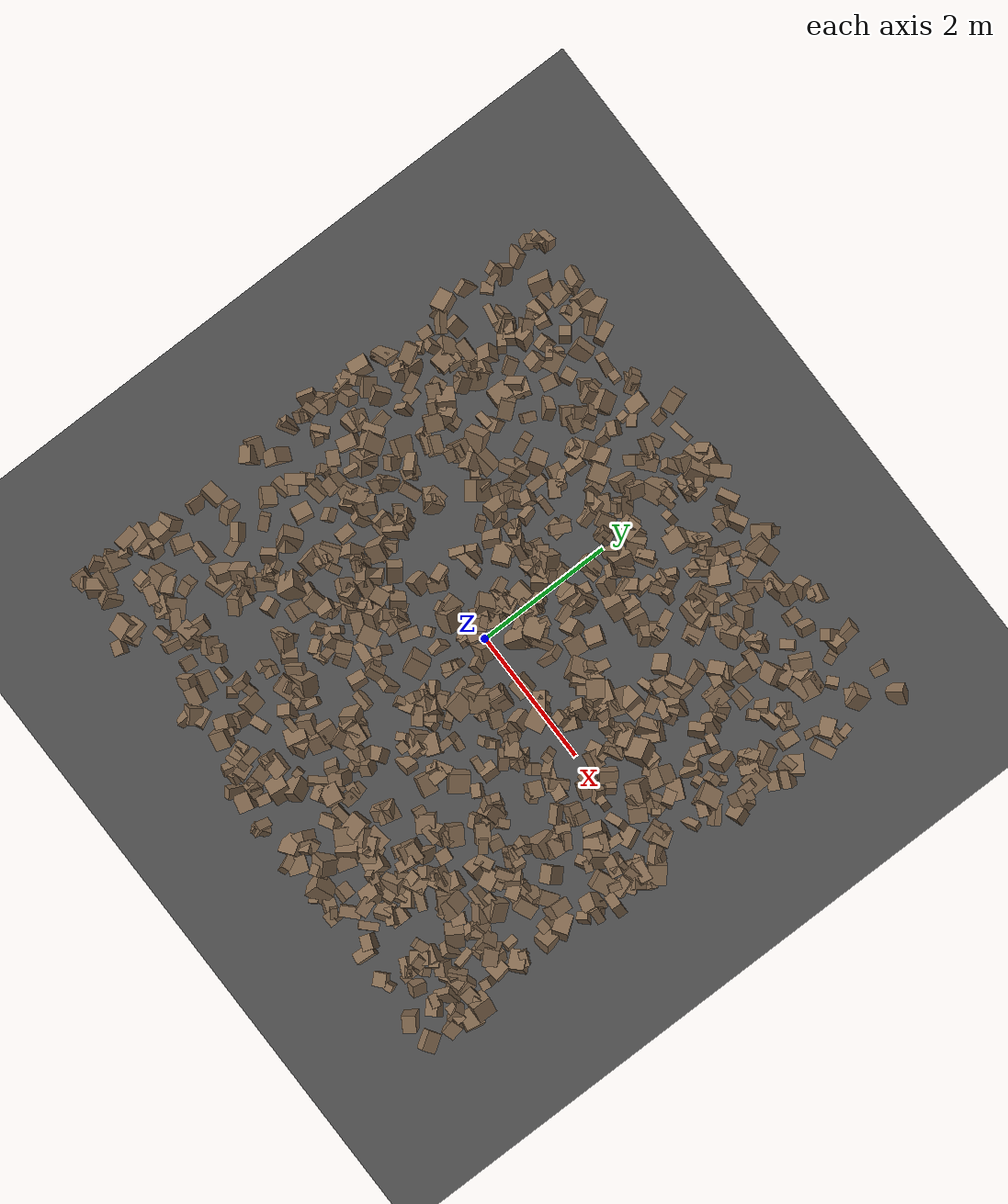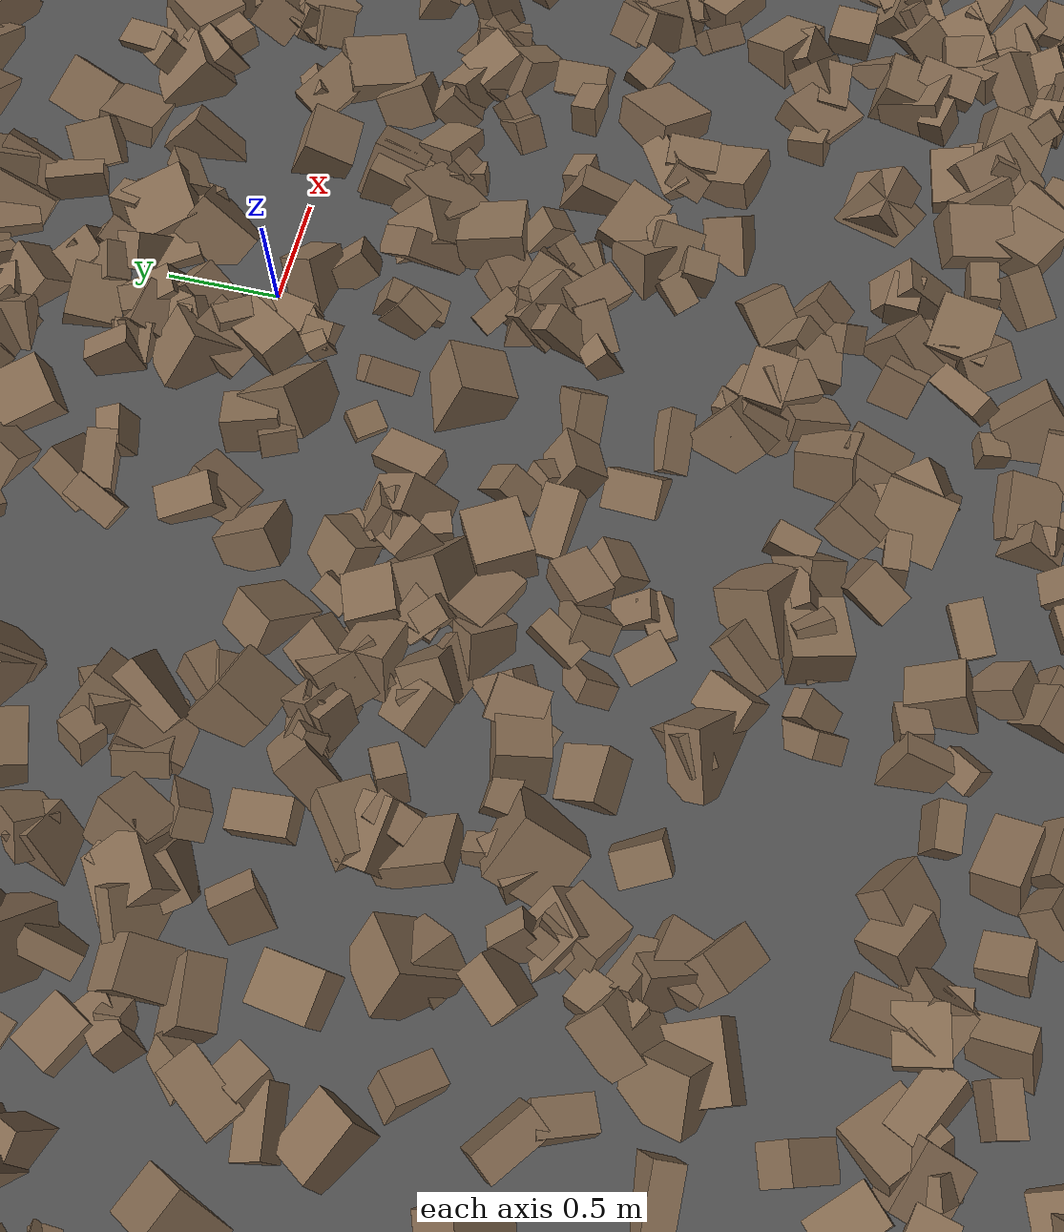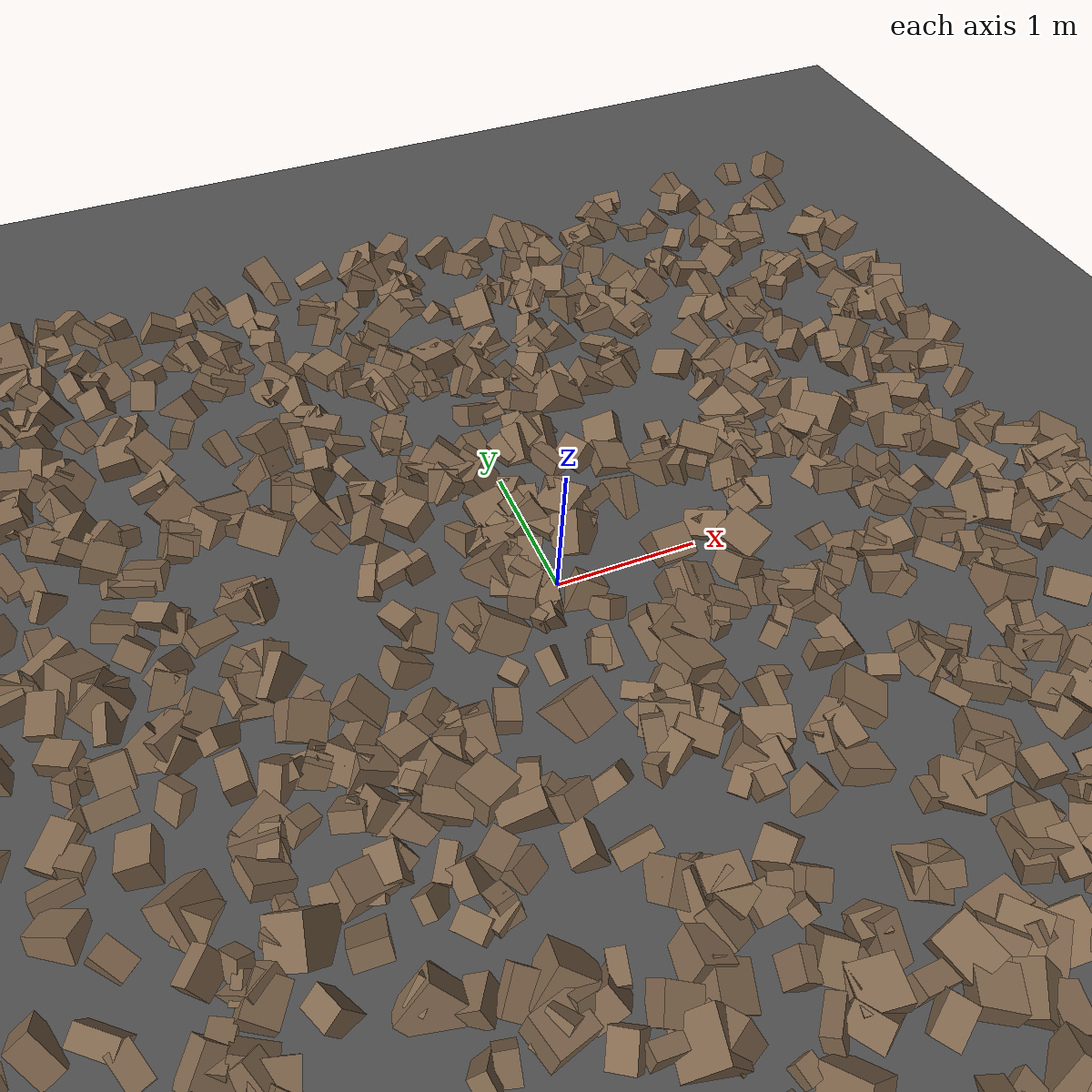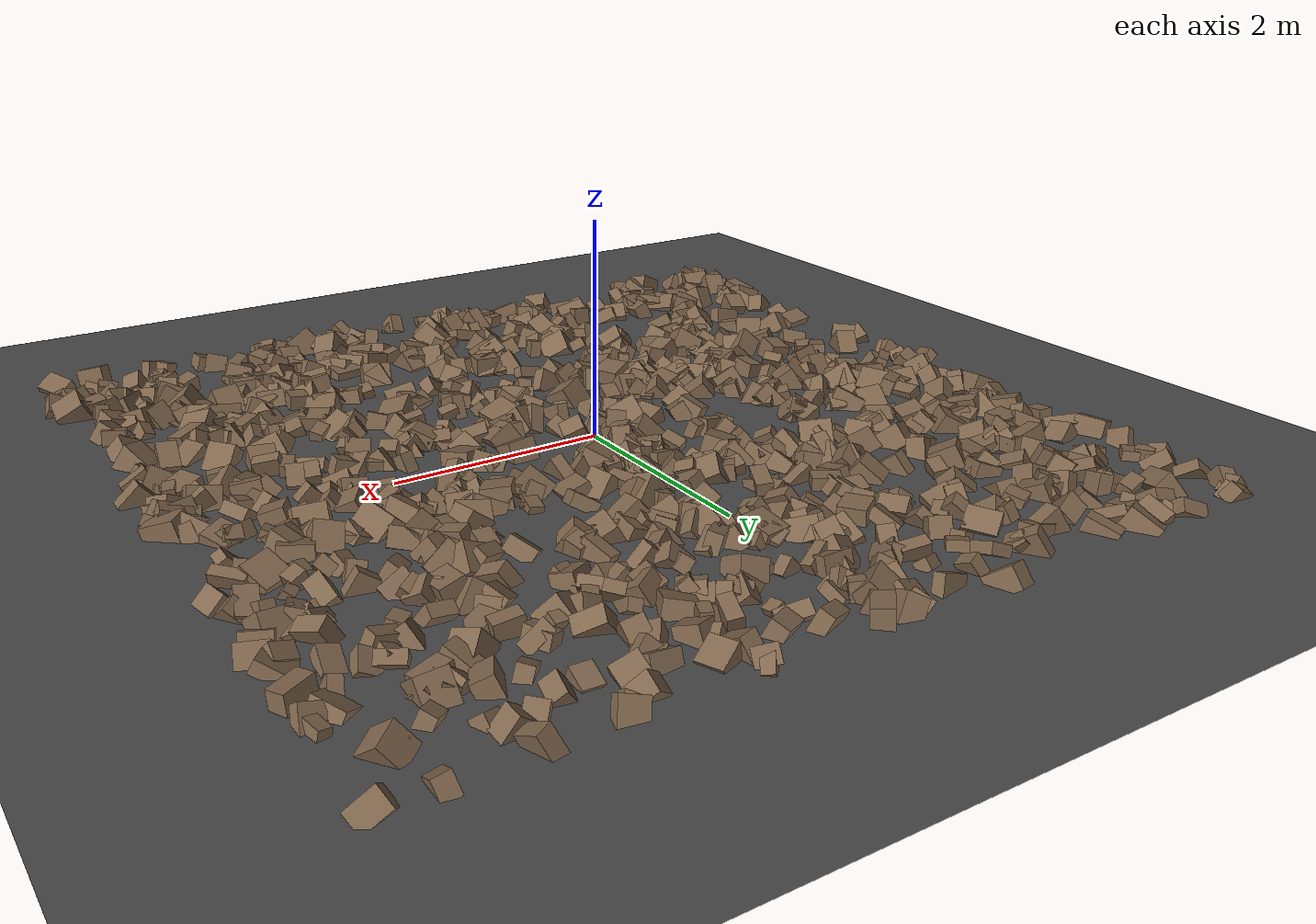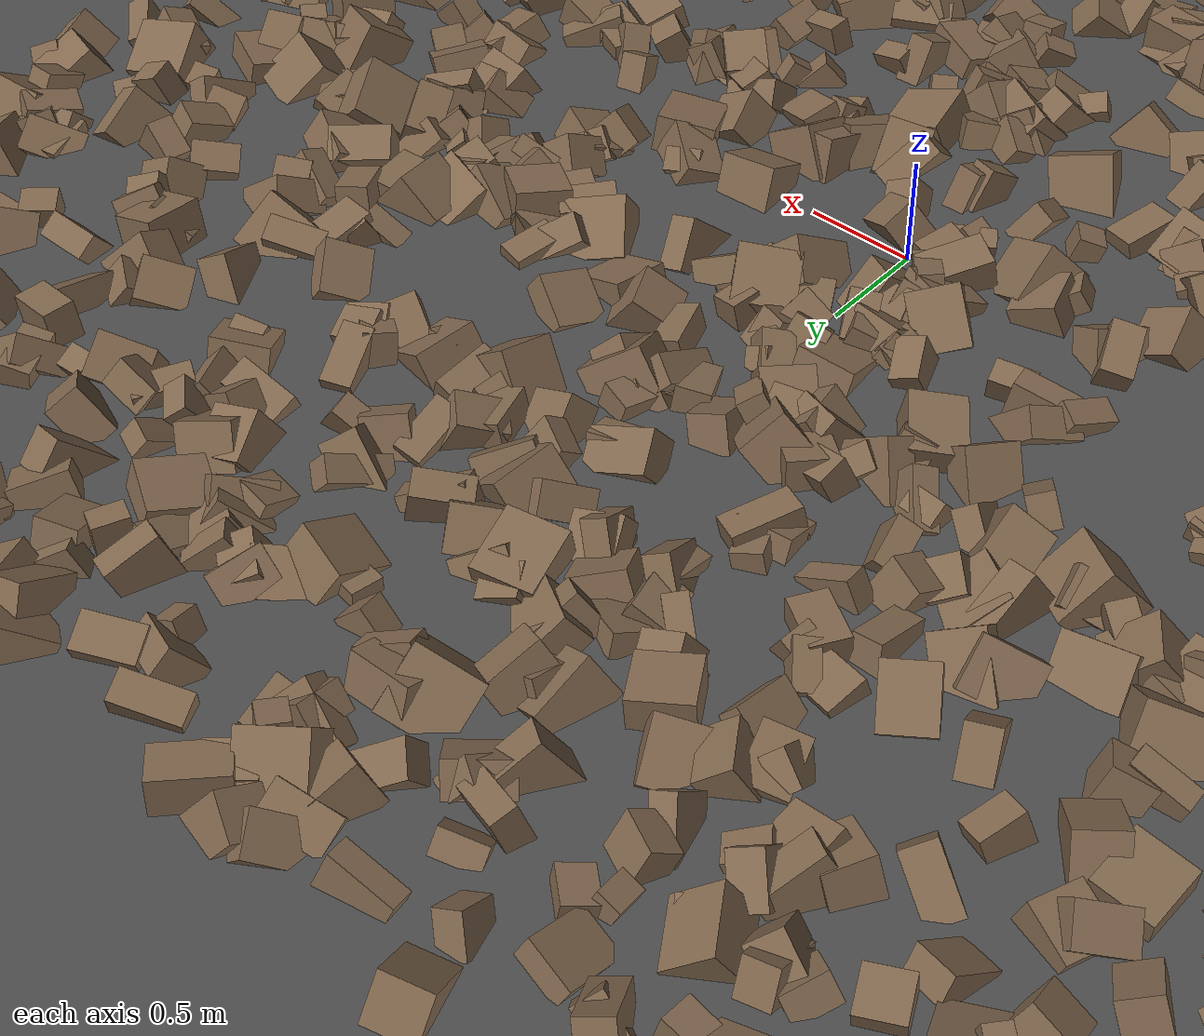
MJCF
<mujoco model="rocky_terrain_scene">
    <compiler angle="radian" inertiafromgeom="true" />
    <option timestep="0.002" gravity="0 0 -9.81" />

    <worldbody>
        <light name="sunlight" pos="5 5 5" dir="-1 -1 -1" diffuse="1 1 1" specular="0.5 0.5 0.5"
            ambient="0.5 0.5 0.5" />

        <geom name="ground_plane" type="plane" size="50 50 0.1" rgba="0.3 0.3 0.3 1" />

        <body name="rocky_terrain_body">

            <geom name="rock1" type="box"
                size="0.10782516895264446 0.08794541485536024 0.09040251031499325"
                pos="-3.1715950524134318 -0.15082933722498115 0.016647268032486964"
                quat="0.1063325338135199 0.09315812434204938 0.41392598033829886 0.3865833615061318"
                rgba="0.5 0.4 0.3 1" />
            <geom name="rock2" type="box"
                size="0.056697253820083005 0.12023993801889242 0.13106277260236296"
                pos="1.326093305974088 -2.9467280412795036 0.006824607586951826"
                quat="0.3810242787169319 0.1772333298994893 0.02363124020678997 0.41811115117678876"
                rgba="0.5 0.4 0.3 1" />
            <geom name="rock3" type="box"
                size="0.13477707496347796 0.08930539124659113 0.12299606541062948"
                pos="-0.2619389307797686 -2.627136037714979 0.0021755332795324535"
                quat="0.1889942536444115 0.37754747617590423 0.2525649296258586 0.18089334055382567"
                rgba="0.5 0.4 0.3 1" />
            <geom name="rock4" type="box"
                size="0.10403831618430642 0.0834823521915138 0.07896314106728672"
                pos="-0.5151410917413779 2.258706511321652 0.019692031012267974"
                quat="0.0914110651915396 0.3526232179609604 0.4493437895028391 0.10662192734466092"
                rgba="0.5 0.4 0.3 1" />
            <geom name="rock5" type="box"
                size="0.06653239030775437 0.12569512670792865 0.14117535758863659"
                pos="-1.009930489172877 0.5435282523715026 0.0045818517403209925"
                quat="0.2273559338047159 0.18300065220119877 0.5463679739344954 0.04327544005958996"
                rgba="0.5 0.4 0.3 1" />
            <geom name="rock6" type="box"
                size="0.05149324380658313 0.08451861154714241 0.10943427932099734"
                pos="-1.8683927990908442 0.6220104108508204 0.0034696134485033814"
                quat="0.2930563602478706 0.21287536836140755 0.24053832237081182 0.25352994901991005"
                rgba="0.5 0.4 0.3 1" />
            <geom name="rock7" type="box"
                size="0.051020503286180234 0.06392801275938935 0.0540742849440328"
                pos="3.471687329651048 1.376250309228082 0.005975499927268884"
                quat="0.23173230474778692 0.029410753853369255 0.4551460286133673 0.28371091278547655"
                rgba="0.5 0.4 0.3 1" />
            <geom name="rock8" type="box"
                size="0.07538064074056547 0.13109731268804992 0.07873465768363025"
                pos="-3.8785261643483713 3.7472543020136513 0.014826663271174519"
                quat="0.20601383228808587 0.3490214662981308 0.036051672967216154 0.40891302844656724"
                rgba="0.5 0.4 0.3 1" />
            <geom name="rock9" type="box"
                size="0.05565753208787061 0.08341409398602553 0.08123614934714482"
                pos="-3.051539043810936 2.08313297873337 0.018392665904192602"
                quat="0.26165826042312607 0.30132235309637173 0.36574626609476 0.0712731203857422"
                rgba="0.5 0.4 0.3 1" />
            <geom name="rock10" type="box"
                size="0.13394528430669644 0.06454063008418016 0.140945365175495"
                pos="-0.690889531313192 1.1404867095812081 0.0024071680500908155"
                quat="0.2659521367946232 0.1566385972421113 0.523260150126356 0.054149115836909435"
                rgba="0.5 0.4 0.3 1" />
            <geom name="rock11" type="box"
                size="0.09737604783598797 0.07829089417731049 0.10348096630214715"
                pos="3.183482332358965 -3.1576300746416033 0.003173780154228525"
                quat="0.2367606440299313 0.40395795024073927 0.06324988244183083 0.2960315232874987"
                rgba="0.5 0.4 0.3 1" />
            <geom name="rock12" type="box"
                size="0.13765493037538484 0.14535803168411177 0.12115110217413523"
                pos="-0.9801763729453752 -1.2276143894734632 0.009562128571812703"
                quat="0.41277855742322206 0.3846933202771381 0.13186098171113872 0.07066714058850117"
                rgba="0.5 0.4 0.3 1" />
            <geom name="rock13" type="box"
                size="0.07060417334431603 0.0612166019317765 0.07402018807083292"
                pos="3.038795408875411 3.5558257225848102 0.0024765038255597106"
                quat="0.25614584496436466 0.5565196344180008 0.08519648644895432 0.10213803416868016"
                rgba="0.5 0.4 0.3 1" />
            <geom name="rock14" type="box"
                size="0.08689174971691813 0.058763264099976724 0.1155994008247698"
                pos="3.231425620971211 2.616231991608002 0.006915880491600046"
                quat="0.23019914542391698 0.41867217299354215 0.014387905668054566 0.3367407759144862"
                rgba="0.5 0.4 0.3 1" />
            <geom name="rock15" type="box"
                size="0.08126093228508025 0.08646738625541009 0.13771835002207672"
                pos="-3.743030752905055 0.5086227429694539 0.016534452799084446"
                quat="0.12045830884713951 0.2557889938281994 0.151007674668625 0.4727450226560362"
                rgba="0.5 0.4 0.3 1" />
            <geom name="rock16" type="box"
                size="0.06448527599074785 0.13714636972622923 0.06592434057058662"
                pos="1.9117639393527277 -0.39836772268490606 0.011978814424772737"
                quat="0.18291186858052147 0.4725395966431805 0.18485663448313366 0.15969190029316438"
                rgba="0.5 0.4 0.3 1" />
            <geom name="rock17" type="box"
                size="0.07142660029750744 0.10147283252106779 0.14725145459389527"
                pos="-2.741194672430451 -3.1767301779521677 0.009654956546991634"
                quat="0.3641343780844333 0.2677711562441276 0.2267175522586528 0.14137691341278624"
                rgba="0.5 0.4 0.3 1" />
            <geom name="rock18" type="box"
                size="0.14182097567076632 0.09650528388088106 0.11175449955482913"
                pos="-1.5654695938529537 3.2136787418820845 0.002846419486272309"
                quat="0.1335618185172067 0.22582676072854446 0.43159912194949435 0.20901229880475442"
                rgba="0.5 0.4 0.3 1" />
            <geom name="rock19" type="box"
                size="0.12061945092407315 0.11075096055006117 0.10650403248901363"
                pos="-0.6419326019955625 -0.09119484291234414 0.0032858335116749825"
                quat="0.179989599207917 0.2507144880348941 0.34679867566866324 0.22249723708852573"
                rgba="0.5 0.4 0.3 1" />
            <geom name="rock20" type="box"
                size="0.12550028452001544 0.14466280386185792 0.0956680799603246"
                pos="3.078170762205188 -1.2179086301361206 0.011574865367653533"
                quat="0.21151348131125713 0.07925429861963729 0.22527593116746117 0.4839562889016445"
                rgba="0.5 0.4 0.3 1" />
            <geom name="rock21" type="box"
                size="0.07398562446634557 0.13991796998582 0.13218305384032697"
                pos="1.8898673718043648 -3.026574298599095 0.01875066525235517"
                quat="0.3872268237539914 0.010246485588826043 0.31654655889232636 0.2859801317648562"
                rgba="0.5 0.4 0.3 1" />
            <geom name="rock22" type="box"
                size="0.12925159149193274 0.07670295990219868 0.09834536566575341"
                pos="2.1587985051548086 -2.963885674072495 0.001600077522010761"
                quat="0.1165623763259977 0.19933312129297212 0.6261784208277502 0.05792608155327987"
                rgba="0.5 0.4 0.3 1" />
            <geom name="rock23" type="box"
                size="0.09284850033024208 0.11299024185605096 0.07099933831483973"
                pos="-3.755848858835072 1.8727419326107837 0.016202975905633316"
                quat="0.24131223974953178 0.2847478234440972 0.22282043926328224 0.25111949754308877"
                rgba="0.5 0.4 0.3 1" />
            <geom name="rock24" type="box"
                size="0.07963583762627734 0.11408389099030845 0.06512034350718796"
                pos="0.09915278736431965 0.7372951795808378 0.017598543027900874"
                quat="0.419647276837295 0.1517912338661195 0.3667235337388412 0.061837955557744226"
                rgba="0.5 0.4 0.3 1" />
            <geom name="rock25" type="box"
                size="0.06333141943809609 0.09722384806136067 0.14095079398202487"
                pos="1.0474927527712952 -1.5474348969493583 0.01085764571644244"
                quat="0.2753952659036558 0.08666647401837475 0.3565857321814966 0.2813525278964728"
                rgba="0.5 0.4 0.3 1" />
            <geom name="rock26" type="box"
                size="0.13943973119590172 0.10212452313606285 0.05036271655302188"
                pos="0.6136472118013216 3.0131134972595612 0.014151476314775115"
                quat="0.17621782465289595 0.5555363964754648 0.1862120373287815 0.08203374154285774"
                rgba="0.5 0.4 0.3 1" />
            <geom name="rock27" type="box"
                size="0.12421677828019162 0.13553753111311667 0.0822605831394191"
                pos="-0.08691398102334968 0.28302892011405145 0.01196913473932293"
                quat="0.3959878926286183 0.21165890344556507 0.3456264217785593 0.04672678214725732"
                rgba="0.5 0.4 0.3 1" />
            <geom name="rock28" type="box"
                size="0.06069158242085389 0.10708342472630891 0.10217409427598348"
                pos="-3.019592317116266 2.5932763464389774 0.013688624254361294"
                quat="0.3966399465796524 0.2514973420102541 0.143825523760304 0.2080371876497895"
                rgba="0.5 0.4 0.3 1" />
            <geom name="rock29" type="box"
                size="0.09481590953938276 0.12214903503747068 0.09216049518881712"
                pos="1.9960524329109983 -2.226594696713491 0.00046162400370857836"
                quat="0.27655713967625245 0.24834710797805892 0.23307959091299413 0.24201616143269455"
                rgba="0.5 0.4 0.3 1" />
            <geom name="rock30" type="box"
                size="0.055721446391815116 0.10373829591603348 0.05477889587615206"
                pos="-0.17230523747612558 0.5982420295687723 0.01623127082449079"
                quat="0.21741713605081125 0.1655329923042536 0.2424487796010878 0.37460109204384734"
                rgba="0.5 0.4 0.3 1" />
            <geom name="rock31" type="box"
                size="0.14683411928301177 0.07168186892533698 0.13918803272613436"
                pos="-3.4009108278261664 2.0002219993661186 0.005467966122277048"
                quat="0.45634800128400044 0.21009626743242404 0.2319585764835386 0.10159715480003693"
                rgba="0.5 0.4 0.3 1" />
            <geom name="rock32" type="box"
                size="0.06443596734750681 0.06747677443826097 0.056791108229376525"
                pos="-2.460082569635654 3.130876389413282 0.008272873488299158"
                quat="0.4353246725175003 0.13850613306026158 0.19229319490700347 0.23387599951523466"
                rgba="0.5 0.4 0.3 1" />
            <geom name="rock33" type="box"
                size="0.05402924292607432 0.07843900523644727 0.13316498952419237"
                pos="3.8232885762224074 -1.2409818667112846 0.0021816002097788446"
                quat="0.19397248116041096 0.19264536906338633 0.5640390311567396 0.04934311861946323"
                rgba="0.5 0.4 0.3 1" />
            <geom name="rock34" type="box"
                size="0.11066375910625825 0.07994107205368847 0.1441779794284076"
                pos="-3.2525508553454054 2.1737063880317162 0.01040900902384602"
                quat="0.3991648536266422 0.04699426781668554 0.5102196225936734 0.0436212559629988"
                rgba="0.5 0.4 0.3 1" />
            <geom name="rock35" type="box"
                size="0.08050896229787893 0.059680298325592886 0.09268694380268003"
                pos="0.713248090128527 1.797644178245366 0.019688736436362153"
                quat="0.1686472068483691 0.4146223743670368 0.35503416180051417 0.06169625698407998"
                rgba="0.5 0.4 0.3 1" />
            <geom name="rock36" type="box"
                size="0.14697075499103524 0.09067741742733812 0.1030115729447241"
                pos="2.829687261029405 3.188810761776659 0.011637966171177327"
                quat="0.5134993149984967 0.13191239492557597 0.038457440227662724 0.3161308498482646"
                rgba="0.5 0.4 0.3 1" />
            <geom name="rock37" type="box"
                size="0.07189816021027932 0.14613506263329212 0.1307674560357875"
                pos="3.510035685032748 2.057257652496652 0.006829262073325781"
                quat="0.3546225914978802 0.40407078058669993 0.2241482476275319 0.01715838028788798"
                rgba="0.5 0.4 0.3 1" />
            <geom name="rock38" type="box"
                size="0.11482234928079045 0.0589535608479862 0.07356759077991508"
                pos="2.206225591023916 0.2986343145651986 0.016197969150439747"
                quat="0.3180803849638472 0.12865191151605684 0.3174035839860157 0.23586411953408024"
                rgba="0.5 0.4 0.3 1" />
            <geom name="rock39" type="box"
                size="0.12312992613581114 0.078260060051251 0.059484169055532554"
                pos="-3.874796332204208 0.562667846904529 0.009108190181743688"
                quat="0.12383669752920648 0.33447304001187006 0.37011029466430706 0.17157996779461637"
                rgba="0.5 0.4 0.3 1" />
            <geom name="rock40" type="box"
                size="0.12120142313250946 0.12549219042578316 0.08304085767497577"
                pos="-1.0423138058806973 -0.8918038375751323 0.013954154455320326"
                quat="0.4369025402024108 0.22525469868294823 0.24717768253395753 0.09066507858068341"
                rgba="0.5 0.4 0.3 1" />
            <geom name="rock41" type="box"
                size="0.11645195852557812 0.12966103328776374 0.09024833048787931"
                pos="-0.1807204455939564 1.0689418699634752 0.019597102897097787"
                quat="0.17231935760978634 0.5103790301906401 0.2243501384426531 0.09295147375692055"
                rgba="0.5 0.4 0.3 1" />
            <geom name="rock42" type="box"
                size="0.07314439306332683 0.13638177571571825 0.06812525812876274"
                pos="0.2529960056464269 -2.206365450479681 0.005553889588403232"
                quat="0.07126229899077427 0.053997811005080464 0.27011116619134096 0.6046287238128043"
                rgba="0.5 0.4 0.3 1" />
            <geom name="rock43" type="box"
                size="0.13102542783638849 0.13252791215856297 0.05778732488955997"
                pos="0.8028703929644081 -1.2440969730049325 0.019302505120385536"
                quat="0.18884772502542038 0.3019933386607493 0.19180894287528932 0.3173499934385411"
                rgba="0.5 0.4 0.3 1" />
            <geom name="rock44" type="box"
                size="0.12351061440294629 0.07150542013892044 0.08909209314907884"
                pos="-1.7612499836415942 -0.37840992712364585 0.0006083501213765641"
                quat="0.09918587400760544 0.32844748379302874 0.2568088917264363 0.3155577504729296"
                rgba="0.5 0.4 0.3 1" />
            <geom name="rock45" type="box"
                size="0.06295277044230149 0.05258681935133859 0.059359889345705255"
                pos="0.04141844978409992 0.9170234575028111 0.007485242856465853"
                quat="0.10680088550449376 0.41353970364166037 0.2151336133168579 0.2645257975369879"
                rgba="0.5 0.4 0.3 1" />
            <geom name="rock46" type="box"
                size="0.06117952556881615 0.09784917319990577 0.10355112957107647"
                pos="-2.9134392935963698 2.121502766849358 0.013889646442463696"
                quat="0.06641654771384443 0.198316000080712 0.13452672455711628 0.6007407276483273"
                rgba="0.5 0.4 0.3 1" />
            <geom name="rock47" type="box"
                size="0.14569035120580365 0.11319547234140252 0.08359187516672607"
                pos="0.5831635246999491 -2.6911730873234117 0.013782362231623158"
                quat="0.11781491077047637 0.35124894877745233 0.19207047566467855 0.33886566478739266"
                rgba="0.5 0.4 0.3 1" />
            <geom name="rock48" type="box"
                size="0.14999340766201855 0.14159317099822488 0.13833599413861075"
                pos="0.3165917859281482 0.5930420451878886 0.006365906963839468"
                quat="0.23698096124226012 0.11630504231046263 0.329571952301 0.31714204414627717"
                rgba="0.5 0.4 0.3 1" />
            <geom name="rock49" type="box"
                size="0.14936779149330037 0.0894719488332439 0.1144453240578477"
                pos="-3.854149324594223 -3.3312643505190067 0.003911433830161922"
                quat="0.3780304694868926 0.178742102091088 0.31850548763293546 0.12472194078908394"
                rgba="0.5 0.4 0.3 1" />
            <geom name="rock50" type="box"
                size="0.09287534183719359 0.13549086049520123 0.06589348513530127"
                pos="0.09073193809132718 3.39435578111749 0.011245422255928336"
                quat="0.3766833919919113 0.14252575770477394 0.12049898993809338 0.36029186036522143"
                rgba="0.5 0.4 0.3 1" />
            <geom name="rock51" type="box"
                size="0.09256406297968778 0.13680562104593658 0.05083429173316709"
                pos="0.0879199376518196 -2.6808821246750316 0.01518810053890131"
                quat="0.2050496528679091 0.3670588604878238 0.2575957996637751 0.1702956869804919"
                rgba="0.5 0.4 0.3 1" />
            <geom name="rock52" type="box"
                size="0.0922592090963658 0.07466797412004726 0.07080058964959343"
                pos="-0.08883639451755343 -3.6800953810511334 0.01590720012280398"
                quat="0.27798121065280124 0.28414104517893396 0.2095205008004755 0.22835724336778931"
                rgba="0.5 0.4 0.3 1" />
            <geom name="rock53" type="box"
                size="0.11627182527744508 0.05012893267806221 0.07539722498543641"
                pos="-3.2037022128262826 1.2061947921038252 0.014330805799554456"
                quat="0.1819129278476695 0.2648671076779678 0.2750018526315616 0.27821811184280115"
                rgba="0.5 0.4 0.3 1" />
            <geom name="rock54" type="box"
                size="0.13284382107316384 0.07132481714389086 0.14393505642190452"
                pos="3.498690228279491 0.23858313159241984 0.002403573769894285"
                quat="0.29925632680159964 0.530498519946872 0.09914538640990388 0.07109976684162447"
                rgba="0.5 0.4 0.3 1" />
            <geom name="rock55" type="box"
                size="0.07437263250789125 0.0728825168544896 0.08366273041086217"
                pos="3.4607757862484574 1.7619744555850572 0.006031693745225697"
                quat="0.631864715265782 0.26492848943160985 0.06517489305658546 0.03803190224602266"
                rgba="0.5 0.4 0.3 1" />
            <geom name="rock56" type="box"
                size="0.08334573561862728 0.08124133170460514 0.05433556532992037"
                pos="1.305005107467875 -2.1280719277025755 0.008260819061905152"
                quat="0.08207652109450628 0.5047685891279979 0.014360517946319352 0.39879437183117644"
                rgba="0.5 0.4 0.3 1" />
            <geom name="rock57" type="box"
                size="0.1120554994595182 0.09234718674220743 0.0861176275345857"
                pos="-1.073919955004297 -1.5735109399197675 0.015130554715461167"
                quat="0.335606817315098 0.3886145573684631 0.17210069233602296 0.10367793298041592"
                rgba="0.5 0.4 0.3 1" />
            <geom name="rock58" type="box"
                size="0.1464452256417743 0.051173013005203265 0.10579625241278295"
                pos="3.6720929643352713 -0.2693721619913134 0.011007862013763081"
                quat="0.2820087484641818 0.29794691701853376 0.20702333318173247 0.21302100133555196"
                rgba="0.5 0.4 0.3 1" />
            <geom name="rock59" type="box"
                size="0.10700664297242717 0.14720847409513382 0.1441838530965847"
                pos="-1.790633322022229 -1.496766362977664 0.01949070786261442"
                quat="0.3702891612887947 0.09893240142503291 0.062295776112383607 0.4684826611737888"
                rgba="0.5 0.4 0.3 1" />
            <geom name="rock60" type="box"
                size="0.07762958874629405 0.09240096856590879 0.10391972514444511"
                pos="0.7604551910080026 3.072714181148915 0.008015510554429884"
                quat="0.417804878828854 0.2628484021773622 0.20367327291517484 0.11567344607860901"
                rgba="0.5 0.4 0.3 1" />
            <geom name="rock61" type="box"
                size="0.14159670560742127 0.11877083660907861 0.09043873458242734"
                pos="3.4878729964275577 -1.4431297299733492 0.017408060645226948"
                quat="0.34414418824817145 0.193051300808112 0.30220880623463114 0.16059570470908544"
                rgba="0.5 0.4 0.3 1" />
            <geom name="rock62" type="box"
                size="0.10826461012385621 0.08366868518853329 0.14916166988310892"
                pos="-3.9304446621312827 -0.9033893130903445 0.0016808706604625567"
                quat="0.26754583582134533 0.31161403828131795 0.3066083865334756 0.11423173936386107"
                rgba="0.5 0.4 0.3 1" />
            <geom name="rock63" type="box"
                size="0.1042047166230198 0.1315224878935679 0.07852210441857145"
                pos="-3.020879886726533 3.00258856188532 0.0134099230790869"
                quat="0.059112259786543976 0.2109657039674604 0.3917638827687979 0.3381581534771978"
                rgba="0.5 0.4 0.3 1" />
            <geom name="rock64" type="box"
                size="0.05697990029088912 0.10350705551119174 0.10535695657550903"
                pos="3.7430446297343805 -2.198084892110459 0.018751394924623903"
                quat="0.2875208988376756 0.30607531265894533 0.182282195464827 0.22412159303855209"
                rgba="0.5 0.4 0.3 1" />
            <geom name="rock65" type="box"
                size="0.11901632446425897 0.07055024746706585 0.09816889408185961"
                pos="-0.5945602155316427 1.671714225331419 0.007121653013665161"
                quat="0.39365961083278844 0.5489772066392224 0.025338188499312908 0.032024994028676174"
                rgba="0.5 0.4 0.3 1" />
            <geom name="rock66" type="box"
                size="0.09630372822418146 0.08535092959148097 0.08286372800605564"
                pos="2.267766074039935 -1.568763915378331 0.000618564862517359"
                quat="0.24722258339427033 0.30409285175693324 0.2905750808212304 0.15810948402756597"
                rgba="0.5 0.4 0.3 1" />
            <geom name="rock67" type="box"
                size="0.07143889837392894 0.09944840771052754 0.12778077615714198"
                pos="0.5877243835947219 1.9059027807654125 0.008731714958684484"
                quat="0.42351829824983683 0.4296656468943097 0.1223976248923396 0.02441842996351387"
                rgba="0.5 0.4 0.3 1" />
            <geom name="rock68" type="box"
                size="0.12911695364927978 0.07017291214515146 0.09397068293279062"
                pos="1.3751102489366946 1.7953656049244664 0.0014027474205438506"
                quat="0.036462034103287154 0.38981103558993224 0.21881327064659017 0.3549136596601904"
                rgba="0.5 0.4 0.3 1" />
            <geom name="rock69" type="box"
                size="0.13925375492532083 0.1284004958060726 0.1314551859224256"
                pos="-2.8894086773060783 0.14952237642020805 0.011947181843979335"
                quat="0.2560499474364275 0.3608896371822793 0.3705901684394842 0.01247024694180887"
                rgba="0.5 0.4 0.3 1" />
            <geom name="rock70" type="box"
                size="0.08518683575418111 0.05684048215631751 0.13797985946324942"
                pos="3.4258657406941646 1.8673550075360552 0.002488857840739378"
                quat="0.32605238267077713 0.039941766925557606 0.303729641849581 0.33027620855408435"
                rgba="0.5 0.4 0.3 1" />
            <geom name="rock71" type="box"
                size="0.05324328774434503 0.14051602777850242 0.05837086859939954"
                pos="1.536385623796475 2.830847318300342 0.0074052778856327816"
                quat="0.46578138699193533 0.15402389130250968 0.3020166537859756 0.07817806791957946"
                rgba="0.5 0.4 0.3 1" />
            <geom name="rock72" type="box"
                size="0.07536352945303687 0.07248359891925393 0.08959986840428678"
                pos="-0.03484988054031657 2.5186671829369063 0.0022438436656060934"
                quat="0.21477842452609183 0.1696496115756217 0.39795350646866806 0.21761845742961847"
                rgba="0.5 0.4 0.3 1" />
            <geom name="rock73" type="box"
                size="0.1288439861298899 0.06854582754622353 0.08969733563742782"
                pos="3.3914071277757936 -3.104090660682302 0.00027066680279658195"
                quat="0.4757365459665139 0.056666367941444584 0.2054031525871905 0.26219393350485104"
                rgba="0.5 0.4 0.3 1" />
            <geom name="rock74" type="box"
                size="0.07521872173733092 0.14625521387749008 0.13455394955634076"
                pos="-2.962384148751644 -0.5562245272481796 0.006666202880568286"
                quat="0.1405883230763932 0.3206245207632488 0.2231224385712243 0.3156647175891337"
                rgba="0.5 0.4 0.3 1" />
            <geom name="rock75" type="box"
                size="0.10669438641521453 0.10388791565665192 0.09680856130989324"
                pos="3.4625763749251464 -3.1453664690549292 0.019370594374362206"
                quat="0.33683598509830415 0.10315508407762286 0.3138030625921214 0.24620586823195173"
                rgba="0.5 0.4 0.3 1" />
            <geom name="rock76" type="box"
                size="0.07640230355055806 0.05260922883969831 0.13620077556808896"
                pos="-0.6422632063976916 -0.181394164794896 0.006638838552771751"
                quat="0.12031577182886535 0.25717335749794296 0.39560710907588087 0.22690376159731085"
                rgba="0.5 0.4 0.3 1" />
            <geom name="rock77" type="box"
                size="0.08972293473817608 0.08548103740799048 0.09052433721323556"
                pos="-2.1276167664445067 3.041986208361682 0.013463766333162744"
                quat="0.45364239934941575 0.3615719367231417 0.09211486639394742 0.09267079753349507"
                rgba="0.5 0.4 0.3 1" />
            <geom name="rock78" type="box"
                size="0.09499371423294281 0.050429901627962195 0.1044998612676509"
                pos="-1.5150779992231538 -1.1671854595595121 0.009604696101399393"
                quat="0.22426878152840984 0.3767600383172684 0.12284580887735637 0.27612537127696535"
                rgba="0.5 0.4 0.3 1" />
            <geom name="rock79" type="box"
                size="0.08794355393856018 0.07497416411639261 0.0551663428937571"
                pos="3.698010871296799 2.7320942248878293 0.010454932610929947"
                quat="0.17538745172113382 0.34515986571308865 0.06486919705657836 0.41458348550919927"
                rgba="0.5 0.4 0.3 1" />
            <geom name="rock80" type="box"
                size="0.14487881437425792 0.07946207679530533 0.09014574822098584"
                pos="2.3987666238552103 -3.872878289421248 0.007461102123711347"
                quat="0.051823517299259526 0.4380385212413836 0.4095005306823977 0.10063743077695919"
                rgba="0.5 0.4 0.3 1" />
            <geom name="rock81" type="box"
                size="0.14988547452591133 0.11390858067883432 0.08455199636307502"
                pos="-3.9983156844654033 -3.017574137368114 0.011100360867014263"
                quat="0.2527081547516088 0.19598663312319362 0.29923521615188664 0.25206999597331087"
                rgba="0.5 0.4 0.3 1" />
            <geom name="rock82" type="box"
                size="0.09703786509297005 0.08366699066116806 0.11728603582702621"
                pos="3.90232394249246 -3.536319646648624 0.014377351282853683"
                quat="0.38500977007389836 0.5116827907108635 0.10087179782153864 0.002435641393699409"
                rgba="0.5 0.4 0.3 1" />
            <geom name="rock83" type="box"
                size="0.13939493651950208 0.1339957520713912 0.05679629167182009"
                pos="3.961146691613174 -3.266472746980514 0.019048373163680816"
                quat="0.15453247052728977 0.4665737325118605 0.37704300931913753 0.0018507876417122638"
                rgba="0.5 0.4 0.3 1" />
            <geom name="rock84" type="box"
                size="0.12051928761848593 0.12622491297518096 0.10703747539161204"
                pos="-0.3162637890160154 -2.4597171105477553 0.014400441613537224"
                quat="0.22690846588931957 0.30070783256895045 0.32270366424901137 0.14968003729271867"
                rgba="0.5 0.4 0.3 1" />
            <geom name="rock85" type="box"
                size="0.12620395976858084 0.06412582502247272 0.07259008104040754"
                pos="-3.5267058401571063 -0.1581230807609808 0.004140479686935379"
                quat="0.1491938455662082 0.3325447293134941 0.03332220306301559 0.4849392220572822"
                rgba="0.5 0.4 0.3 1" />
            <geom name="rock86" type="box"
                size="0.09969596399562156 0.12630760371562316 0.12416203272562497"
                pos="1.994150245263195 2.656310717938224 0.012468448464335976"
                quat="0.3462978136653392 0.03475292991114506 0.30942049046945336 0.3095287659540624"
                rgba="0.5 0.4 0.3 1" />
            <geom name="rock87" type="box"
                size="0.054521802444867866 0.050945996018338525 0.1017779766142991"
                pos="1.8210674173250112 1.339075296472802 0.011758622142180248"
                quat="0.312186575113794 0.13031029371259564 0.21447795069634548 0.34302518047726493"
                rgba="0.5 0.4 0.3 1" />
            <geom name="rock88" type="box"
                size="0.14285131860570505 0.053319228736755424 0.09433733950513182"
                pos="-1.752278719035048 -3.0784801501499466 0.004976000197806128"
                quat="0.4714104434469651 0.04124542766378171 0.4318120444039778 0.05553208448527546"
                rgba="0.5 0.4 0.3 1" />
            <geom name="rock89" type="box"
                size="0.06346253379022236 0.11322594458126098 0.12571567695322522"
                pos="2.9744275117916095 -3.1313262484215425 0.0009987349768847277"
                quat="0.28257447707891925 0.25583123289223525 0.11705837008427208 0.3445359199445735"
                rgba="0.5 0.4 0.3 1" />
            <geom name="rock90" type="box"
                size="0.08885780021769686 0.1272584231408183 0.05228070559712418"
                pos="2.09408877630396 -2.5056927995780223 0.016605065306194582"
                quat="0.3709015382435867 0.26264683847763676 0.33983218660929443 0.026619436669482185"
                rgba="0.5 0.4 0.3 1" />
            <geom name="rock91" type="box"
                size="0.05353614170694068 0.1178678921199831 0.07715190361039095"
                pos="-0.9720558147930776 1.1830665568598304 0.004910197591443462"
                quat="0.3527431712917262 0.16705129789365292 0.32644806375331403 0.15375746706130683"
                rgba="0.5 0.4 0.3 1" />
            <geom name="rock92" type="box"
                size="0.11026418515510719 0.14012139840897123 0.08161288888284708"
                pos="1.5660414148653414 -0.6022767925964505 0.006030720961185803"
                quat="0.17677806941179097 0.45527526600670964 0.16536445181032208 0.20258221277117722"
                rgba="0.5 0.4 0.3 1" />
            <geom name="rock93" type="box"
                size="0.0782876800773701 0.13767241649902828 0.0832144453051539"
                pos="2.8043532237114697 3.7267761717595 0.016641251601972055"
                quat="0.28751356807326994 0.3849775844747676 0.013935232463421553 0.3135736149885408"
                rgba="0.5 0.4 0.3 1" />
            <geom name="rock94" type="box"
                size="0.12347063854433311 0.07824178517167421 0.05604783937218965"
                pos="2.9727293615126804 -3.551425701691379 0.006185360075815834"
                quat="0.17311201336220397 0.30833180504156016 0.22874510471373793 0.2898110768824981"
                rgba="0.5 0.4 0.3 1" />
            <geom name="rock95" type="box"
                size="0.1260394064946211 0.10035452501938993 0.12670807580096694"
                pos="-2.7020808251259014 -2.0800073242810733 0.010032467347295909"
                quat="0.17366955788912408 0.46876720161841007 0.18820564212751753 0.16935759836494832"
                rgba="0.5 0.4 0.3 1" />
            <geom name="rock96" type="box"
                size="0.06245008203976493 0.13415001853415476 0.13128405375823732"
                pos="-3.1591454746864915 -1.7604820234777563 0.010051687470689416"
                quat="0.3041146921607575 0.3695210328321591 0.10001486175945877 0.22634941324762461"
                rgba="0.5 0.4 0.3 1" />
            <geom name="rock97" type="box"
                size="0.07786694002256837 0.05736675956956688 0.05765774630070043"
                pos="-1.4976419741543765 -3.1475254703165287 0.017266948723969715"
                quat="0.45464244514149926 0.19197152528379868 0.16209386840750983 0.19129216116719217"
                rgba="0.5 0.4 0.3 1" />
            <geom name="rock98" type="box"
                size="0.14847905792849303 0.1482237128106339 0.08946987559626345"
                pos="0.11999742060833807 3.8883320906490377 0.0013337230052859095"
                quat="0.33121782967772945 0.36523653070922263 0.15482090693060396 0.14872473268244404"
                rgba="0.5 0.4 0.3 1" />
            <geom name="rock99" type="box"
                size="0.11448348626522284 0.06891770061242682 0.09400821907417022"
                pos="-1.1355111558101516 -3.256691502961095 0.007577267900482701"
                quat="0.31249757844355036 0.25245308994599786 0.37086862844814966 0.06418070316230201"
                rgba="0.5 0.4 0.3 1" />
            <geom name="rock100" type="box"
                size="0.06969811184904535 0.05134588400703099 0.06501137695531534"
                pos="0.3792252893899368 2.8791073750934366 0.015078089124923626"
                quat="0.26909512439745414 0.26698028470989227 0.22283071102428662 0.24109387986836703"
                rgba="0.5 0.4 0.3 1" />
            <geom name="rock101" type="box"
                size="0.08898033928800042 0.14600782621622355 0.05179792023566581"
                pos="-2.4958551429538325 3.0013763900810186 0.015266532431025373"
                quat="0.1929967074028551 0.07049742257052122 0.3785680330519487 0.357937836974675"
                rgba="0.5 0.4 0.3 1" />
            <geom name="rock102" type="box"
                size="0.08084466868555404 0.1439894728129157 0.09275969005734047"
                pos="-3.8434596834914014 -2.4163041138100887 0.004439652557850437"
                quat="0.03176376249362572 0.2864064582910192 0.48155776797448074 0.20027201124087438"
                rgba="0.5 0.4 0.3 1" />
            <geom name="rock103" type="box"
                size="0.11091794693420509 0.11886170159291294 0.06450711377212495"
                pos="-2.6454196451489818 -1.632343555410336 0.01044421066919037"
                quat="0.45023055077212687 0.24835498080412066 0.08771785896106717 0.2136966094626853"
                rgba="0.5 0.4 0.3 1" />
            <geom name="rock104" type="box"
                size="0.0940914528529853 0.14626441758315478 0.1341559815775767"
                pos="3.0081410180694235 -0.4070288758571001 0.00505999955279715"
                quat="0.26421746153152237 0.12003808735381266 0.5428258951473219 0.072918555967343"
                rgba="0.5 0.4 0.3 1" />
            <geom name="rock105" type="box"
                size="0.10535262586395554 0.13856839602164697 0.14988963404531497"
                pos="0.36724550969749004 1.3719520635874787 0.009591489432054236"
                quat="0.07320491410175545 0.3136954595853705 0.36071920183637335 0.2523804244765008"
                rgba="0.5 0.4 0.3 1" />
            <geom name="rock106" type="box"
                size="0.12691788224340506 0.07630921886091134 0.09497915611458899"
                pos="2.0003661128501227 1.0379803719155438 0.00123636573996192"
                quat="0.24171979974209248 0.2255320175345402 0.25851641128835917 0.27423177143500815"
                rgba="0.5 0.4 0.3 1" />
            <geom name="rock107" type="box"
                size="0.08879078841138345 0.1054569951768681 0.050063453466664604"
                pos="-0.8244589622575873 -3.56913938301036 0.005517443772733417"
                quat="0.40885875801150184 0.00637282573636814 0.41705394812920366 0.1677144681229263"
                rgba="0.5 0.4 0.3 1" />
            <geom name="rock108" type="box"
                size="0.12262354418214567 0.08091070402483756 0.11222917121377322"
                pos="-0.5707305837132282 -1.4260753700188484 0.014571758102843349"
                quat="0.29915510616518365 0.0618072995420613 0.4606402780358584 0.17839731625689667"
                rgba="0.5 0.4 0.3 1" />
            <geom name="rock109" type="box"
                size="0.09472258512703408 0.07658525912421973 0.05952614818779737"
                pos="-1.2770481707492731 0.893828145660251 0.014206737775573188"
                quat="0.045592016431195564 0.28100903788861065 0.33925112217038256 0.3341478235098112"
                rgba="0.5 0.4 0.3 1" />
            <geom name="rock110" type="box"
                size="0.07746182963902366 0.09729129362705606 0.06322955637913483"
                pos="-1.1277388217672222 -1.8415805389919875 0.00522489243117918"
                quat="0.09320326374791102 0.34580257783352836 0.17023698546004132 0.39075717295851925"
                rgba="0.5 0.4 0.3 1" />
            <geom name="rock111" type="box"
                size="0.11510568035970478 0.0594870906020053 0.07495647470731386"
                pos="-3.8733670789178234 1.187765802115587 0.01224354622004888"
                quat="0.0977809628784015 0.6303339558843212 0.17611546197078182 0.09576961926649546"
                rgba="0.5 0.4 0.3 1" />
            <geom name="rock112" type="box"
                size="0.10107404919463803 0.05244413496420472 0.07426232355682476"
                pos="1.8581209416266509 -1.6055874729797006 0.0015198962629165182"
                quat="0.0008548739213631727 0.2556564831792265 0.5400744500821494 0.2034141928172609"
                rgba="0.5 0.4 0.3 1" />
            <geom name="rock113" type="box"
                size="0.12240764144011475 0.07545922373658995 0.14517717446074277"
                pos="2.299558018699101 1.4768557007842897 0.012014841037397585"
                quat="0.10444617468006055 0.4339761942944737 0.24178478273144183 0.21979284829402393"
                rgba="0.5 0.4 0.3 1" />
            <geom name="rock114" type="box"
                size="0.11158861425572197 0.14585842905760693 0.09814625787513168"
                pos="1.4274974085821341 -0.6593626584385959 0.019387837950463806"
                quat="0.21070980788497712 0.08088074890573964 0.3919192279152179 0.3164902152940654"
                rgba="0.5 0.4 0.3 1" />
            <geom name="rock115" type="box"
                size="0.14830046731651286 0.11945001174174692 0.0785321512834024"
                pos="1.1595673065101755 -3.224102043222268 0.01544141301678346"
                quat="0.4445724317372583 0.21726103520513768 0.0931788616361061 0.24498767142149785"
                rgba="0.5 0.4 0.3 1" />
            <geom name="rock116" type="box"
                size="0.07969301887217502 0.09996872639476305 0.1263004722930634"
                pos="2.1881357623129256 0.16837500978143272 0.017098878851625757"
                quat="0.3269313709020318 0.2194657623539548 0.305175492645096 0.14842737409891738"
                rgba="0.5 0.4 0.3 1" />
            <geom name="rock117" type="box"
                size="0.07321878858401407 0.06650615787564473 0.08705614932467051"
                pos="0.17971327568734718 1.6883006234577946 0.002175903104177208"
                quat="0.18169121215258102 0.27366369519153005 0.2633962033957938 0.2812488892600951"
                rgba="0.5 0.4 0.3 1" />
            <geom name="rock118" type="box"
                size="0.08100317255790253 0.12100874463777812 0.07460861752636522"
                pos="-2.392025521570001 0.5588704909089035 0.0027844277198966825"
                quat="0.3553770962526245 0.22614351942791608 0.3345166228760498 0.08396276144340961"
                rgba="0.5 0.4 0.3 1" />
            <geom name="rock119" type="box"
                size="0.06238506947875282 0.0860218574576304 0.05777696987380784"
                pos="-2.9832067760641836 -3.232487591915519 0.013890383401087758"
                quat="0.37827870939497066 0.0836181796397637 0.3008400799509683 0.23726303101429733"
                rgba="0.5 0.4 0.3 1" />
            <geom name="rock120" type="box"
                size="0.1215782073001249 0.12456216435099658 0.12459425655722002"
                pos="0.77423028186334 -0.32832309343045907 0.0199055658944711"
                quat="0.1435375997448203 0.3635430751854417 0.28276320309016334 0.2101561219795747"
                rgba="0.5 0.4 0.3 1" />
            <geom name="rock121" type="box"
                size="0.12135805884985532 0.1259903649736544 0.05665368107742679"
                pos="-0.7410795645168209 3.3018734644289607 0.009110004700113954"
                quat="0.011293574752304828 0.11351453215382752 0.4936810375658167 0.3815108555280509"
                rgba="0.5 0.4 0.3 1" />
            <geom name="rock122" type="box"
                size="0.08431083085789413 0.1264841527068754 0.10134626080802255"
                pos="-3.1641805289377745 -2.9559738623507332 0.010710304475180772"
                quat="0.07889241805464649 0.6479375607619908 0.25740292107190865 0.01576710011145403"
                rgba="0.5 0.4 0.3 1" />
            <geom name="rock123" type="box"
                size="0.1310340926087149 0.06586815604909325 0.09843233304685348"
                pos="2.4752981805950736 0.1901046100732673 0.016991913520671614"
                quat="0.26783085304957605 0.39399364628493494 0.22484782714231408 0.11332767352317505"
                rgba="0.5 0.4 0.3 1" />
            <geom name="rock124" type="box"
                size="0.12848643076170196 0.1481552335414274 0.10909878807868964"
                pos="3.102198108239807 0.2194332567845203 0.006334013305217754"
                quat="0.2533897562043222 0.3726623838517146 0.1993554505953185 0.17459240934864473"
                rgba="0.5 0.4 0.3 1" />
            <geom name="rock125" type="box"
                size="0.05641344168760553 0.10660075455128537 0.10935203811328613"
                pos="2.521472568399698 1.9588272110890532 0.010404898504300562"
                quat="0.22710327531825436 0.18022299981317857 0.194914704546972 0.397759020321595"
                rgba="0.5 0.4 0.3 1" />
            <geom name="rock126" type="box"
                size="0.12628007943258446 0.14053896166738558 0.14324148995909602"
                pos="-0.9989172695436634 -2.310528074449352 0.00040230447475080977"
                quat="0.4361935579436305 0.026723141499039597 0.2362645040540267 0.30081879650330323"
                rgba="0.5 0.4 0.3 1" />
            <geom name="rock127" type="box"
                size="0.09185972031208695 0.10871811964266358 0.14312214946706328"
                pos="2.605726356933838 -0.48924914489890003 0.010951852258009619"
                quat="0.32056455938583406 0.2594350202941288 0.28962350145274074 0.1303769188672963"
                rgba="0.5 0.4 0.3 1" />
            <geom name="rock128" type="box"
                size="0.09538637699918467 0.13086948127992376 0.0574002709970618"
                pos="-1.2827390728469616 2.5333522442591603 0.0048447253314355485"
                quat="0.05368526622948583 0.7298548821980712 0.1266680353210428 0.0897918162514002"
                rgba="0.5 0.4 0.3 1" />
            <geom name="rock129" type="box"
                size="0.08298917277102473 0.08624985175226926 0.0663592303775963"
                pos="3.3289583635989644 3.355038713132508 0.0042094199519648705"
                quat="0.42156157233239877 0.31506424473531275 0.06701994164671113 0.19635424128557732"
                rgba="0.5 0.4 0.3 1" />
            <geom name="rock130" type="box"
                size="0.07571582408501669 0.1357774370457163 0.08541174106942465"
                pos="0.8439044007241403 2.4284596499313027 0.009109892866716596"
                quat="0.010421914199416382 0.3228455623620792 0.37439563934183917 0.29233688409666525"
                rgba="0.5 0.4 0.3 1" />
            <geom name="rock131" type="box"
                size="0.1432625476517692 0.11045215886462009 0.06267836939966073"
                pos="-3.303032768537074 1.8582738752732793 0.0028325284215067106"
                quat="0.04789359665173922 0.47273480874577967 0.3692951744806438 0.11007642012183716"
                rgba="0.5 0.4 0.3 1" />
            <geom name="rock132" type="box"
                size="0.09085543263820889 0.07082389519735359 0.14383364191255052"
                pos="-3.4132537302125243 -3.17808273201822 0.019694071604185265"
                quat="0.07917164617564725 0.387199397706934 0.4854298502354701 0.04819910588194867"
                rgba="0.5 0.4 0.3 1" />
            <geom name="rock133" type="box"
                size="0.09403208227984731 0.09535966201798783 0.12441155559063684"
                pos="-0.08599360521517685 3.914201582536383 0.012490000220756602"
                quat="0.03854643879650537 0.45627774095569934 0.32029383318383714 0.18488198706395806"
                rgba="0.5 0.4 0.3 1" />
            <geom name="rock134" type="box"
                size="0.14411539630712528 0.0654108015044514 0.07621586508444604"
                pos="-2.2000251805173203 0.4086013207688177 0.008795872916146539"
                quat="0.38173303612899795 0.45468923666513883 0.15985083214451104 0.0037268950613522324"
                rgba="0.5 0.4 0.3 1" />
            <geom name="rock135" type="box"
                size="0.14564906875528616 0.0620176439891019 0.10732152614278627"
                pos="2.488142073460642 2.4932020164354354 0.0017627770846910629"
                quat="0.1394033033725368 0.33638593111282095 0.2985586571390008 0.2256521083756415"
                rgba="0.5 0.4 0.3 1" />
            <geom name="rock136" type="box"
                size="0.06775287527286908 0.12171376198082154 0.1417474578168311"
                pos="3.7806655077311158 -3.3915601816103056 0.008976621854806967"
                quat="0.28369839549624704 0.1986745214980021 0.2447528652547849 0.27287421775096593"
                rgba="0.5 0.4 0.3 1" />
            <geom name="rock137" type="box"
                size="0.06422138424744957 0.08519833198246453 0.10182308527073008"
                pos="3.198479169412364 -0.8022004464779018 0.0020107858414708923"
                quat="0.1472303683585186 0.3084379081798074 0.5398466699589038 0.004485053502770196"
                rgba="0.5 0.4 0.3 1" />
            <geom name="rock138" type="box"
                size="0.05273140523075204 0.14114608006786572 0.12691799217914346"
                pos="2.2642384248304603 0.41354735430187706 0.008727389896623259"
                quat="0.19205067061517495 0.19048030079540257 0.3803446309844689 0.23712439760495352"
                rgba="0.5 0.4 0.3 1" />
            <geom name="rock139" type="box"
                size="0.08796892638483203 0.05569099573724601 0.07026543575904862"
                pos="-1.1341373124029355 3.3659114371729 0.01311919646412327"
                quat="0.14406799831732423 0.1266657938423828 0.3278764630202042 0.4013897448200887"
                rgba="0.5 0.4 0.3 1" />
            <geom name="rock140" type="box"
                size="0.09112312833490746 0.05533024846460182 0.1400690381933305"
                pos="-2.619327993765486 -0.6661797814017474 0.019121696303750914"
                quat="0.2700469417447929 0.04959690895583406 0.1668390522310982 0.5135170970682749"
                rgba="0.5 0.4 0.3 1" />
            <geom name="rock141" type="box"
                size="0.07064438023708972 0.08016972079698763 0.08036433689643538"
                pos="0.658908610327221 -1.5755335569385487 0.014437391689846802"
                quat="0.04597813350304092 0.38251028386314934 0.5508158654301841 0.02069571720362558"
                rgba="0.5 0.4 0.3 1" />
            <geom name="rock142" type="box"
                size="0.0631859765213447 0.12397367848596533 0.14975957508943655"
                pos="2.6675287908765988 -1.7334229844107778 0.011042424453976376"
                quat="0.32992768705802006 0.021872216863581928 0.03731139811292815 0.6108886979654697"
                rgba="0.5 0.4 0.3 1" />
            <geom name="rock143" type="box"
                size="0.051173680020525886 0.1100940114330797 0.13976497179345185"
                pos="0.03264732434306872 3.432267494705111 0.009998505724180208"
                quat="0.2676359471563 0.25569142890257957 0.08629493240652411 0.39037769153459634"
                rgba="0.5 0.4 0.3 1" />
            <geom name="rock144" type="box"
                size="0.07630123802924038 0.09044024846581478 0.13015104020971296"
                pos="-3.0777105723286287 3.245616785628129 0.01848333246296525"
                quat="0.2920736425291971 0.2281245652106194 0.166970672281209 0.31283111997897456"
                rgba="0.5 0.4 0.3 1" />
            <geom name="rock145" type="box"
                size="0.07867833668440778 0.08560966594877932 0.08336387839927276"
                pos="-0.7963102612905884 2.4930751802524993 0.01901433307495973"
                quat="0.6579210569851558 0.2923641166927692 0.04200751900044427 0.007707307321630771"
                rgba="0.5 0.4 0.3 1" />
            <geom name="rock146" type="box"
                size="0.1451123025338661 0.05149713883475407 0.13282616207676462"
                pos="-3.8733670336559527 1.260993718783613 0.015442220492207946"
                quat="0.3544873413449816 0.088057251160235 0.31708248542128714 0.24037292207349634"
                rgba="0.5 0.4 0.3 1" />
            <geom name="rock147" type="box"
                size="0.09039718889526324 0.12261102959542916 0.11599961153909062"
                pos="2.9646919668803786 -2.1575425686951473 0.012813096833571833"
                quat="0.07696657885734721 0.5116810406433618 0.0047997657583553075 0.40655261474093557"
                rgba="0.5 0.4 0.3 1" />
            <geom name="rock148" type="box"
                size="0.11410386084817624 0.1153261354189474 0.08407614430064757"
                pos="2.701731642681855 1.8640238569676404 0.0016034983472050946"
                quat="0.23428505870070046 0.11669882516343266 0.44218143274519295 0.20683468339067387"
                rgba="0.5 0.4 0.3 1" />
            <geom name="rock149" type="box"
                size="0.14394787797958963 0.1425510026456247 0.09709558546439293"
                pos="1.5087386427152607 -3.0251829418594562 0.0014806614115353512"
                quat="0.047383827582440696 0.41835681115994716 0.38678103777322315 0.14747832348438902"
                rgba="0.5 0.4 0.3 1" />
            <geom name="rock150" type="box"
                size="0.057247552223283274 0.07881123279577949 0.08239093833749372"
                pos="0.38722115413986913 -1.6868294387176652 0.014221068413863237"
                quat="0.09875539620732933 0.23621953310269075 0.5549880439487186 0.11003702674126141"
                rgba="0.5 0.4 0.3 1" />
            <geom name="rock151" type="box"
                size="0.054161542254448886 0.06018052119804597 0.13488323092157248"
                pos="-0.3441945065356995 -1.8125218644855519 0.011783081528911119"
                quat="0.43495842420683917 0.08541914115792638 0.34747476601702515 0.1321476686182093"
                rgba="0.5 0.4 0.3 1" />
            <geom name="rock152" type="box"
                size="0.11651002262636724 0.11211611710805772 0.13565266633474732"
                pos="3.0784095814815355 -0.5028997144037177 0.005900582441349234"
                quat="0.2030674951285596 0.07869640381921407 0.34003106948444617 0.37820503156778024"
                rgba="0.5 0.4 0.3 1" />
            <geom name="rock153" type="box"
                size="0.1211794506660708 0.13253579598797885 0.0644933679591565"
                pos="1.0247576136133283 3.340942476291424 0.013866103557971332"
                quat="0.29929770317016297 0.2757713871633424 0.2826411629276615 0.1422897467388332"
                rgba="0.5 0.4 0.3 1" />
            <geom name="rock154" type="box"
                size="0.06276665999207762 0.06175969901099181 0.0953220033405168"
                pos="1.3601225504309413 -3.952426066001448 0.0006895976864059806"
                quat="0.40121675215139957 0.29593063311723994 0.12746117180083144 0.17539144293052902"
                rgba="0.5 0.4 0.3 1" />
            <geom name="rock155" type="box"
                size="0.07388564433050783 0.0600710656295816 0.09057432856851076"
                pos="1.396125247734342 -2.904779329981783 0.014696265254502553"
                quat="0.41753037982715957 0.40944866268350427 0.1236986246585468 0.049322332830789434"
                rgba="0.5 0.4 0.3 1" />
            <geom name="rock156" type="box"
                size="0.09201435730265631 0.08032417538711431 0.08070156225750139"
                pos="0.9663641863673673 2.8155650480187653 0.007968596401561827"
                quat="0.22471082680975749 0.27857810682243384 0.16640144213598174 0.33030962423182686"
                rgba="0.5 0.4 0.3 1" />
            <geom name="rock157" type="box"
                size="0.10798933230632285 0.06732025033887461 0.07656618576017248"
                pos="0.31132792266198983 -0.9549319867478392 0.01216789906623258"
                quat="0.10430217758417455 0.20415241494730554 0.28142188214985375 0.4101235253186661"
                rgba="0.5 0.4 0.3 1" />
            <geom name="rock158" type="box"
                size="0.10842069541609636 0.1379884279755057 0.07038420964215505"
                pos="2.733095944807638 1.5089697194013842 0.0017620242768739082"
                quat="0.4404692483542465 0.27538677130733435 0.06361282860644013 0.22053115173197912"
                rgba="0.5 0.4 0.3 1" />
            <geom name="rock159" type="box"
                size="0.07343959235229106 0.06874818936946993 0.11518935329519504"
                pos="-1.0777001726371456 2.074628970264655 0.0043401195279272374"
                quat="0.0646261785631101 0.3392468016404132 0.01578612530335938 0.5803408944931173"
                rgba="0.5 0.4 0.3 1" />
            <geom name="rock160" type="box"
                size="0.10368356601251125 0.06502742104195977 0.13695176563742223"
                pos="3.1774145879683937 0.4321425919859081 0.005297446786032003"
                quat="0.1287896236019475 0.2884049829857415 0.2788015351712202 0.30400385824109083"
                rgba="0.5 0.4 0.3 1" />
            <geom name="rock161" type="box"
                size="0.11272767027874808 0.10621165486827985 0.0820187376278265"
                pos="1.927259087368233 1.4693975459264674 0.005040610147706573"
                quat="0.29148868474899753 0.23401839240904007 0.26518181144410774 0.20931111139785463"
                rgba="0.5 0.4 0.3 1" />
            <geom name="rock162" type="box"
                size="0.11145303288550729 0.0813993243110649 0.12492164167045862"
                pos="-1.8006157129670877 -0.7339360736811127 0.0050667820529346356"
                quat="0.11819880282995497 0.13734309497846986 0.18592131960948893 0.5585367825820862"
                rgba="0.5 0.4 0.3 1" />
            <geom name="rock163" type="box"
                size="0.07215715846433005 0.07522364013891124 0.08005958859800874"
                pos="3.2342571356724017 2.56588142445342 0.009051523067531627"
                quat="0.04842172231353574 0.7512130305595791 0.027016299347759582 0.1733489477791256"
                rgba="0.5 0.4 0.3 1" />
            <geom name="rock164" type="box"
                size="0.10608916373039301 0.1376319901750322 0.05157755964866187"
                pos="0.41958709210111333 -1.1829093070227117 0.007365064595107817"
                quat="0.2775862199305961 0.400680839487752 0.09159593996870687 0.23013700061294495"
                rgba="0.5 0.4 0.3 1" />
            <geom name="rock165" type="box"
                size="0.10698674134715834 0.0971617388199652 0.054430071477962666"
                pos="-0.5709073675738212 3.231247978736386 0.006225663217968107"
                quat="0.30767825700988183 0.2940017789634016 0.0772867276917924 0.32103323633492414"
                rgba="0.5 0.4 0.3 1" />
            <geom name="rock166" type="box"
                size="0.09995228414274819 0.10890734523871218 0.08905486737852436"
                pos="-2.6288872103318024 -1.3597866801402976 0.007001835328342409"
                quat="0.36110928104263923 0.2967120146372859 0.30724918823996733 0.034929516080107546"
                rgba="0.5 0.4 0.3 1" />
            <geom name="rock167" type="box"
                size="0.05064440827600038 0.14676005217848367 0.14678511860091198"
                pos="2.7270220344589795 -2.1540959690874146 0.01464841399030652"
                quat="0.1900780876120262 0.2996930624620893 0.16638436810454488 0.34384448182133953"
                rgba="0.5 0.4 0.3 1" />
            <geom name="rock168" type="box"
                size="0.09776849970552837 0.11769394729773658 0.08947582957631559"
                pos="-1.9375791571266188 0.634657811847565 0.0013798866351872351"
                quat="0.38388084392023253 0.034472199346254014 0.09281592356459682 0.4888310331689167"
                rgba="0.5 0.4 0.3 1" />
            <geom name="rock169" type="box"
                size="0.13292637539884877 0.07614868967467242 0.09427957701727367"
                pos="-0.555219659310688 3.2007436059133845 0.014125059386801987"
                quat="0.2668040660812101 0.4622697259822901 0.1686423537309404 0.10228385420555945"
                rgba="0.5 0.4 0.3 1" />
            <geom name="rock170" type="box"
                size="0.11777302772587378 0.07975741840641987 0.14217495904973287"
                pos="-3.3822103966998514 0.4267526956110661 0.007957595552332029"
                quat="0.34526585042873253 0.22372121271342355 0.3351730594074296 0.09583987745041435"
                rgba="0.5 0.4 0.3 1" />
            <geom name="rock171" type="box"
                size="0.06250141213509505 0.09803571603721664 0.06124397700070569"
                pos="-0.1517416631693962 -0.24668663287982273 0.01765853543212342"
                quat="0.3363337674644654 0.1955755516762355 0.17425369973305557 0.29383698112624357"
                rgba="0.5 0.4 0.3 1" />
            <geom name="rock172" type="box"
                size="0.07168772564119193 0.06109079266089044 0.1258437089959199"
                pos="2.8971078305433897 -3.5575097220218392 0.006979083683850256"
                quat="0.22148237515280444 0.13019893400495708 0.11775000170060364 0.5305686891416348"
                rgba="0.5 0.4 0.3 1" />
            <geom name="rock173" type="box"
                size="0.09175298895955214 0.05269452665047149 0.13402146001077975"
                pos="-0.7180644455285439 -2.3596583458640357 0.00493229707734514"
                quat="0.00010504961635463364 0.5244567778305496 0.4064024014945446 0.06903577105855115"
                rgba="0.5 0.4 0.3 1" />
            <geom name="rock174" type="box"
                size="0.07093684122759907 0.1160031893324664 0.12463097749344719"
                pos="-1.7656664226489047 -3.568888356675534 0.004968988025034231"
                quat="0.38502044329476837 0.1493895317856162 0.41157234992876585 0.054017674990849474"
                rgba="0.5 0.4 0.3 1" />
            <geom name="rock175" type="box"
                size="0.07860709950265223 0.12381741185272502 0.14731784206382786"
                pos="-1.0736526990288002 -2.4921648484797583 0.0037248793073397257"
                quat="0.1229028288183398 0.24231252670069936 0.43845002044960635 0.19633462403135452"
                rgba="0.5 0.4 0.3 1" />
            <geom name="rock176" type="box"
                size="0.08741588872511104 0.052491021711109066 0.14719604991077295"
                pos="3.6880259564301774 -0.6509115412056472 0.0050345561414614345"
                quat="0.5473274260906557 0.01670966090927458 0.04457847270720858 0.3913844402928613"
                rgba="0.5 0.4 0.3 1" />
            <geom name="rock177" type="box"
                size="0.0945541818060122 0.06424177306901481 0.13917040134921815"
                pos="0.6413149181369029 3.551707535736849 0.013811913135731473"
                quat="0.1783252663341887 0.4444294228049053 0.0777582994271945 0.2994870114337115"
                rgba="0.5 0.4 0.3 1" />
            <geom name="rock178" type="box"
                size="0.09755658832545597 0.07722485721337821 0.06835175203638506"
                pos="1.5232854717712891 0.26955370109869836 0.011134832855211663"
                quat="0.02059252954416709 0.3429188236305766 0.3282616538491099 0.30822699297614653"
                rgba="0.5 0.4 0.3 1" />
            <geom name="rock179" type="box"
                size="0.07147355966624072 0.13409231544380865 0.10724355659018146"
                pos="1.4297925719193438 -0.790895873908406 0.004770139085828027"
                quat="0.25434172049123727 0.42444885174612856 0.22155659928919072 0.0996528284734435"
                rgba="0.5 0.4 0.3 1" />
            <geom name="rock180" type="box"
                size="0.08077667862144931 0.07574891903469133 0.10339759046958039"
                pos="-1.1388024444487224 -3.4510424307083767 0.002430211605636028"
                quat="0.22753279077987604 0.3578570251016661 0.15023093380798666 0.26437925031047127"
                rgba="0.5 0.4 0.3 1" />
            <geom name="rock181" type="box"
                size="0.0584879542132171 0.10478010551808584 0.08468383508553305"
                pos="-2.006261423953063 -1.0468981121756524 0.0074048218038517515"
                quat="0.13655835000470817 0.23847465968332007 0.3759869160359287 0.24898007427604302"
                rgba="0.5 0.4 0.3 1" />
            <geom name="rock182" type="box"
                size="0.09329128977754558 0.13641647096655418 0.14322066307887282"
                pos="-3.681269377267661 1.5466973269770463 0.0014934628726622945"
                quat="0.7041414054625581 0.11171923375499823 0.004370039009642743 0.17976932177280092"
                rgba="0.5 0.4 0.3 1" />
            <geom name="rock183" type="box"
                size="0.13186496691250832 0.05942650340869923 0.08344935179435466"
                pos="1.0788340219007457 3.172226547703092 0.0023400505936444337"
                quat="0.24505479354771212 0.27900147003805104 0.16516960353096855 0.31077413288326833"
                rgba="0.5 0.4 0.3 1" />
            <geom name="rock184" type="box"
                size="0.13587902423627382 0.08505414977637141 0.13608581471628914"
                pos="1.4951938806545737 -2.142651115782982 0.0016294544824901514"
                quat="0.28275802410602613 0.3709439272396349 0.15774273076523654 0.1885553178891024"
                rgba="0.5 0.4 0.3 1" />
            <geom name="rock185" type="box"
                size="0.05461484955743759 0.08914946595359365 0.14917831025364847"
                pos="0.49581437775062653 0.5861981883041372 0.008119561117272583"
                quat="0.06703554583895052 0.305623525475895 0.30525655812464214 0.32208437056051237"
                rgba="0.5 0.4 0.3 1" />
            <geom name="rock186" type="box"
                size="0.149049836925149 0.13826109584361762 0.10378946744038711"
                pos="3.4362855201999 -2.507409697560578 0.008782620587180451"
                quat="0.09871623118551273 0.20331713366767346 0.29230020220855174 0.4056664329382621"
                rgba="0.5 0.4 0.3 1" />
            <geom name="rock187" type="box"
                size="0.1094251581832939 0.13528617684130195 0.07574806061898223"
                pos="-3.457579398460023 -1.6984747903006197 0.016832574336898946"
                quat="0.3888712697792708 0.06425430732826656 0.3205959025437154 0.22627852034874724"
                rgba="0.5 0.4 0.3 1" />
            <geom name="rock188" type="box"
                size="0.05656144047363311 0.08936669969914834 0.14860447928114467"
                pos="-3.7516289272995227 2.1154565702154375 0.01991674903210863"
                quat="0.34597121633055583 0.29948365360316714 0.2757962403275135 0.07874888973876353"
                rgba="0.5 0.4 0.3 1" />
            <geom name="rock189" type="box"
                size="0.12436931769299084 0.06301113102154411 0.13385987366039076"
                pos="2.975488051011152 0.32237507267738685 0.008283513809416497"
                quat="0.2884234056304682 0.1546279083374588 0.3714812149203592 0.18546747111171394"
                rgba="0.5 0.4 0.3 1" />
            <geom name="rock190" type="box"
                size="0.14548352560117372 0.052041243087251 0.050352986683591665"
                pos="-2.1886347969405353 -1.5285873806275898 0.010567011814577225"
                quat="0.39664820872703266 0.0602170319154977 0.1289902029773857 0.41414455638008396"
                rgba="0.5 0.4 0.3 1" />
            <geom name="rock191" type="box"
                size="0.13262571117019067 0.09062114588595152 0.09793121456527125"
                pos="3.388078234433525 -3.075430460345526 0.004288014037138599"
                quat="0.2849299336725276 0.4413783463659862 0.16269881087268664 0.1109929090887994"
                rgba="0.5 0.4 0.3 1" />
            <geom name="rock192" type="box"
                size="0.0706960212231414 0.14956383816630253 0.14205614496153213"
                pos="-1.5639482538529714 3.699240942702575 0.003564916227913544"
                quat="0.29092790664136153 0.4836944160856682 0.17954093626419917 0.045836741008771095"
                rgba="0.5 0.4 0.3 1" />
            <geom name="rock193" type="box"
                size="0.053144137263151286 0.08972345332659917 0.1012936176429245"
                pos="0.125140404232277 -0.9469931219384788 0.018412301789801796"
                quat="0.34162385422884534 0.3182127241377019 0.06540229672384952 0.2747611249096032"
                rgba="0.5 0.4 0.3 1" />
            <geom name="rock194" type="box"
                size="0.1362060076282519 0.06826212148591494 0.07689112917903308"
                pos="0.19780805167325077 -0.25435384071727185 0.0018528967735731096"
                quat="0.2359592804430095 0.17596820309859243 0.4305747001577903 0.15749781630060775"
                rgba="0.5 0.4 0.3 1" />
            <geom name="rock195" type="box"
                size="0.1302278031014304 0.08205701463099892 0.08645501863751766"
                pos="-3.752130121553778 3.202108755621703 0.0024688284893218506"
                quat="0.17389950656338904 0.22267764344586105 0.07255201654561132 0.5308708334451386"
                rgba="0.5 0.4 0.3 1" />
            <geom name="rock196" type="box"
                size="0.08766358489840494 0.1046815511385385 0.11406896640683402"
                pos="0.5108429502297334 -1.5184375637428094 0.008981081439523765"
                quat="0.04166243287868745 0.23443971799552019 0.42499088850035466 0.2989069606254377"
                rgba="0.5 0.4 0.3 1" />
            <geom name="rock197" type="box"
                size="0.13470977797474287 0.06114497233747908 0.14453431162940647"
                pos="-2.871212449347057 -3.0727759784108715 0.019324092188679868"
                quat="0.3606004494518615 0.333738128670986 0.22940214600041237 0.07625927587674028"
                rgba="0.5 0.4 0.3 1" />
            <geom name="rock198" type="box"
                size="0.06195442019070211 0.1141289632769706 0.12797962541141872"
                pos="-0.9727149492919596 0.4580621157239362 0.018655021842549722"
                quat="0.2331182058736538 0.2195150936097125 0.23778224736931336 0.30958445314732036"
                rgba="0.5 0.4 0.3 1" />
            <geom name="rock199" type="box"
                size="0.11960598083969132 0.12019298831167381 0.10054656287530622"
                pos="-0.36583531207234987 -3.591918018351442 0.0018629965642462554"
                quat="0.3207183028764639 0.10435976536220551 0.39450233024967507 0.18041960151165556"
                rgba="0.5 0.4 0.3 1" />
            <geom name="rock200" type="box"
                size="0.08695816116897319 0.11606704604598204 0.11396831001837379"
                pos="-2.5025853557673967 -3.165689427595866 0.012287274513431198"
                quat="0.5592264171990334 0.06987472509837787 0.05181550453871625 0.3190833531638726"
                rgba="0.5 0.4 0.3 1" />
            <geom name="rock201" type="box"
                size="0.1469182801054436 0.05194195771598791 0.12902038610333816"
                pos="3.761796136382552 0.9980274848958537 0.005670389471219069"
                quat="0.23945692699502302 0.014350161014858104 0.13432975254425306 0.6118631594458659"
                rgba="0.5 0.4 0.3 1" />
            <geom name="rock202" type="box"
                size="0.09018700286064883 0.10644376960542384 0.05637941613430311"
                pos="-0.5149692169838103 -3.3003670450189286 0.0004745387462383688"
                quat="0.17683837317646897 0.36634446191630926 0.16919435532641827 0.28762280958080355"
                rgba="0.5 0.4 0.3 1" />
            <geom name="rock203" type="box"
                size="0.06937947576271918 0.09007015584628977 0.12460836813824207"
                pos="-2.528279107877929 -2.1217375507371647 0.009855738518632267"
                quat="0.32118666481170804 0.262534057859646 0.3425283569617422 0.0737509203669037"
                rgba="0.5 0.4 0.3 1" />
            <geom name="rock204" type="box"
                size="0.09576928625460127 0.09323538306046668 0.09553745464572402"
                pos="0.3525602816395512 -2.8114255270379482 0.010021024293927965"
                quat="0.19928120701250002 0.2908094790168699 0.31203140712166544 0.19787790684896464"
                rgba="0.5 0.4 0.3 1" />
            <geom name="rock205" type="box"
                size="0.11077525032098054 0.10310118453596259 0.09085220538144224"
                pos="2.38531370216561 -1.9880469030519343 0.010086748579765405"
                quat="0.19926303312409221 0.30311879967761257 0.37926751610919046 0.11835065108910478"
                rgba="0.5 0.4 0.3 1" />
            <geom name="rock206" type="box"
                size="0.10072007441284644 0.1401614032856196 0.07078393346004012"
                pos="1.6528586202373639 0.6276709442365735 0.012039045146533865"
                quat="0.215337850388943 0.5611963914807075 0.043013775034040476 0.1804519830963091"
                rgba="0.5 0.4 0.3 1" />
            <geom name="rock207" type="box"
                size="0.14302206815664298 0.112527115040166 0.10487469515154724"
                pos="0.262440889049115 2.0960001811088294 0.007981488341454845"
                quat="0.19455534692398324 0.3565582619318001 0.33024018375576475 0.11864620738845186"
                rgba="0.5 0.4 0.3 1" />
            <geom name="rock208" type="box"
                size="0.12787107574497888 0.11751130062488224 0.11469824481587981"
                pos="3.6741802079964634 3.5048886283863956 0.008213264220260448"
                quat="0.0465438899336939 0.3299372726508054 0.3064524527813984 0.3170663846341022"
                rgba="0.5 0.4 0.3 1" />
            <geom name="rock209" type="box"
                size="0.10071527138839953 0.0933172419987546 0.12536059002953476"
                pos="-1.7181101923861055 2.72194424110908 0.015670313558446024"
                quat="0.27619120574921147 0.36657739819000024 0.23407697940626962 0.12315441665451866"
                rgba="0.5 0.4 0.3 1" />
            <geom name="rock210" type="box"
                size="0.05671316122656678 0.08896038081292769 0.07706443318053023"
                pos="2.2234415581524614 3.885151031704998 0.012262241918883093"
                quat="0.2907421562022808 0.2863418689047236 0.06151555606475412 0.3614004188282415"
                rgba="0.5 0.4 0.3 1" />
            <geom name="rock211" type="box"
                size="0.11445857313280056 0.055186763399184796 0.09974240752383623"
                pos="1.8341135838729743 -2.392245085055726 0.006655983470159907"
                quat="0.3002917095371301 0.3185243544929941 0.33490277157389375 0.04628116439598199"
                rgba="0.5 0.4 0.3 1" />
            <geom name="rock212" type="box"
                size="0.14365972942744576 0.07513595052411662 0.09707333280420455"
                pos="1.1235494254080542 3.8610893725869113 0.013381595670230218"
                quat="0.24058462275650047 0.42347039424326144 0.10003665576770535 0.2359083272325328"
                rgba="0.5 0.4 0.3 1" />
            <geom name="rock213" type="box"
                size="0.08517440146533761 0.13022658286200395 0.053370135889559855"
                pos="-3.810579801890621 -1.9883178809590625 0.006487446459413835"
                quat="0.01869040240893423 0.16687425229046837 0.18435655216215455 0.6300787931384428"
                rgba="0.5 0.4 0.3 1" />
            <geom name="rock214" type="box"
                size="0.11786063160672505 0.0749724202414358 0.11436591351506421"
                pos="0.42506306468350896 1.7541458672789396 0.003472841741820061"
                quat="0.2682046454648958 0.20861583276993428 0.40713242935812616 0.11604709240704375"
                rgba="0.5 0.4 0.3 1" />
            <geom name="rock215" type="box"
                size="0.08830386365356921 0.05425659663594337 0.05192115288514339"
                pos="-3.0947726489322758 -0.34645333533576395 0.011714705394234057"
                quat="0.07237487653782507 0.5965239279033451 0.04815121492097499 0.28294998063785504"
                rgba="0.5 0.4 0.3 1" />
            <geom name="rock216" type="box"
                size="0.08711393846474222 0.09100345306802879 0.05164850851120745"
                pos="-2.445803874480637 -1.781477246651841 0.018079195552070465"
                quat="0.4037213038365889 0.22815395524537144 0.053418765521175825 0.3147059753968638"
                rgba="0.5 0.4 0.3 1" />
            <geom name="rock217" type="box"
                size="0.12572757723174566 0.13841418810682152 0.12305442512431274"
                pos="0.5297391864232521 2.8704095613655074 0.01110390964347708"
                quat="0.12517209961054698 0.0366440449328 0.6684315910407588 0.16975226441589425"
                rgba="0.5 0.4 0.3 1" />
            <geom name="rock218" type="box"
                size="0.11671660853095707 0.09134848489190664 0.06940644098372811"
                pos="-3.061538655724113 -1.9329043486968365 0.007281606070591147"
                quat="0.15333353776246844 0.2511513836633364 0.2730833365263985 0.3224317420477967"
                rgba="0.5 0.4 0.3 1" />
            <geom name="rock219" type="box"
                size="0.12821519805269377 0.10355164244500324 0.07267360918549749"
                pos="-3.8852417511209554 0.7272844428311069 0.008797891104932136"
                quat="0.30257225714357555 0.48356361148416815 0.04321252671968168 0.17065160465257456"
                rgba="0.5 0.4 0.3 1" />
            <geom name="rock220" type="box"
                size="0.13506299494518237 0.09339962575119376 0.12201158637371841"
                pos="-0.2780798204725139 0.16373843925491904 0.009611556286362248"
                quat="0.24922959617690402 0.35076581529036144 0.13155835285302847 0.268446235679706"
                rgba="0.5 0.4 0.3 1" />
            <geom name="rock221" type="box"
                size="0.14884966296003221 0.11350109756978029 0.07284034351249527"
                pos="-0.5756927264559559 1.6967073584405874 0.01256227276327136"
                quat="0.30212699718924335 0.3135647557431644 0.2289274875961711 0.15538075947142108"
                rgba="0.5 0.4 0.3 1" />
            <geom name="rock222" type="box"
                size="0.08995161136407746 0.12177530743153801 0.08666102660230726"
                pos="0.4060274008977771 -2.295008237885412 0.00013433564393048103"
                quat="0.013103029593694821 0.1510183482931086 0.28157236941692515 0.5543062526962714"
                rgba="0.5 0.4 0.3 1" />
            <geom name="rock223" type="box"
                size="0.0601171168071193 0.1256423374163227 0.09122174400390408"
                pos="0.30874607794232034 -1.1367338871100587 0.014391465962336305"
                quat="0.2247465180587502 0.4156371658349176 0.04606377423577715 0.3135525418705551"
                rgba="0.5 0.4 0.3 1" />
            <geom name="rock224" type="box"
                size="0.11342820536144042 0.11850460953838994 0.10154566654021639"
                pos="2.0218880826002072 -0.7305392110880575 0.008315748695726533"
                quat="0.10010594614422039 0.07508283249423452 0.48504667649454425 0.3397645448670009"
                rgba="0.5 0.4 0.3 1" />
            <geom name="rock225" type="box"
                size="0.14367857592243688 0.12632636063674652 0.08510428390204748"
                pos="2.284046801944112 0.9996289611445883 0.01941875574009809"
                quat="0.48355079926405004 0.25944079036342943 0.10934061400054533 0.14766779637197527"
                rgba="0.5 0.4 0.3 1" />
            <geom name="rock226" type="box"
                size="0.13952263322859135 0.12627154489861664 0.05173326862954222"
                pos="1.555761835804649 2.472593187351478 0.0063136782799265555"
                quat="0.08799280752156921 0.2757410707466143 0.43449027178187044 0.20177584994994618"
                rgba="0.5 0.4 0.3 1" />
            <geom name="rock227" type="box"
                size="0.0633908136486406 0.12320206707204369 0.14664172648572543"
                pos="2.2541801310549134 -2.8247092797091664 0.016052031829101216"
                quat="0.28158538908605685 0.31636056250633626 0.20299938009400087 0.19905466831360608"
                rgba="0.5 0.4 0.3 1" />
            <geom name="rock228" type="box"
                size="0.1083849564675406 0.1270838292513311 0.07198140688388485"
                pos="1.7224621072042678 1.6812975373602255 0.019515635300667664"
                quat="0.0733709777448597 0.5377666569230097 0.21354084706736481 0.17532151826476575"
                rgba="0.5 0.4 0.3 1" />
            <geom name="rock229" type="box"
                size="0.13281571150445082 0.05451537507545376 0.11431963225681009"
                pos="-1.1517735742925117 2.393162463906962 0.000633418198214788"
                quat="0.32619236456669237 0.19677295759014313 0.13071807153443274 0.3463166063087318"
                rgba="0.5 0.4 0.3 1" />
            <geom name="rock230" type="box"
                size="0.08437751019651937 0.13268842793893135 0.09293558026177459"
                pos="-2.214340765815188 1.8652195757787169 0.0030839544048030755"
                quat="0.18313355599388115 0.19245718982683802 0.21957290307374008 0.40483635110554084"
                rgba="0.5 0.4 0.3 1" />
            <geom name="rock231" type="box"
                size="0.06211680572427385 0.13402927668329312 0.12778604214006978"
                pos="3.8227263890324803 -1.054126234554456 0.0007592632504288166"
                quat="0.18194202869567616 0.34443842878735353 0.29433467847525524 0.17928486404171515"
                rgba="0.5 0.4 0.3 1" />
            <geom name="rock232" type="box"
                size="0.0898086576163219 0.07040135791528986 0.0556181652660948"
                pos="3.4706451525850106 -2.231410546749931 0.014960849854862186"
                quat="0.3379187675117798 0.13889905034996144 0.24979635723858004 0.27338582489967866"
                rgba="0.5 0.4 0.3 1" />
            <geom name="rock233" type="box"
                size="0.11619297068153506 0.10564184721454598 0.09033032348173177"
                pos="1.161305240713972 -0.2926665081066746 0.012796962185639122"
                quat="0.3630719557228636 0.017636393062337573 0.20285858952899183 0.41643306168580696"
                rgba="0.5 0.4 0.3 1" />
            <geom name="rock234" type="box"
                size="0.061288141212030335 0.14445096422828174 0.055222921448150164"
                pos="-1.5664306066064473 3.6825358248376903 0.018602080064330756"
                quat="0.23373967792480355 0.4481134406565618 0.3111321492022068 0.0070147322164279685"
                rgba="0.5 0.4 0.3 1" />
            <geom name="rock235" type="box"
                size="0.130402668957599 0.05290397638056337 0.10556403512723378"
                pos="-1.2090331618208552 -2.289487291163822 0.012552092688232852"
                quat="0.20104859629971447 0.441182828668077 0.15951617006334665 0.19825240496886187"
                rgba="0.5 0.4 0.3 1" />
            <geom name="rock236" type="box"
                size="0.14234597170164337 0.08789331155617754 0.14669046935508545"
                pos="-3.9098175569476856 -2.8528756852964 0.011720090008667743"
                quat="0.24768754852376204 0.25304203366611155 0.1444301241613601 0.3548402936487663"
                rgba="0.5 0.4 0.3 1" />
            <geom name="rock237" type="box"
                size="0.09235478298916426 0.1477828340168264 0.12721449194305687"
                pos="-0.021835186204035573 -2.1438418217297395 0.008929157045270598"
                quat="0.2665832413652554 0.26505969210161223 0.2284018251967502 0.23995524133638219"
                rgba="0.5 0.4 0.3 1" />
            <geom name="rock238" type="box"
                size="0.10003798927968159 0.08521659103223075 0.055221916380673336"
                pos="-0.4659592903727994 2.0634517784095996 0.005347279760835915"
                quat="0.22803870524265177 0.2577403163449021 0.20483865598472362 0.3093823224277225"
                rgba="0.5 0.4 0.3 1" />
            <geom name="rock239" type="box"
                size="0.13512298357864289 0.07656018548372892 0.07946932286552709"
                pos="0.832947156009836 1.8112823187732445 0.017922034777501056"
                quat="0.3182320512145574 0.185898693918788 0.21768029304629544 0.2781889618203592"
                rgba="0.5 0.4 0.3 1" />
            <geom name="rock240" type="box"
                size="0.13712944136482474 0.05854848718767944 0.14962578883974653"
                pos="-1.3552333185615772 1.472479010161038 0.003291581710052467"
                quat="0.06876431591172769 0.16353993989465773 0.4873987645499059 0.2802969796437087"
                rgba="0.5 0.4 0.3 1" />
            <geom name="rock241" type="box"
                size="0.14739744143581884 0.10352477825841622 0.14486981944118624"
                pos="-0.4712205926100683 -2.830224590263141 0.012593785422998919"
                quat="0.3746387545378353 0.18152293761527438 0.14067418470437312 0.3031641231425172"
                rgba="0.5 0.4 0.3 1" />
            <geom name="rock242" type="box"
                size="0.11592273096122262 0.1367762211268606 0.07116446194813719"
                pos="1.7787327397085226 -2.6794131520901656 0.015604706505289997"
                quat="0.5250283991458193 0.06750261324646528 0.40610355044173435 0.0013654371659809904"
                rgba="0.5 0.4 0.3 1" />
            <geom name="rock243" type="box"
                size="0.12901108450915932 0.09174257588101095 0.06191205498396118"
                pos="0.3839239721364738 1.050777487363555 0.012963242969591334"
                quat="0.1803287881262835 0.23198430078676727 0.3309778700831023 0.256709041003847"
                rgba="0.5 0.4 0.3 1" />
            <geom name="rock244" type="box"
                size="0.08799612286111425 0.07281971449157768 0.06251192777476224"
                pos="-0.3036170286036217 0.5306437722810964 0.0137661839646931"
                quat="0.1530659311076405 0.18361724313978536 0.16210136961607405 0.5012154561365001"
                rgba="0.5 0.4 0.3 1" />
            <geom name="rock245" type="box"
                size="0.13282421976674086 0.06378047422007475 0.11504169087334483"
                pos="0.8893072648545282 -3.8704464626605297 0.014257159728468305"
                quat="0.3152149913536163 0.2720439593360591 0.21193262867193713 0.20080842063838747"
                rgba="0.5 0.4 0.3 1" />
            <geom name="rock246" type="box"
                size="0.08467897018338202 0.0659333319657845 0.12916980252195204"
                pos="3.0863348386573364 0.4584970575388523 0.014886783694828777"
                quat="0.36876433767406813 0.008096131916721512 0.3890762545271155 0.2340632758820948"
                rgba="0.5 0.4 0.3 1" />
            <geom name="rock247" type="box"
                size="0.13912703697446183 0.06559023845319802 0.11914280527790433"
                pos="2.438593005905367 -0.12182762561010119 0.015372936827368127"
                quat="0.26344397089779903 0.3127330295959142 0.29895970467247407 0.12486329483381259"
                rgba="0.5 0.4 0.3 1" />
            <geom name="rock248" type="box"
                size="0.09583237480645473 0.05376288297176904 0.059801424164816167"
                pos="-0.7223056218806754 3.4635527943985664 0.001572932848459845"
                quat="0.2495139245861239 0.5620510205940796 0.08344911851972645 0.10498593630007003"
                rgba="0.5 0.4 0.3 1" />
            <geom name="rock249" type="box"
                size="0.1482642850285998 0.09157395771114542 0.13872349142952933"
                pos="-2.655388208867378 3.8749695735632335 0.005859636472704126"
                quat="0.28835836006480714 0.09002338795327457 0.32351797074031935 0.29810028124159904"
                rgba="0.5 0.4 0.3 1" />
            <geom name="rock250" type="box"
                size="0.08150291538824057 0.11480680988472015 0.07683111557001544"
                pos="-3.011202467830346 -2.761095342268203 0.0013788607747195392"
                quat="0.37276194951804736 0.06607303275887744 0.37338397623234076 0.18778104149073432"
                rgba="0.5 0.4 0.3 1" />
            <geom name="rock251" type="box"
                size="0.12922765593323 0.0805534354615855 0.09690410732530882"
                pos="-0.9798644600619166 -0.04783707933057979 0.014542252719755167"
                quat="0.48016326684424415 0.17793384034933019 0.017043936484291082 0.32485895632213463"
                rgba="0.5 0.4 0.3 1" />
            <geom name="rock252" type="box"
                size="0.07619260263224066 0.1446281682035097 0.0525655323744506"
                pos="1.229713266482909 3.3148357069246126 0.009112258035944511"
                quat="0.3079457877018218 0.30124822887985564 0.19941528493281557 0.191390698485507"
                rgba="0.5 0.4 0.3 1" />
            <geom name="rock253" type="box"
                size="0.09708210534898848 0.1425325970588601 0.14742819179747035"
                pos="1.1058759996086227 0.739014047104809 0.003742131766317334"
                quat="0.014805519632720025 0.38442512774692883 0.24248045509733326 0.35828889752301785"
                rgba="0.5 0.4 0.3 1" />
            <geom name="rock254" type="box"
                size="0.06085483701545205 0.13791724738516542 0.12797053918524617"
                pos="2.2808198739254752 1.3491535396639645 0.009866075516280635"
                quat="0.2967561818996492 0.2527311806763613 0.10899219026965917 0.3415204471543304"
                rgba="0.5 0.4 0.3 1" />
            <geom name="rock255" type="box"
                size="0.068926930828752 0.13966285506232906 0.09020492233922597"
                pos="0.5376968081271354 -2.6587325837296767 0.0051570696452774255"
                quat="0.2766924544170927 0.25251417299595585 0.24348774234991968 0.22730563023703174"
                rgba="0.5 0.4 0.3 1" />
            <geom name="rock256" type="box"
                size="0.1356970229887648 0.10421757848205487 0.13410403676302984"
                pos="-1.620441344188115 -0.7571735345101445 0.010375021756698879"
                quat="0.07756857611958419 0.2019525156116808 0.5095969998085486 0.21088190846018648"
                rgba="0.5 0.4 0.3 1" />
            <geom name="rock257" type="box"
                size="0.09384197270143638 0.10384998337662807 0.1427632906187996"
                pos="2.472307147645015 -2.6003157685538083 0.007219873024517316"
                quat="0.2734797351233869 0.3680663143204733 0.23623278132473213 0.12222116923140759"
                rgba="0.5 0.4 0.3 1" />
            <geom name="rock258" type="box"
                size="0.06823129972860448 0.14736671494244966 0.12500305921590252"
                pos="0.44172973025784934 2.390123906408954 0.0105449924608926"
                quat="0.21396585484126968 0.11454642103321987 0.3231129950066795 0.34837472911883083"
                rgba="0.5 0.4 0.3 1" />
            <geom name="rock259" type="box"
                size="0.09089730595765544 0.10931464842044092 0.13452855104804026"
                pos="-2.298814308176979 3.404344224767966 0.002976349028019054"
                quat="0.2808302200915586 0.10710943772608274 0.4218076455923634 0.19025269658999533"
                rgba="0.5 0.4 0.3 1" />
            <geom name="rock260" type="box"
                size="0.0920375377842057 0.1125025840434308 0.12118140122087069"
                pos="-3.9393550787317224 -3.8186465861419627 0.002959471148523083"
                quat="0.39527310585254105 0.03242316162510104 0.5681543615801775 0.004149370942180377"
                rgba="0.5 0.4 0.3 1" />
            <geom name="rock261" type="box"
                size="0.06934445798060347 0.061106499729990084 0.0860200482200999"
                pos="-2.564263696490271 1.4347669533036482 0.014713576072131217"
                quat="0.5352790338469007 0.291026885834644 0.13999386965913108 0.033700210659324326"
                rgba="0.5 0.4 0.3 1" />
            <geom name="rock262" type="box"
                size="0.06648844044783589 0.057361476706466734 0.11981954774337385"
                pos="1.2501726314122337 1.006413005704049 0.006243856448262177"
                quat="0.06801149434746757 0.01973437915560197 0.48539516460021637 0.4268589618967142"
                rgba="0.5 0.4 0.3 1" />
            <geom name="rock263" type="box"
                size="0.12677158519838683 0.054967023779347396 0.14750768256973867"
                pos="-2.7213181077873436 -0.2937048824577442 0.009181424888307725"
                quat="0.13616223689467596 0.23331860261772777 0.18203298033541623 0.44848618015217995"
                rgba="0.5 0.4 0.3 1" />
            <geom name="rock264" type="box"
                size="0.13642479078448566 0.09947897226203777 0.051436883885212836"
                pos="1.246635422954359 -3.325990286295162 0.0012755219499384408"
                quat="0.5168222085815962 0.04020182381655949 0.06560986200729828 0.37736610559454603"
                rgba="0.5 0.4 0.3 1" />
            <geom name="rock265" type="box"
                size="0.1005588995156336 0.08418246268000919 0.07053996000211096"
                pos="3.55572100622169 3.982895430734832 0.007615657626263896"
                quat="0.17349798677554978 0.349912729804322 0.20418491532951266 0.2724043680906156"
                rgba="0.5 0.4 0.3 1" />
            <geom name="rock266" type="box"
                size="0.12473022278435854 0.13851850209164351 0.09481080726532021"
                pos="-3.4980107149283164 -2.483044214396685 0.01315158472478116"
                quat="0.3381803459528441 0.2309859277600768 0.26504180408104433 0.16579192220603478"
                rgba="0.5 0.4 0.3 1" />
            <geom name="rock267" type="box"
                size="0.0923669357266386 0.1032555995811574 0.0604719558150763"
                pos="-3.385682788631568 -3.225696275366994 0.0035429419449649127"
                quat="0.2700515263578573 0.21567200356345395 0.27680798260624007 0.23746848747244875"
                rgba="0.5 0.4 0.3 1" />
            <geom name="rock268" type="box"
                size="0.12956428053718455 0.05462132530594086 0.09438200623508097"
                pos="-0.5801716951186107 -3.683449051381995 0.006297688007854894"
                quat="0.28530674505510417 0.11593700325475315 0.3728788181970003 0.22587743349314246"
                rgba="0.5 0.4 0.3 1" />
            <geom name="rock269" type="box"
                size="0.08954389453866161 0.08501025789234082 0.12154223676673782"
                pos="0.9315257752965671 -0.5475436926717849 0.0047125746421832135"
                quat="0.2791772624635819 0.3161855284594772 0.2743474327761606 0.13028977630078023"
                rgba="0.5 0.4 0.3 1" />
            <geom name="rock270" type="box"
                size="0.14482321492231992 0.084948552267955 0.05623830561146616"
                pos="-1.6146316363907154 -3.8291494760402225 0.010108275620512785"
                quat="0.09241763945563446 0.3743257565113895 0.3298687474422434 0.20338785659073258"
                rgba="0.5 0.4 0.3 1" />
            <geom name="rock271" type="box"
                size="0.09273137440672241 0.1425982904487441 0.05613420289845305"
                pos="-0.1393017594819721 0.27174094350939093 0.0021915622598006833"
                quat="0.3942926795622089 0.049002364591934564 0.2849307461199678 0.2717742097258887"
                rgba="0.5 0.4 0.3 1" />
            <geom name="rock272" type="box"
                size="0.1432788224590527 0.12312643710574617 0.12597131604700817"
                pos="-1.8343110258950661 -0.40355174416869755 0.016955642214752854"
                quat="0.30780620166442124 0.16632326209072054 0.4769525643359346 0.04891797190892358"
                rgba="0.5 0.4 0.3 1" />
            <geom name="rock273" type="box"
                size="0.09079852561117767 0.14060954829530625 0.1360064045794589"
                pos="-3.710161046869043 -3.74513153211248 0.009827839136227591"
                quat="0.217600986445921 0.028231502601206684 0.43039965918654216 0.3237678517663301"
                rgba="0.5 0.4 0.3 1" />
            <geom name="rock274" type="box"
                size="0.14226103396331824 0.12149558102700499 0.06704556029970517"
                pos="2.5380693816001134 -1.5253500152656905 0.01035694588815104"
                quat="0.07486577370037968 0.1056094838055513 0.5149182368625094 0.3046065056315597"
                rgba="0.5 0.4 0.3 1" />
            <geom name="rock275" type="box"
                size="0.08449742323196265 0.12651085134775247 0.12611263266435552"
                pos="-3.230665594900568 2.7944196509736834 0.004861298351747665"
                quat="0.4459468087621603 0.09661337726937612 0.2243327590537608 0.23310705491470268"
                rgba="0.5 0.4 0.3 1" />
            <geom name="rock276" type="box"
                size="0.10987400663226946 0.14288035365404014 0.07349430758574677"
                pos="3.590181946583262 1.865279435534915 0.006412369857284084"
                quat="0.20491583260623952 0.1488509256326483 0.03957366662817038 0.6066595751329419"
                rgba="0.5 0.4 0.3 1" />
            <geom name="rock277" type="box"
                size="0.12952875451831625 0.13114694095763074 0.058003376327934925"
                pos="0.813711617638794 0.9190150119386624 0.010081903347464656"
                quat="0.44723350273121376 0.0978785581782096 0.05170108051178757 0.4031868585787891"
                rgba="0.5 0.4 0.3 1" />
            <geom name="rock278" type="box"
                size="0.13180638746831408 0.11104743007766993 0.11189111859360146"
                pos="3.161688561797437 -1.6371961797043575 0.005495178810155213"
                quat="0.15058585168131725 0.24527151905799108 0.13577477110072692 0.46836785815996473"
                rgba="0.5 0.4 0.3 1" />
            <geom name="rock279" type="box"
                size="0.0971987610080235 0.13288433028818586 0.12558468865320926"
                pos="3.4800037544878055 -3.9236025552351403 0.018720742963746526"
                quat="0.27418377809728545 0.3806350139443041 0.1579438978655024 0.18723731009290814"
                rgba="0.5 0.4 0.3 1" />
            <geom name="rock280" type="box"
                size="0.12244013833179081 0.06594352935127343 0.062390507283947655"
                pos="1.7605560085548246 -0.2574235057085996 0.007915592996748173"
                quat="0.375479653193997 0.05707398210391699 0.41920160361022696 0.14824476109185916"
                rgba="0.5 0.4 0.3 1" />
            <geom name="rock281" type="box"
                size="0.12189938530003319 0.12527321135943487 0.08411481392664352"
                pos="-0.867880862858442 -0.8300617156878856 0.019713809557454606"
                quat="0.3798896794423035 0.1643494369765969 0.3130904037303289 0.14267047985077058"
                rgba="0.5 0.4 0.3 1" />
            <geom name="rock282" type="box"
                size="0.05490049676272907 0.08766326315490422 0.08585832115696107"
                pos="-0.35410843621738053 0.5278895694526717 0.007813386864860864"
                quat="0.03350288958041163 0.34159240963676446 0.028356337679928876 0.5965483631028949"
                rgba="0.5 0.4 0.3 1" />
            <geom name="rock283" type="box"
                size="0.10399084747531415 0.07363158501651779 0.12771784894657925"
                pos="-2.367003297135639 -3.1416218836791767 0.007801748712692882"
                quat="0.05000717961325649 0.39896706907635066 0.3225294409194464 0.22849631039094653"
                rgba="0.5 0.4 0.3 1" />
            <geom name="rock284" type="box"
                size="0.05386754361819973 0.07500836028696026 0.13536851043322556"
                pos="0.15322033943732194 -2.9710430570526514 0.009438269958476624"
                quat="0.19660394784448737 0.0692478579148365 0.4498793967911745 0.2842687974495017"
                rgba="0.5 0.4 0.3 1" />
            <geom name="rock285" type="box"
                size="0.08176576570392781 0.09562570292020564 0.14999215113814687"
                pos="1.2500817737333971 -2.7930289021444255 0.004273448881767306"
                quat="0.00341687308360473 0.4578664390010486 0.0764877259802809 0.4622289619350658"
                rgba="0.5 0.4 0.3 1" />
            <geom name="rock286" type="box"
                size="0.12484481854935743 0.1282855593607962 0.13777267046060088"
                pos="2.9295268702019115 0.7507707689746059 0.009304617205978834"
                quat="0.10786514536394914 0.05355985039562422 0.5921497973433383 0.24642520689708836"
                rgba="0.5 0.4 0.3 1" />
            <geom name="rock287" type="box"
                size="0.11488643524719723 0.05846419017537072 0.11228499347724191"
                pos="2.2596397373010646 3.9574922624344397 0.01934164085787429"
                quat="0.45785856583785 0.15162605058094117 0.32957905427606105 0.06093632930514767"
                rgba="0.5 0.4 0.3 1" />
            <geom name="rock288" type="box"
                size="0.13871315068254328 0.12228096474805462 0.06769283720498036"
                pos="-1.4943615090903544 1.4174562289700896 0.011864220039414014"
                quat="0.30767089109296314 0.2364292766754156 0.324729275491481 0.13117055674014022"
                rgba="0.5 0.4 0.3 1" />
            <geom name="rock289" type="box"
                size="0.13706687982328003 0.13767997407056173 0.14707300450367"
                pos="3.8832491730382817 -3.0636918769824737 0.012950872182657749"
                quat="0.41904394938080003 0.059644210350506904 0.15868403573813744 0.36262780453055565"
                rgba="0.5 0.4 0.3 1" />
            <geom name="rock290" type="box"
                size="0.14618156473829685 0.10475726775898278 0.10511657680423217"
                pos="-1.3059907966544664 1.1854735428955774 0.0008528324592678694"
                quat="0.35947702283787625 0.10557069054128687 0.24856409654875586 0.286388190072081"
                rgba="0.5 0.4 0.3 1" />
            <geom name="rock291" type="box"
                size="0.1048591197337792 0.0771173621930056 0.05352797715479925"
                pos="-1.3362868385055746 2.496883477711088 0.007183182072331174"
                quat="0.014899523907014232 0.38543852448492527 0.34333170271074026 0.2563302488973203"
                rgba="0.5 0.4 0.3 1" />
            <geom name="rock292" type="box"
                size="0.08380844627837472 0.07794025772265034 0.05041993927633488"
                pos="0.7817961791333232 -0.6658599982146223 0.003591245971663444"
                quat="0.21483623881945574 0.2539212679315502 0.32866279036315177 0.20257970288584234"
                rgba="0.5 0.4 0.3 1" />
            <geom name="rock293" type="box"
                size="0.13935006241376735 0.10062699863859975 0.12190107689772851"
                pos="-2.855344228766837 -2.276612645364837 0.012498357461574714"
                quat="0.4218649660699553 0.10844382218382502 0.21477274217012493 0.2549184695760947"
                rgba="0.5 0.4 0.3 1" />
            <geom name="rock294" type="box"
                size="0.09713397942118249 0.06738719256868796 0.07205523572677316"
                pos="-1.5160839958937071 3.153885717439496 0.005755636556934114"
                quat="0.47262470017573865 0.30799047312718103 0.1722506247603284 0.04713420193675198"
                rgba="0.5 0.4 0.3 1" />
            <geom name="rock295" type="box"
                size="0.05723866098411972 0.1398201194288471 0.06141126606635347"
                pos="0.32928078031344654 -2.3874476508431792 0.00999219965517846"
                quat="0.20965282034043062 0.22573364427436143 0.12053313769564766 0.4440803976895602"
                rgba="0.5 0.4 0.3 1" />
            <geom name="rock296" type="box"
                size="0.09214055578613486 0.08917801960286117 0.14721292258480612"
                pos="2.0542369625848913 -0.4683589096610916 0.0032905899192607847"
                quat="0.31948313611942886 0.2780523626094144 0.19923724197072532 0.20322725930043134"
                rgba="0.5 0.4 0.3 1" />
            <geom name="rock297" type="box"
                size="0.0739156645125754 0.06714001649110427 0.07156575029406918"
                pos="-2.9669626859590075 1.8601647710923652 0.011141555938642762"
                quat="0.29024821040593923 0.3432163406774086 0.3474757081123784 0.019059740804273896"
                rgba="0.5 0.4 0.3 1" />
            <geom name="rock298" type="box"
                size="0.10071808663250165 0.12168234636986565 0.13697190128549097"
                pos="3.7191023303489112 -3.0904907562216373 0.00038513434235603716"
                quat="0.230870780071504 0.2493675441920111 0.27968464258749975 0.24007703314898507"
                rgba="0.5 0.4 0.3 1" />
            <geom name="rock299" type="box"
                size="0.08645955108296925 0.14197866184718977 0.07719932821829675"
                pos="2.8913636347963942 -3.321038840569975 0.009722968021171657"
                quat="0.1463876166553926 0.2777998752797379 0.2871877302037161 0.2886247778611534"
                rgba="0.5 0.4 0.3 1" />
            <geom name="rock300" type="box"
                size="0.06977500702821025 0.14225097794329106 0.12234707696845433"
                pos="-1.9609162575206405 3.5366965672803907 0.016429316381735434"
                quat="0.17614003919458707 0.3554420826605451 0.2853695476962625 0.18304833044860527"
                rgba="0.5 0.4 0.3 1" />
            <geom name="rock301" type="box"
                size="0.1435667139735962 0.14203145669908734 0.12405617943661394"
                pos="0.9470301143972693 -2.908100859755617 0.007448439788506325"
                quat="0.22462952409511502 0.21121212247424812 0.2382875967272582 0.3258707567033787"
                rgba="0.5 0.4 0.3 1" />
            <geom name="rock302" type="box"
                size="0.05422283608266404 0.07643087457856171 0.057835774100420234"
                pos="-2.8432471469048632 3.566395040113452 0.018332465365121533"
                quat="0.15514594104611246 0.20514318134750206 0.4182705162187403 0.22144036138764528"
                rgba="0.5 0.4 0.3 1" />
            <geom name="rock303" type="box"
                size="0.09626213950437039 0.14500691112937986 0.07482016229081863"
                pos="3.7969376130770494 -0.5345688415616783 0.009355703002574656"
                quat="0.49387949243139934 0.02511745504803766 0.32275099434290905 0.1582520581776539"
                rgba="0.5 0.4 0.3 1" />
            <geom name="rock304" type="box"
                size="0.12672263766280245 0.1465701428140906 0.11602473603436997"
                pos="-1.101401454603952 -3.6098721014142123 0.003343699402538809"
                quat="0.006085728929114364 0.11798463535074992 0.3610915329882386 0.5148381027318971"
                rgba="0.5 0.4 0.3 1" />
            <geom name="rock305" type="box"
                size="0.12254507201305788 0.07049591512491701 0.12661719248779182"
                pos="1.5537956564569315 -0.6311701081089991 0.01261386001006723"
                quat="0.33550423795697265 0.13087268616605843 0.09222285419452586 0.4414002216824431"
                rgba="0.5 0.4 0.3 1" />
            <geom name="rock306" type="box"
                size="0.06418948677939798 0.07900976800538713 0.13359002442454498"
                pos="0.6988876558911752 -2.9754797031320317 0.015018635264740898"
                quat="0.20574598210632383 0.2754590842009562 0.2880102167573563 0.23078471693536362"
                rgba="0.5 0.4 0.3 1" />
            <geom name="rock307" type="box"
                size="0.058775216461234625 0.08870363443732912 0.08930852281481703"
                pos="1.0364405641703787 1.7198654054414408 0.00339485346016839"
                quat="0.20971740628069943 0.31518822240436783 0.21272583023660757 0.2623685410783252"
                rgba="0.5 0.4 0.3 1" />
            <geom name="rock308" type="box"
                size="0.11808112912225939 0.11643961806779092 0.06801735753739475"
                pos="1.4039550836813435 3.717793313905693 0.019107922135556885"
                quat="0.31728130581280495 0.09981409046096004 0.12624836328941608 0.45665624043681885"
                rgba="0.5 0.4 0.3 1" />
            <geom name="rock309" type="box"
                size="0.09071078284132894 0.06244530725354607 0.0736535987833334"
                pos="1.7772164547462772 -3.173714000102236 0.00137505940885319"
                quat="0.23008224352092574 0.3387004727967293 0.09780030854131534 0.3334169751410296"
                rgba="0.5 0.4 0.3 1" />
            <geom name="rock310" type="box"
                size="0.0623722365003293 0.06803731559158076 0.06615484053021586"
                pos="3.8899204928141566 -0.47526874595447577 0.01614339138412063"
                quat="0.151962007082986 0.16628553710159444 0.28695785981848776 0.3947945959969318"
                rgba="0.5 0.4 0.3 1" />
            <geom name="rock311" type="box"
                size="0.1459880554356205 0.1122083766343038 0.06736339030131586"
                pos="0.630942838838366 -3.594035952898774 0.0015629819626407704"
                quat="0.24140917508410029 0.33200136033169897 0.08570806915968379 0.34088139542451684"
                rgba="0.5 0.4 0.3 1" />
            <geom name="rock312" type="box"
                size="0.1195040974754027 0.1122190162499428 0.07903805281340423"
                pos="-2.0241475728489524 -0.7155098132365696 0.008552543028579607"
                quat="0.47174232819955647 0.2451784181266011 0.2651353577978709 0.01794389587597153"
                rgba="0.5 0.4 0.3 1" />
            <geom name="rock313" type="box"
                size="0.10713536593689488 0.10218902759832027 0.06605012304261441"
                pos="0.18472640591975864 -3.948209491323329 0.017881917961081916"
                quat="0.39516513200137204 0.13265356549205495 0.2977439129379085 0.1744373895686645"
                rgba="0.5 0.4 0.3 1" />
            <geom name="rock314" type="box"
                size="0.08058053449539491 0.0985049703815136 0.06506411308639307"
                pos="2.7948812759595114 -2.587535257581232 0.008585246425471423"
                quat="0.07500187509302847 0.14904972806748495 0.7415192313107828 0.03442916552870379"
                rgba="0.5 0.4 0.3 1" />
            <geom name="rock315" type="box"
                size="0.07473381063366144 0.06461728910741807 0.11406303667566169"
                pos="0.7594762370798973 -3.60863862680638 0.00638876504788626"
                quat="0.41000388978321645 0.30030475686117164 0.03348516376044419 0.2562061895951676"
                rgba="0.5 0.4 0.3 1" />
            <geom name="rock316" type="box"
                size="0.10991766643907441 0.05651336839505347 0.1434667725756708"
                pos="3.0918879758143056 -2.456473317381989 0.0025170345808644234"
                quat="0.19832880886936533 0.06787053504328537 0.4530156126460118 0.2807850434413374"
                rgba="0.5 0.4 0.3 1" />
            <geom name="rock317" type="box"
                size="0.14752251887123016 0.07333320954165776 0.13173873126707641"
                pos="2.7794202852707715 -1.6817602858794665 0.010740566370183533"
                quat="0.4809655906848391 0.19785462234771742 0.03514056463659383 0.2860392223308498"
                rgba="0.5 0.4 0.3 1" />
            <geom name="rock318" type="box"
                size="0.07240551200636884 0.12175106838796575 0.1059855360833552"
                pos="1.2581242752680994 1.725996270309997 0.019995683048106744"
                quat="0.20523802579795258 0.4776403028020779 0.2887150970217051 0.02840657437826432"
                rgba="0.5 0.4 0.3 1" />
            <geom name="rock319" type="box"
                size="0.08310274874321537 0.11028839433442247 0.14497105325214965"
                pos="2.3045983926493756 -2.4340791144820964 0.006801344980244284"
                quat="0.015096858756153497 0.459302041200836 0.16563305408197956 0.3599680459610309"
                rgba="0.5 0.4 0.3 1" />
            <geom name="rock320" type="box"
                size="0.11602312584615777 0.1378113871404898 0.09860581369514618"
                pos="3.7379150682751616 -2.2889010235159004 0.0147446017797868"
                quat="0.0865623894566597 0.5454407714164022 0.2208425242881407 0.14715431483879735"
                rgba="0.5 0.4 0.3 1" />
            <geom name="rock321" type="box"
                size="0.08527974160249681 0.08478986782381867 0.10359483693382718"
                pos="-3.056343238006977 3.1889410156674014 0.016955718110681924"
                quat="0.3596421438308677 0.040043060698605346 0.3464301875033727 0.25388460796715423"
                rgba="0.5 0.4 0.3 1" />
            <geom name="rock322" type="box"
                size="0.14416342545339023 0.14898208541727231 0.14914431991827828"
                pos="2.4951357565937293 0.7278409734884654 0.019270598335271793"
                quat="0.05135220786850721 0.5530700056353879 0.17098657316599913 0.22459121333010582"
                rgba="0.5 0.4 0.3 1" />
            <geom name="rock323" type="box"
                size="0.1481266327609389 0.09423532864371308 0.07444072917652131"
                pos="2.8664752074180297 2.89278981939659 0.016908250308274746"
                quat="0.2602080804678344 0.12077177011794744 0.3459169193090727 0.2731032301051454"
                rgba="0.5 0.4 0.3 1" />
            <geom name="rock324" type="box"
                size="0.05326392774534237 0.1275403174346366 0.07121268757222925"
                pos="-0.9378923265698624 1.740275631275737 0.008058391259600233"
                quat="0.3928703631593564 0.10544101795612462 0.09376016348373446 0.4079284554007845"
                rgba="0.5 0.4 0.3 1" />
            <geom name="rock325" type="box"
                size="0.12520644241964346 0.14833379343459474 0.12988711231241346"
                pos="2.6699743522345436 -1.0742176278281397 0.009510891077163805"
                quat="0.12393956936750478 0.4734822914920851 0.10162548147789198 0.3009526576625181"
                rgba="0.5 0.4 0.3 1" />
            <geom name="rock326" type="box"
                size="0.13767569536229235 0.11097925456313262 0.06870626831366836"
                pos="-1.6310283758993807 1.6991826806246095 0.017154889212510644"
                quat="0.20860115001072144 0.5416036282345802 0.07766766125193565 0.17212756050276282"
                rgba="0.5 0.4 0.3 1" />
            <geom name="rock327" type="box"
                size="0.08215350480176367 0.11048936239314494 0.07728815982547568"
                pos="2.672471113588612 0.7729004787886664 0.0028111399058907715"
                quat="0.09151433149648694 0.700326743426606 0.027251012438551974 0.18090791263835512"
                rgba="0.5 0.4 0.3 1" />
            <geom name="rock328" type="box"
                size="0.12886844377251988 0.0531455093560152 0.10365047487242104"
                pos="2.270181796623257 -3.2077644704758734 0.006533609359015891"
                quat="0.23087852540335 0.27061691825208634 0.21268635929144425 0.28581819705311945"
                rgba="0.5 0.4 0.3 1" />
            <geom name="rock329" type="box"
                size="0.14509343666352098 0.14766086498561853 0.13941377691053253"
                pos="-2.1462146773724333 -1.6322228611661904 0.015377095449332691"
                quat="0.32963375627779595 0.2604206137475516 0.06760249500797015 0.3423431349666823"
                rgba="0.5 0.4 0.3 1" />
            <geom name="rock330" type="box"
                size="0.08747082062676896 0.057343476270144536 0.06990699016939589"
                pos="1.8759229455445814 1.4158464521790686 0.01543192982078074"
                quat="0.1847229515147763 0.4331476543878134 0.021476752732680474 0.3606526413647298"
                rgba="0.5 0.4 0.3 1" />
            <geom name="rock331" type="box"
                size="0.1058707650763738 0.10998856309109001 0.12621580989597542"
                pos="-2.4206234652992054 -1.8746152515467287 0.012663680622245042"
                quat="0.02454520576140406 0.19452591066586908 0.37601695249342787 0.404911931079299"
                rgba="0.5 0.4 0.3 1" />
            <geom name="rock332" type="box"
                size="0.06790594922159002 0.11573631421081161 0.12476831250970301"
                pos="2.886458062820142 3.95598624718178 0.016092600564199137"
                quat="0.6607696534602687 0.13944672863365917 0.11440262932445858 0.08538098858161355"
                rgba="0.5 0.4 0.3 1" />
            <geom name="rock333" type="box"
                size="0.1173414680962126 0.14531982220816864 0.11942147738998594"
                pos="1.0880559174027953 -3.570265952896719 0.015249045797020125"
                quat="0.33495995099939757 0.34808988465158713 0.30735752398875926 0.009592640360256014"
                rgba="0.5 0.4 0.3 1" />
            <geom name="rock334" type="box"
                size="0.12471041312089914 0.08912682193890197 0.06472027519719742"
                pos="-0.7087955230845715 -1.2053308699868683 0.015447890014918749"
                quat="0.42486039588370056 0.18559477226015353 0.33139594657811927 0.058148885278026634"
                rgba="0.5 0.4 0.3 1" />
            <geom name="rock335" type="box"
                size="0.11189979835075081 0.12154796265742655 0.050343109222272614"
                pos="-3.9595132119640546 -3.5299071083960776 0.015406704144636268"
                quat="0.4991620865246366 0.16676348377380176 0.2099130666313918 0.12416136307016969"
                rgba="0.5 0.4 0.3 1" />
            <geom name="rock336" type="box"
                size="0.07400881143438617 0.08847597808972694 0.054936995773858834"
                pos="-0.6488594941862162 -1.3389846441124238 0.017263016457340498"
                quat="0.02957686588619432 0.26924479189356826 0.33042830122399003 0.3707500409962474"
                rgba="0.5 0.4 0.3 1" />
            <geom name="rock337" type="box"
                size="0.11309421189435571 0.10712654096437901 0.05834460100487324"
                pos="-1.125134354970454 0.4236160882609532 0.008759148217393771"
                quat="0.3288608615461714 0.2874101594990672 0.11414059535296914 0.2695883836017923"
                rgba="0.5 0.4 0.3 1" />
            <geom name="rock338" type="box"
                size="0.1171782938212907 0.1499636500779959 0.11121969077220936"
                pos="1.9318196957195832 -1.3513114984465302 0.0003514979371604876"
                quat="0.3411561189969886 0.041555699791914966 0.1826845036474496 0.4346036775636468"
                rgba="0.5 0.4 0.3 1" />
            <geom name="rock339" type="box"
                size="0.08567386121986069 0.12480235842026485 0.14560674671058907"
                pos="1.7582964363603262 0.9483990849675248 0.00041115542508929126"
                quat="0.17751011922890092 0.3731239524475629 0.061924705516080786 0.3874412228074554"
                rgba="0.5 0.4 0.3 1" />
            <geom name="rock340" type="box"
                size="0.1259637494973947 0.08187250552354511 0.05207314133415526"
                pos="-2.496491470463851 -1.6832761623983208 0.0005526529066625785"
                quat="0.03708328952997376 0.4513864861988053 0.21178786456965293 0.2997423597015681"
                rgba="0.5 0.4 0.3 1" />
            <geom name="rock341" type="box"
                size="0.11629337449246721 0.0838078260790099 0.1254719585739493"
                pos="-2.491450602220291 -2.9370778373466777 0.0068598188097003425"
                quat="0.4251453531642743 0.12513719258698697 0.06088526585352908 0.3888321883952096"
                rgba="0.5 0.4 0.3 1" />
            <geom name="rock342" type="box"
                size="0.0751669424102546 0.08372158851065685 0.10982995122017189"
                pos="0.12832174262149199 1.2568109821852733 0.009257116233951413"
                quat="0.3677822683021456 0.44146044366167114 0.0738538475809983 0.11690344045518494"
                rgba="0.5 0.4 0.3 1" />
            <geom name="rock343" type="box"
                size="0.14302358703227658 0.0879935222513975 0.13641541604603358"
                pos="2.3842063213189624 1.0224179847506143 0.003319317458101614"
                quat="0.15566021738707791 0.020344558544419588 0.3061072032683639 0.5178880208001386"
                rgba="0.5 0.4 0.3 1" />
            <geom name="rock344" type="box"
                size="0.0625800060979039 0.0994624326937467 0.14526147933753114"
                pos="-3.23611599418288 -2.2998537437549054 6.758436172537685e-05"
                quat="0.23089701868915785 0.25397932720272626 0.18103399608809176 0.3340896580200241"
                rgba="0.5 0.4 0.3 1" />
            <geom name="rock345" type="box"
                size="0.06805151646453923 0.10531355549388369 0.0816871362794029"
                pos="3.0211682981739134 2.23512578269216 0.010151195313675821"
                quat="0.1839744347193237 0.11957115852839562 0.3644115548944112 0.33204285185786947"
                rgba="0.5 0.4 0.3 1" />
            <geom name="rock346" type="box"
                size="0.11748034098263214 0.07368905449807743 0.12190292679524097"
                pos="1.463859203418047 -1.0527115644208767 0.010123787086918842"
                quat="0.13383021483115656 0.3855921057957329 0.3750746424872051 0.10550303688590543"
                rgba="0.5 0.4 0.3 1" />
            <geom name="rock347" type="box"
                size="0.05591627584557112 0.14837175576785572 0.13442731844711692"
                pos="-1.8617578459933837 -0.08406394356884572 0.013064912551629027"
                quat="0.17125113152095336 0.20766642980097166 0.5744142805118659 0.04666815816620916"
                rgba="0.5 0.4 0.3 1" />
            <geom name="rock348" type="box"
                size="0.057347072864965945 0.11815598740019592 0.14752672837528835"
                pos="1.8992006920917692 -3.131685288100088 0.018095056227424803"
                quat="0.02843092771263842 0.35026514531663866 0.16661833845400892 0.454685588516714"
                rgba="0.5 0.4 0.3 1" />
            <geom name="rock349" type="box"
                size="0.09716914163568555 0.09389190440799156 0.1153336208299309"
                pos="-2.1936983134146537 -3.0045329448539553 0.018759099239680645"
                quat="0.3449079684869936 0.2704230475508498 0.3126527396537861 0.07201624430837054"
                rgba="0.5 0.4 0.3 1" />
            <geom name="rock350" type="box"
                size="0.14666416990292996 0.07684576276638395 0.0768861795076666"
                pos="-2.2988126832008042 3.77314434415673 0.0037672731280280016"
                quat="0.24818408354667057 0.1469472461867483 0.3283226412734314 0.27654602899314973"
                rgba="0.5 0.4 0.3 1" />
            <geom name="rock351" type="box"
                size="0.1440586617341607 0.11424814117156838 0.12675390904072809"
                pos="1.6819252777051332 -2.496810101170781 0.002537125309748722"
                quat="0.41267991468547355 0.0751607159832612 0.4753438634802693 0.03681550585099594"
                rgba="0.5 0.4 0.3 1" />
            <geom name="rock352" type="box"
                size="0.06097223794333933 0.12537805538439067 0.07557682692610435"
                pos="3.525489956985086 0.2891234149251787 0.01327112401043251"
                quat="0.37878546862009954 0.14504047642158419 0.32085675725620666 0.1553172977021096"
                rgba="0.5 0.4 0.3 1" />
            <geom name="rock353" type="box"
                size="0.06378139357557953 0.10432148171613387 0.12562639750982957"
                pos="-2.5091237773336665 3.7013974489951567 0.0007491910399197765"
                quat="0.3156553669532156 0.3842287985054859 0.24150594177826037 0.05860989276303804"
                rgba="0.5 0.4 0.3 1" />
            <geom name="rock354" type="box"
                size="0.11045107634418055 0.11825866086569688 0.1395018775478952"
                pos="-3.9394734724271085 2.3172656338186233 0.013506042873004696"
                quat="0.41606975261243473 0.4148257050776145 0.017872261040183808 0.15123228126976695"
                rgba="0.5 0.4 0.3 1" />
            <geom name="rock355" type="box"
                size="0.1289407100625773 0.12466300320870351 0.05837920903900523"
                pos="-0.1842073822017003 0.10872853687191242 0.004043538779228619"
                quat="0.11224268820812705 0.2104864672308188 0.3295346498249526 0.3477361947361015"
                rgba="0.5 0.4 0.3 1" />
            <geom name="rock356" type="box"
                size="0.0643738768826867 0.05034598292999431 0.058648092885676156"
                pos="3.0791373342005235 -3.382631523424579 0.0006074131423021268"
                quat="0.41855338413741033 0.3102173083142483 0.2272347117373907 0.043994595810950644"
                rgba="0.5 0.4 0.3 1" />
            <geom name="rock357" type="box"
                size="0.08232686637993138 0.14763060473689654 0.14932838219065303"
                pos="-1.6347704307494828 -2.192690604564433 0.008177303145339638"
                quat="0.26374545915867925 0.3493080326554724 0.36585481784712015 0.02109169033872819"
                rgba="0.5 0.4 0.3 1" />
            <geom name="rock358" type="box"
                size="0.10081112690318955 0.10119785909977178 0.09261776098631383"
                pos="2.69187024977726 -1.860836942171069 0.016843392685945858"
                quat="0.4048244308347601 0.4012498418118178 0.11398413750314375 0.07994158985027831"
                rgba="0.5 0.4 0.3 1" />
            <geom name="rock359" type="box"
                size="0.06679645562381045 0.10422560650051418 0.10122859211991661"
                pos="-3.8794144331050777 -0.043280387187159874 0.013920106295095562"
                quat="0.2680235103794289 0.1283237561719579 0.39396412487276533 0.20968860857584792"
                rgba="0.5 0.4 0.3 1" />
            <geom name="rock360" type="box"
                size="0.06104071592711805 0.11029322921468526 0.0700576623961026"
                pos="2.9209476535876515 0.4316041542912563 0.015106646152008811"
                quat="0.408864789205756 0.12736287558923926 0.04333755384516811 0.42043478135983675"
                rgba="0.5 0.4 0.3 1" />
            <geom name="rock361" type="box"
                size="0.08337200770946704 0.0925927117055518 0.0665743019537196"
                pos="-0.5691635589854407 -3.806205840608948 0.0023327668788498345"
                quat="0.25770100523036776 0.27380926362161856 0.36768221978841165 0.10080751135960213"
                rgba="0.5 0.4 0.3 1" />
            <geom name="rock362" type="box"
                size="0.1094846919986982 0.08026295423777484 0.0752674606756204"
                pos="2.510637047886611 3.5198507411319477 0.010073475863508725"
                quat="0.2193633619022599 0.3426182283550193 0.322985108300329 0.11503330144239168"
                rgba="0.5 0.4 0.3 1" />
            <geom name="rock363" type="box"
                size="0.05139277896804444 0.09565604948673448 0.10853217595278863"
                pos="-0.6305427413061793 2.254938114465242 0.003064759286972203"
                quat="0.44661317231868125 0.24106754712455972 0.13133849311570944 0.18098078744104956"
                rgba="0.5 0.4 0.3 1" />
            <geom name="rock364" type="box"
                size="0.14665101780233628 0.1051448482699665 0.08431093671288023"
                pos="-1.2292290404741486 -1.2264841302624845 0.0004002961621693757"
                quat="0.049348594987795334 0.13231424772846884 0.3995052388075473 0.4188319184761885"
                rgba="0.5 0.4 0.3 1" />
            <geom name="rock365" type="box"
                size="0.06627213273110683 0.05521929248543497 0.10544043040376111"
                pos="-0.5947003911032631 1.778422551092473 0.017687654002073356"
                quat="0.4020671749866292 0.41820250622192706 0.1376122909050671 0.04211802788637666"
                rgba="0.5 0.4 0.3 1" />
            <geom name="rock366" type="box"
                size="0.09961860324361874 0.05425510963597863 0.14299510767165557"
                pos="3.3010837606460495 -1.4713800217586872 0.018331644212361144"
                quat="0.15306572156058287 0.19341583687794114 0.4057461636870021 0.2477722778744738"
                rgba="0.5 0.4 0.3 1" />
            <geom name="rock367" type="box"
                size="0.1487217049684705 0.14286018365916822 0.14071299621366717"
                pos="-0.0525212907857604 3.6315292602453777 0.016624957340393046"
                quat="0.029297347149335733 0.34790012610472404 0.2501478860121007 0.3726546407338396"
                rgba="0.5 0.4 0.3 1" />
            <geom name="rock368" type="box"
                size="0.10985683338063998 0.14103506101175411 0.13902689461920287"
                pos="1.8259775546566557 -3.292703345863072 0.007739213612114266"
                quat="0.19475047910765703 0.01311332941377423 0.6845467314430466 0.10758946003552222"
                rgba="0.5 0.4 0.3 1" />
            <geom name="rock369" type="box"
                size="0.11192281369200363 0.08876611060603291 0.14099352992947523"
                pos="2.622282669713842 -1.5172257127010438 0.0018285202960999004"
                quat="0.10577345108470478 0.3141547869832789 0.07587923689604702 0.5041925250359692"
                rgba="0.5 0.4 0.3 1" />
            <geom name="rock370" type="box"
                size="0.1440072122614453 0.10249025276898094 0.05374050787216496"
                pos="-1.5461736889197741 -2.952559608346517 0.002312328191618571"
                quat="0.33176797516600703 0.0868578858468551 0.49845516803033785 0.08291897095679997"
                rgba="0.5 0.4 0.3 1" />
            <geom name="rock371" type="box"
                size="0.07751352473162562 0.1346206968696651 0.08908568270771752"
                pos="1.5155715646924266 0.1910638043444024 0.019745073843293295"
                quat="0.2578769474706726 0.20277821929755305 0.1209297060773637 0.41841512715441076"
                rgba="0.5 0.4 0.3 1" />
            <geom name="rock372" type="box"
                size="0.14978409064306591 0.12438371566421504 0.10747665588216115"
                pos="0.28039451399616766 0.3528385495190367 0.0047825740047979124"
                quat="0.3646156795582658 0.26543162072704773 0.030309617068781942 0.3396430826459046"
                rgba="0.5 0.4 0.3 1" />
            <geom name="rock373" type="box"
                size="0.11986827817675619 0.13227781302607233 0.05903024219840959"
                pos="1.0048936993754563 2.8925949074902215 0.009115090183415324"
                quat="0.2620729058448252 0.2111783545597567 0.5104852029476642 0.01626353664775391"
                rgba="0.5 0.4 0.3 1" />
            <geom name="rock374" type="box"
                size="0.0512306057050267 0.07640453936750244 0.09716361303446445"
                pos="2.366589641325416 2.320784617232361 0.014105632491768666"
                quat="0.2770718723319634 0.36267396486343934 0.0524438861200605 0.30781027668453675"
                rgba="0.5 0.4 0.3 1" />
            <geom name="rock375" type="box"
                size="0.12028642263060839 0.10556934077706526 0.06834349052629449"
                pos="-0.10992204006952999 0.5005437585908821 0.00897332835344518"
                quat="0.2672835071919842 0.10616277847261721 0.32826216431138616 0.2982915500240124"
                rgba="0.5 0.4 0.3 1" />
            <geom name="rock376" type="box"
                size="0.11349519297038377 0.12375051442245684 0.09085414250577145"
                pos="-1.2204224323783848 -3.464841353284478 0.014933084809406888"
                quat="0.4391996113178251 0.16218313412934943 0.3504875968336141 0.048129657719211454"
                rgba="0.5 0.4 0.3 1" />
            <geom name="rock377" type="box"
                size="0.0720048864250502 0.12323065136369472 0.07412270623757326"
                pos="0.48195615820015547 -1.7425958663683074 0.011287633788450512"
                quat="0.20841722780527494 0.28314943797365416 0.23177865376843637 0.2766546804526345"
                rgba="0.5 0.4 0.3 1" />
            <geom name="rock378" type="box"
                size="0.12019431075805838 0.1008563083150757 0.10346576555379303"
                pos="-1.2230685073261798 -3.0364350832636235 0.0036567236307400355"
                quat="0.2455133154561338 0.22504163155911777 0.3720457816391133 0.15739927134563517"
                rgba="0.5 0.4 0.3 1" />
            <geom name="rock379" type="box"
                size="0.12670244329767827 0.12162341887542955 0.12826910578053097"
                pos="-2.887526252759785 1.5415603486719132 0.009898498107221166"
                quat="0.20017198537233202 0.0061636505576707235 0.43247477599741935 0.3611895880725779"
                rgba="0.5 0.4 0.3 1" />
            <geom name="rock380" type="box"
                size="0.06371937524900645 0.06146804777393251 0.0927394247728478"
                pos="-3.972833247275573 -3.355450209519221 0.007494394903405952"
                quat="0.34537727833310833 0.37593739814275057 0.2612990815444524 0.017386241979688685"
                rgba="0.5 0.4 0.3 1" />
            <geom name="rock381" type="box"
                size="0.14675491018291892 0.12784511166081297 0.11282065515777685"
                pos="3.717119984760748 -1.5335252874705354 0.017189972901616973"
                quat="0.28155525723297525 0.06729680963542929 0.3420227987503151 0.30912513438128036"
                rgba="0.5 0.4 0.3 1" />
            <geom name="rock382" type="box"
                size="0.1382033467043659 0.08942681428519708 0.05175881154013832"
                pos="3.3199613781924713 -2.5718552027870993 0.017420759981893436"
                quat="0.28066432780660533 0.32565866417586997 0.3565184237572853 0.03715858426023932"
                rgba="0.5 0.4 0.3 1" />
            <geom name="rock383" type="box"
                size="0.08598692890324346 0.08847168479804801 0.14716056447620857"
                pos="-0.3190939532204444 -3.7189255202008233 0.007615184312140749"
                quat="0.4035152277507564 0.05942917934471232 0.14000645444961463 0.3970491384549166"
                rgba="0.5 0.4 0.3 1" />
            <geom name="rock384" type="box"
                size="0.12968989577833412 0.13722358301106474 0.11335598127357718"
                pos="2.926189949264442 -2.766073236566875 0.013131159813422345"
                quat="0.4819974786373142 0.14980783964488367 0.10781660780238812 0.260378073915414"
                rgba="0.5 0.4 0.3 1" />
            <geom name="rock385" type="box"
                size="0.07833771773428724 0.05278560816909777 0.08000774558735595"
                pos="0.03173855640981671 -2.2367480185266304 0.007708515790349397"
                quat="0.3754942958757608 0.04588612358122005 0.24567660659171944 0.3329429739512997"
                rgba="0.5 0.4 0.3 1" />
            <geom name="rock386" type="box"
                size="0.12991759782660245 0.11683062609126568 0.12887663751796458"
                pos="3.5578765779433716 -0.750289105146412 0.012074821006597203"
                quat="0.17244828697867834 0.22430552761002262 0.3357169482624806 0.26752923714881843"
                rgba="0.5 0.4 0.3 1" />
            <geom name="rock387" type="box"
                size="0.05946607433405807 0.0969126485946547 0.08477247738631877"
                pos="3.049892768392259 -1.656393341264045 0.002891413419645481"
                quat="0.31318570942575613 0.418842852470524 0.1851071007881762 0.08286433731554367"
                rgba="0.5 0.4 0.3 1" />
            <geom name="rock388" type="box"
                size="0.09474255351816083 0.11490073422368681 0.061548107541209755"
                pos="-2.15574007603956 -1.0899745588322238 0.019911016107659094"
                quat="0.2868187933811892 0.3048670829935326 0.15425134149823483 0.2540627821270434"
                rgba="0.5 0.4 0.3 1" />
            <geom name="rock389" type="box"
                size="0.08421808590802735 0.05678753172576321 0.12665093182608395"
                pos="2.085754174309174 0.27815599131986524 0.006905335171311069"
                quat="0.26672600186596973 0.12114426333198769 0.1954110808526263 0.4167186539494163"
                rgba="0.5 0.4 0.3 1" />
            <geom name="rock390" type="box"
                size="0.13010562130257075 0.07335289747953427 0.06587248437948753"
                pos="1.7285122913576823 2.644416846847763 0.011165643807029214"
                quat="0.33803075900295776 0.29949221234951656 0.1879645445825795 0.17451248406494627"
                rgba="0.5 0.4 0.3 1" />
            <geom name="rock391" type="box"
                size="0.14598909912977787 0.11384498706343728 0.13584219043498852"
                pos="-0.3253295581799316 1.296694815425627 0.01960669798911655"
                quat="0.1630317538728432 0.19445478047197126 0.12282869934759816 0.5196847663075875"
                rgba="0.5 0.4 0.3 1" />
            <geom name="rock392" type="box"
                size="0.13286588843806094 0.10607038446930755 0.06376337617648947"
                pos="-2.5225779051118744 -2.2123773039749564 0.011396852446339483"
                quat="0.05993748059756818 0.303450817778468 0.35749518507191885 0.27911651655204495"
                rgba="0.5 0.4 0.3 1" />
            <geom name="rock393" type="box"
                size="0.08017028378303913 0.05645187453620881 0.051964334745466606"
                pos="-3.6529587726522124 1.6947130606784215 0.016852100597574967"
                quat="0.10919751579792472 0.2382796767477444 0.5333722491831979 0.11915055827113297"
                rgba="0.5 0.4 0.3 1" />
            <geom name="rock394" type="box"
                size="0.1250238199463526 0.09704361470778802 0.14237510570013212"
                pos="-2.405330518236397 -0.1567914393933112 0.01675839900306384"
                quat="0.47895734735459194 0.15347604203112342 0.06477914868827714 0.3027874619260076"
                rgba="0.5 0.4 0.3 1" />
            <geom name="rock395" type="box"
                size="0.07083974060859013 0.058124704301113106 0.08016785525298872"
                pos="-2.1113118657437635 1.3600299649963317 0.005127350631738847"
                quat="0.27112915046672353 0.26100458979802676 0.17278400192804988 0.2950822578071998"
                rgba="0.5 0.4 0.3 1" />
            <geom name="rock396" type="box"
                size="0.1413763816432626 0.14872629071190124 0.1110170632887915"
                pos="1.2988846908840879 -1.4533353549232793 0.006729578140260495"
                quat="0.22634239433185718 0.12338271331388613 0.02954982391070758 0.6207250684435491"
                rgba="0.5 0.4 0.3 1" />
            <geom name="rock397" type="box"
                size="0.06048853777171081 0.09248662655668097 0.07253527954304874"
                pos="-2.1104444602498837 0.1371026453132833 0.013212766550639748"
                quat="0.043430145738374726 0.18287083221597855 0.39522749498824555 0.3784715270574011"
                rgba="0.5 0.4 0.3 1" />
            <geom name="rock398" type="box"
                size="0.11016913762974123 0.08440681714064567 0.12121177438170978"
                pos="-0.532777099573587 -2.6121566112815913 0.011008771987791082"
                quat="0.19970863609613454 0.405929809628427 0.19982319112173985 0.1945383631536986"
                rgba="0.5 0.4 0.3 1" />
            <geom name="rock399" type="box"
                size="0.10648563575859665 0.07656620016051459 0.12347818058693999"
                pos="-1.8074917060676512 3.1226891952086575 0.011994665007572824"
                quat="0.2382758149875047 0.25148367433175406 0.05296649222596211 0.4572740184547792"
                rgba="0.5 0.4 0.3 1" />
            <geom name="rock400" type="box"
                size="0.07374022522019927 0.10299594737115778 0.07996468138378429"
                pos="0.029585102399726892 0.8914237240313421 0.004474431643769965"
                quat="0.1111811433898901 0.5430280713090317 0.21090980797630315 0.13488097732477508"
                rgba="0.5 0.4 0.3 1" />
            <geom name="rock401" type="box"
                size="0.14324092257535126 0.06440133693289031 0.10073486460848591"
                pos="1.935846819840508 -2.8849872929978355 0.016969244211179294"
                quat="0.09657637914726425 0.1639018431157143 0.43122309946652404 0.3082986782704975"
                rgba="0.5 0.4 0.3 1" />
            <geom name="rock402" type="box"
                size="0.13655722066182313 0.1039966390702303 0.12566651288448133"
                pos="-2.4930283268523175 2.165517500044876 0.01310493191210119"
                quat="0.2757494232484111 0.22895683228157634 0.24548088231439574 0.2498128621556168"
                rgba="0.5 0.4 0.3 1" />
            <geom name="rock403" type="box"
                size="0.14235181081622553 0.05518667291442489 0.0536695543812603"
                pos="-3.758599443526573 -2.8460770424776554 0.0015536726255958855"
                quat="0.3001086766021367 0.3370576458476868 0.2036926326865262 0.15914104486365038"
                rgba="0.5 0.4 0.3 1" />
            <geom name="rock404" type="box"
                size="0.08131652996805991 0.08013682784211923 0.1006460715691922"
                pos="3.0001993831877236 1.205985401682736 0.018189772452182132"
                quat="0.15345622777165055 0.5951642838221157 0.12009948309512129 0.13128000531111256"
                rgba="0.5 0.4 0.3 1" />
            <geom name="rock405" type="box"
                size="0.07040617495973478 0.06023463251695898 0.060424065222938333"
                pos="3.275492628874649 1.0921435386528549 0.005575404551064189"
                quat="0.018846970301464427 0.3547060191586485 0.158692146046113 0.4677548644937741"
                rgba="0.5 0.4 0.3 1" />
            <geom name="rock406" type="box"
                size="0.07855716214535055 0.11157271174350829 0.10701247574606473"
                pos="2.35610318787048 -2.3319229190338655 0.0016412082917714743"
                quat="0.5378751315238056 0.11022971881590715 0.3079915866788965 0.04390356298139083"
                rgba="0.5 0.4 0.3 1" />
            <geom name="rock407" type="box"
                size="0.0702226580910937 0.060173462108324485 0.13807545222500056"
                pos="2.460632823468652 -0.6820534911364389 0.01603560880009275"
                quat="0.2740102376434096 0.4388485259145417 0.011389601303356946 0.2757516351386916"
                rgba="0.5 0.4 0.3 1" />
            <geom name="rock408" type="box"
                size="0.12533753739410364 0.12792337672897508 0.06670963206412284"
                pos="3.988535512881753 2.118033493185119 0.0005735225015844448"
                quat="0.10844096259636166 0.07028891705087402 0.27540551040160777 0.5458646099511566"
                rgba="0.5 0.4 0.3 1" />
            <geom name="rock409" type="box"
                size="0.07215844964772225 0.07711454625607156 0.1373019440997116"
                pos="1.1995343740052755 0.9016567199414514 0.00459774141796468"
                quat="0.19291534535501473 0.0678690621647477 0.5081434657407168 0.23107212673952077"
                rgba="0.5 0.4 0.3 1" />
            <geom name="rock410" type="box"
                size="0.08972714768013143 0.061798587978348335 0.10200840716442622"
                pos="2.695677529174062 -0.8825138374139296 0.016247165925097787"
                quat="0.38606290772429536 0.20030612948709903 0.030896412971605038 0.38273454981700056"
                rgba="0.5 0.4 0.3 1" />
            <geom name="rock411" type="box"
                size="0.10182970328002419 0.1126602469304553 0.12122785152257723"
                pos="-3.0574793106176754 1.5110081760887661 0.006742212130195327"
                quat="0.22073051461776236 0.3889844440263438 0.17650005822461487 0.213784983131279"
                rgba="0.5 0.4 0.3 1" />
            <geom name="rock412" type="box"
                size="0.11039768352693843 0.0803128830920726 0.14109043617563705"
                pos="-2.2010545403890918 -0.9528876358987706 0.006019705779143784"
                quat="0.09633923029680096 0.23304399191280611 0.30879194091641166 0.36182483687398137"
                rgba="0.5 0.4 0.3 1" />
            <geom name="rock413" type="box"
                size="0.13889005527890197 0.07432306245692685 0.14653551143766297"
                pos="2.0619849702604256 -2.7406645901662667 0.018178606931075914"
                quat="0.286680101790044 0.10486484585292188 0.3365423469434761 0.27191270541355805"
                rgba="0.5 0.4 0.3 1" />
            <geom name="rock414" type="box"
                size="0.08782202241920033 0.10968960260096566 0.09807873151528539"
                pos="-2.5353674638204398 -0.3483434927695397 0.0037588411362008078"
                quat="0.17412327441442377 0.25784841110228907 0.49171467019036064 0.07631364429292649"
                rgba="0.5 0.4 0.3 1" />
            <geom name="rock415" type="box"
                size="0.14479445204064795 0.055350046166122435 0.14775274262351357"
                pos="-2.7733113928665185 -2.364805909748636 0.01819250711254945"
                quat="0.31137285039378226 0.11576734612941977 0.33348575701859157 0.23937404645820648"
                rgba="0.5 0.4 0.3 1" />
            <geom name="rock416" type="box"
                size="0.07277095939565659 0.14623635567428012 0.11354313624887503"
                pos="-0.8213322332041866 -1.4273071550265026 0.01513631429457877"
                quat="0.09244327151173305 0.45139961762581277 0.40835355267973467 0.04780355818271951"
                rgba="0.5 0.4 0.3 1" />
            <geom name="rock417" type="box"
                size="0.12346704860607317 0.05128627407252855 0.09798416054908687"
                pos="-2.770839452059513 3.618270190833057 0.0180621416550471"
                quat="0.21157793666927618 0.25230691642678116 0.2429431149216913 0.29317203198225145"
                rgba="0.5 0.4 0.3 1" />
            <geom name="rock418" type="box"
                size="0.09627559683562706 0.07431879804564781 0.14973648028503822"
                pos="0.08974811496095114 1.717761175777877 0.014726478680256803"
                quat="0.2513360125917641 0.16655478944366794 0.4062975880168484 0.1758116099477196"
                rgba="0.5 0.4 0.3 1" />
            <geom name="rock419" type="box"
                size="0.08351549543370759 0.12199390672632358 0.141792978250587"
                pos="3.8020875481720458 -0.2496600232312165 0.01535226035805041"
                quat="0.32602810028742013 0.21552028458033154 0.20282182139106372 0.25562979374118455"
                rgba="0.5 0.4 0.3 1" />
            <geom name="rock420" type="box"
                size="0.11021587067824871 0.0898836841539015 0.05284829005024212"
                pos="2.027863718423422 0.6135768631836092 0.0005604855539992104"
                quat="0.1238071634378091 0.16503328576565382 0.486912820435549 0.22424673036098808"
                rgba="0.5 0.4 0.3 1" />
            <geom name="rock421" type="box"
                size="0.07690118470798421 0.11096263332332583 0.06295017738368305"
                pos="2.596691541457962 0.1290506796362587 0.0014610550902696186"
                quat="0.228292232357954 0.45138538162319797 0.24136899524238492 0.07895339077646303"
                rgba="0.5 0.4 0.3 1" />
            <geom name="rock422" type="box"
                size="0.1345368594884076 0.10603145175747518 0.050228820094114585"
                pos="-1.2744135490124204 3.5513427622608145 0.01794363807017058"
                quat="0.011177989309797992 0.42642237471208044 0.4063445723097243 0.15605506366839733"
                rgba="0.5 0.4 0.3 1" />
            <geom name="rock423" type="box"
                size="0.14460855796670513 0.135322835455021 0.11551215845005064"
                pos="-3.331867107653782 -2.963094465287006 0.00032681429909921624"
                quat="0.41179988942075424 0.05290528784336099 0.3484630720734619 0.18683175066242283"
                rgba="0.5 0.4 0.3 1" />
            <geom name="rock424" type="box"
                size="0.10911392947824508 0.057305409128735774 0.10603033121818188"
                pos="-2.098828254057416 -0.11192730026607034 0.018794742592221383"
                quat="0.13685675580518722 0.3105618995062807 0.36594395068676433 0.1866373940017677"
                rgba="0.5 0.4 0.3 1" />
            <geom name="rock425" type="box"
                size="0.06850965459888793 0.127771720661696 0.11124826922593849"
                pos="-1.8351891973110526 -1.77557200588305 0.008096811832085379"
                quat="0.15627450970250994 0.35370649561293954 0.11627351868976826 0.37374547599478225"
                rgba="0.5 0.4 0.3 1" />
            <geom name="rock426" type="box"
                size="0.10323338720540096 0.1105284733523175 0.055227264965097014"
                pos="-1.3185827389593099 -1.043935958637709 0.0081809845037861"
                quat="0.29077045719216704 0.027538330145568533 0.3433277989662195 0.3383634136960449"
                rgba="0.5 0.4 0.3 1" />
            <geom name="rock427" type="box"
                size="0.08914135864350198 0.09988860849249659 0.07389532675330762"
                pos="3.891436830742771 1.4663962164173725 0.012840984263146643"
                quat="0.03307445733862144 0.35473644187035935 0.3015277422222423 0.3106613585687768"
                rgba="0.5 0.4 0.3 1" />
            <geom name="rock428" type="box"
                size="0.1394540575811295 0.05415668244388732 0.14146393839644567"
                pos="-2.00954114115373 -0.1330639274823895 0.013615968499636002"
                quat="0.1626193475472984 0.35027851010948385 0.23022705840046112 0.2568750839427566"
                rgba="0.5 0.4 0.3 1" />
            <geom name="rock429" type="box"
                size="0.1254418043521878 0.12005137599859485 0.12139973536828966"
                pos="2.804843870793543 -0.9651927565985101 0.015031704976452771"
                quat="0.32684686117964873 0.21332760919551327 0.28642821084202197 0.17339731878281608"
                rgba="0.5 0.4 0.3 1" />
            <geom name="rock430" type="box"
                size="0.11791879396582412 0.05041666716065323 0.14572554504972468"
                pos="1.0611161715088286 3.0162282307732156 0.004923385139703708"
                quat="0.3328665478629027 0.2906935189195965 0.27769041790471766 0.09874951531278321"
                rgba="0.5 0.4 0.3 1" />
            <geom name="rock431" type="box"
                size="0.11546002423354475 0.062362629725542046 0.07159125506410138"
                pos="-1.5615598267487156 -1.3880259153111147 0.011871809699077399"
                quat="0.370103339830472 0.045378899069209715 0.31577809691891756 0.2687396641814007"
                rgba="0.5 0.4 0.3 1" />
            <geom name="rock432" type="box"
                size="0.14714238552675213 0.11210576512149498 0.10262147920962131"
                pos="-2.8931734957972512 -0.3296949894350707 0.00047729160831405437"
                quat="0.38251437286411266 0.11776940687048183 0.36656906615455104 0.1331471541108545"
                rgba="0.5 0.4 0.3 1" />
            <geom name="rock433" type="box"
                size="0.0924503231027218 0.05405646616882272 0.05028612472440679"
                pos="2.5848975716756186 -2.68069900432572 0.0035625514229790144"
                quat="0.15265761862490326 0.24301876035129122 0.21021017360543165 0.39411344741837384"
                rgba="0.5 0.4 0.3 1" />
            <geom name="rock434" type="box"
                size="0.051714800563736285 0.10268905019232585 0.06349427029567623"
                pos="-1.4014217355464549 -2.5664907645414843 0.012761222368311027"
                quat="0.3826592316003012 0.17659120684115134 0.33512955380350307 0.10562000775504432"
                rgba="0.5 0.4 0.3 1" />
            <geom name="rock435" type="box"
                size="0.1468308623775666 0.12080507954710533 0.13509961151628738"
                pos="1.2950635959592205 -0.08982405903254254 0.004290594693257148"
                quat="0.1766378491672096 0.20807568229179607 0.2705148194651652 0.34477164907582913"
                rgba="0.5 0.4 0.3 1" />
            <geom name="rock436" type="box"
                size="0.06141446912770317 0.11067391291511566 0.09514975745619214"
                pos="3.9460930205706743 2.972318901651821 0.009936052961369552"
                quat="0.1892051705525162 0.2884199145414287 0.14908001184931752 0.37329490305673757"
                rgba="0.5 0.4 0.3 1" />
            <geom name="rock437" type="box"
                size="0.07436990244414286 0.12551242341013757 0.13816345142291503"
                pos="3.6014050628946723 0.971907668823726 0.007043071884360763"
                quat="0.2794039392653684 0.30748745588375503 0.12073698229180721 0.2923716225590694"
                rgba="0.5 0.4 0.3 1" />
            <geom name="rock438" type="box"
                size="0.14816090857046305 0.12290846391721356 0.05121739082599776"
                pos="-0.08150417028540691 -2.342132283923986 0.011811916849102775"
                quat="0.6358415377332037 0.06472250039266461 0.18499492221377314 0.1144410396603585"
                rgba="0.5 0.4 0.3 1" />
            <geom name="rock439" type="box"
                size="0.12026218340515953 0.10470345882369995 0.06986799622040861"
                pos="-1.7790741759958397 2.014412710162296 0.015611511964272283"
                quat="0.08966884414434992 0.31346720119575394 0.2300113619487681 0.366852592711128"
                rgba="0.5 0.4 0.3 1" />
            <geom name="rock440" type="box"
                size="0.1491033704053547 0.11504286282140337 0.08947036206925911"
                pos="-0.2336947351434553 -0.022465469422471074 0.01929345089199073"
                quat="0.3605710794785718 0.29500147364022833 0.198033525200653 0.1463939216805468"
                rgba="0.5 0.4 0.3 1" />
            <geom name="rock441" type="box"
                size="0.10245080215025104 0.09465350326491705 0.12494280302387224"
                pos="2.6642013126345603 1.9330620860041394 0.010509431301801611"
                quat="0.5320312683873726 0.0966622342025334 0.15941355187923253 0.21189294553086144"
                rgba="0.5 0.4 0.3 1" />
            <geom name="rock442" type="box"
                size="0.05053656987194219 0.05965390956168583 0.0949279257281723"
                pos="3.8233530015609842 -0.9936841150423081 0.017228416055919446"
                quat="0.4782512996091278 0.21891533100023736 0.2961457732287143 0.00668759616192043"
                rgba="0.5 0.4 0.3 1" />
            <geom name="rock443" type="box"
                size="0.10991300778193488 0.07372184980510571 0.14463840216285404"
                pos="-1.157605658312483 -0.6086871077158822 0.00027078261392866177"
                quat="0.4874046044871158 0.159945489023377 0.1336956943488498 0.2189542121406574"
                rgba="0.5 0.4 0.3 1" />
            <geom name="rock444" type="box"
                size="0.10006425138682584 0.07992398498429916 0.06713023918741624"
                pos="2.5581108504946286 3.193946982411041 0.0012414754328849865"
                quat="0.3486232662448026 0.3435889612480039 0.07602385348645045 0.23176391902074295"
                rgba="0.5 0.4 0.3 1" />
            <geom name="rock445" type="box"
                size="0.0908311672868907 0.05785353548868566 0.13145316378038957"
                pos="2.7276313500564555 0.7227226361814632 0.0005246219148401643"
                quat="0.3500887421208124 0.386097562628402 0.1438708218345544 0.1199428734162313"
                rgba="0.5 0.4 0.3 1" />
            <geom name="rock446" type="box"
                size="0.07287433325768436 0.13950844630700593 0.06394251125583218"
                pos="3.710172430431766 -2.7795800104221353 0.016679852701621426"
                quat="0.23254778587174182 0.2931977329769323 0.1751356287996997 0.2991188523516262"
                rgba="0.5 0.4 0.3 1" />
            <geom name="rock447" type="box"
                size="0.12229305139245225 0.07358680848030853 0.09163241513460856"
                pos="0.1310789750912873 2.0691402932740806 0.0006805738072704837"
                quat="0.14749960540576024 0.4636988432290769 0.18165323809650535 0.20714831326865762"
                rgba="0.5 0.4 0.3 1" />
            <geom name="rock448" type="box"
                size="0.0595482505097825 0.11501988263805624 0.1140727125500448"
                pos="0.13794336662042994 -1.0675307521850748 0.008919416049901761"
                quat="0.34901709291039035 0.16628098796990418 0.07798854810856204 0.40671337101114347"
                rgba="0.5 0.4 0.3 1" />
            <geom name="rock449" type="box"
                size="0.06452314461961248 0.08476228078199047 0.13851735573658325"
                pos="-3.145867726031235 3.919188027319814 0.019284121596262048"
                quat="0.46389896741925396 0.13815202637548374 0.2861801816042433 0.111768824601019"
                rgba="0.5 0.4 0.3 1" />
            <geom name="rock450" type="box"
                size="0.14493269061737243 0.1108802935969943 0.08660263312409369"
                pos="3.179850269249739 0.7971160091715337 0.012722872347389499"
                quat="0.029466662478384635 0.15919632413399817 0.7384693458051437 0.07286766758247348"
                rgba="0.5 0.4 0.3 1" />
            <geom name="rock451" type="box"
                size="0.08373611602670575 0.054545087207494694 0.0825119718503935"
                pos="-0.7129374650129305 -3.8226459171415375 0.008754279672766617"
                quat="0.19679400443027034 0.4206837731077558 0.36437972696818205 0.018142495493791894"
                rgba="0.5 0.4 0.3 1" />
            <geom name="rock452" type="box"
                size="0.094069302603745 0.1289446851989806 0.06437787158680669"
                pos="0.6984688770671461 -1.8697934847887128 0.0037610618420726104"
                quat="0.22697661964782212 0.3451315432215043 0.3820373974570569 0.0458544396736167"
                rgba="0.5 0.4 0.3 1" />
            <geom name="rock453" type="box"
                size="0.10247910351256101 0.11034030464055208 0.1216581466481852"
                pos="2.8606598025726298 -2.140769978737829 5.9482157289643127e-05"
                quat="0.4828323531340558 0.46610867284097024 0.0257328060972686 0.025326167927705232"
                rgba="0.5 0.4 0.3 1" />
            <geom name="rock454" type="box"
                size="0.07821657647955416 0.055109645090795606 0.05140383083750105"
                pos="-1.3075019832211412 -0.6419475892157864 0.012412401450539892"
                quat="0.40084729748128234 0.24625568522145552 0.08975895469545195 0.26313806260181016"
                rgba="0.5 0.4 0.3 1" />
            <geom name="rock455" type="box"
                size="0.09713329187303718 0.10920891445932401 0.05532196999783794"
                pos="-0.28342072209111446 -0.5639691519466297 0.006799639211023927"
                quat="0.4984182061095905 0.10073247811139925 0.29563650646622625 0.10521280931278404"
                rgba="0.5 0.4 0.3 1" />
            <geom name="rock456" type="box"
                size="0.1331626810380497 0.09820389245172617 0.09433260346529668"
                pos="-3.5624402986671155 1.3016573688756665 0.011817495189890335"
                quat="0.0162573899642882 0.3182803665194991 0.40035944270697554 0.26510280080923715"
                rgba="0.5 0.4 0.3 1" />
            <geom name="rock457" type="box"
                size="0.06200604628696202 0.14762182755738745 0.14868335521411818"
                pos="-3.1292280116613016 0.5001003855454744 0.004048391498044379"
                quat="0.2171871935522293 0.12811062915718366 0.3426475565363084 0.3120546207542787"
                rgba="0.5 0.4 0.3 1" />
            <geom name="rock458" type="box"
                size="0.09082370747691293 0.06659825231807992 0.13408864914614863"
                pos="-1.2147284379110355 -1.631581562348531 0.018008033019589875"
                quat="0.038906404500068444 0.37722101285537046 0.3558917849354042 0.22798079770915702"
                rgba="0.5 0.4 0.3 1" />
            <geom name="rock459" type="box"
                size="0.0744627491795895 0.0880013635151371 0.11710808292880459"
                pos="2.3594109097279405 -0.04736423771641096 0.01341091119390169"
                quat="0.1933365165845488 0.3137003249710712 0.1430411995884983 0.34992195885588173"
                rgba="0.5 0.4 0.3 1" />
            <geom name="rock460" type="box"
                size="0.05086731703345998 0.14214599821998886 0.09567973303951492"
                pos="-3.4080204472617073 2.7305377150160055 0.0008759679395057796"
                quat="0.0019310589130360819 0.5103308604227054 0.42165563184150406 0.06608244882275449"
                rgba="0.5 0.4 0.3 1" />
            <geom name="rock461" type="box"
                size="0.061221563707293425 0.07621436318248606 0.1423130717215816"
                pos="3.6903328321598385 -0.236794884840986 0.005565131957191469"
                quat="0.3890632640787331 0.3539345343205522 0.00725309428241742 0.24974910731829736"
                rgba="0.5 0.4 0.3 1" />
            <geom name="rock462" type="box"
                size="0.14211267065661576 0.08128161395499761 0.1306669802210521"
                pos="1.2421055556092657 3.015834055735091 0.019597286857006742"
                quat="0.3139188153291762 0.30878665566396485 0.13427321500576128 0.24302131400109767"
                rgba="0.5 0.4 0.3 1" />
            <geom name="rock463" type="box"
                size="0.11143149202806699 0.07930573672541272 0.0807564893206273"
                pos="-2.7216305544891988 2.508085370960619 0.010131688787514288"
                quat="0.07365211425945585 0.2761961134450391 0.339151313927379 0.3110004583681261"
                rgba="0.5 0.4 0.3 1" />
            <geom name="rock464" type="box"
                size="0.10781746359811378 0.07592578851321352 0.12734610328882895"
                pos="2.1099776164055806 -3.308846939515629 0.0024309208356588052"
                quat="0.33089924805996535 0.01816593819728316 0.3252651514290034 0.32566966231374816"
                rgba="0.5 0.4 0.3 1" />
            <geom name="rock465" type="box"
                size="0.09496557433194258 0.14227990241617663 0.10908062305318561"
                pos="1.1480005923822434 0.0816960966231628 0.0041891466594033405"
                quat="0.013736061266684401 0.5477065673504354 0.2871787163093587 0.1513786550735215"
                rgba="0.5 0.4 0.3 1" />
            <geom name="rock466" type="box"
                size="0.10987071721062933 0.14811997585589026 0.10288934313488163"
                pos="-2.5086652296562777 -3.12427766551514 0.004722785616052239"
                quat="0.5097383190341153 0.41486401461487415 0.01839726332428738 0.057000403026723226"
                rgba="0.5 0.4 0.3 1" />
            <geom name="rock467" type="box"
                size="0.11847610731144219 0.1426652852130278 0.0934907186565942"
                pos="1.007672036324034 -2.4953110322055583 0.005088834098660156"
                quat="0.3067878233560702 0.17871978172921898 0.5027420547016427 0.011750340213068288"
                rgba="0.5 0.4 0.3 1" />
            <geom name="rock468" type="box"
                size="0.08053174756930676 0.1180388953963852 0.14708741986661214"
                pos="2.317217236024434 1.4194058863298782 0.004618520302573559"
                quat="0.5331500614568156 0.2529562204978772 0.03880796755917232 0.17508575048613492"
                rgba="0.5 0.4 0.3 1" />
            <geom name="rock469" type="box"
                size="0.05651749795413874 0.10419346140247968 0.05049476943580705"
                pos="1.6291937639633973 -3.1141853582540886 0.019167032413317284"
                quat="0.04211241826652525 0.002483087887087191 0.7483740148380785 0.20703047900830895"
                rgba="0.5 0.4 0.3 1" />
            <geom name="rock470" type="box"
                size="0.14703664068270983 0.11995198115735543 0.10288505614420877"
                pos="3.2709700920026705 -2.50922873322601 0.012634355441437789"
                quat="0.08185002149167786 0.32824898634516936 0.2687752501530665 0.32112574201008626"
                rgba="0.5 0.4 0.3 1" />
            <geom name="rock471" type="box"
                size="0.13355568701015524 0.09111332180229353 0.05660883757816446"
                pos="0.390616429748472 2.0586950340512447 0.006779762329112593"
                quat="0.2833305154425941 0.44975435026060745 0.23576783192794218 0.031147302368856343"
                rgba="0.5 0.4 0.3 1" />
            <geom name="rock472" type="box"
                size="0.07952189642482503 0.10869608398542899 0.05070346847401289"
                pos="0.16544865991064128 3.4772939104918974 0.002916524064704682"
                quat="0.10763515196137752 0.6874113095758836 0.049518445382886606 0.15543509307985234"
                rgba="0.5 0.4 0.3 1" />
            <geom name="rock473" type="box"
                size="0.10329375310707167 0.10440913997054144 0.14040952132489282"
                pos="0.6082700219154313 1.0227325969588925 0.018062921854544802"
                quat="0.1280085568899457 0.28831321679423766 0.46265223369802166 0.12102599261779505"
                rgba="0.5 0.4 0.3 1" />
            <geom name="rock474" type="box"
                size="0.0709498894873512 0.1187057043121696 0.06844986268999811"
                pos="1.2618304175249246 1.9171491783575556 0.016416401827975737"
                quat="0.2879070524135129 0.376266841181412 0.16658033458706697 0.16924577181800815"
                rgba="0.5 0.4 0.3 1" />
            <geom name="rock475" type="box"
                size="0.0810092473274928 0.07127818117119814 0.13640516006760184"
                pos="1.7656949199170908 3.56532233521303 0.019559459263007898"
                quat="0.42795292252989825 0.07377171316157717 0.3881083566724348 0.11016700763608972"
                rgba="0.5 0.4 0.3 1" />
            <geom name="rock476" type="box"
                size="0.12304863149434385 0.10114439869654894 0.09017750315186993"
                pos="1.1050308504641855 -3.64929969429722 0.015133252544463866"
                quat="0.14538988723727003 0.20970477066795554 0.4492540212246377 0.19565132087013665"
                rgba="0.5 0.4 0.3 1" />
            <geom name="rock477" type="box"
                size="0.13259996503501387 0.1332782822428455 0.1256947658279986"
                pos="-0.077045059558146 -3.4490647452592613 0.016413180553150053"
                quat="0.17243452343957064 0.3681788038012167 0.3491299395655979 0.11025673319361466"
                rgba="0.5 0.4 0.3 1" />
            <geom name="rock478" type="box"
                size="0.05910380611910866 0.1153444796223242 0.11233115430204708"
                pos="3.7356914721107177 1.620240702040336 0.017697694119632772"
                quat="0.3543663912861009 0.6045481957933678 0.004698691006972537 0.03638672191355878"
                rgba="0.5 0.4 0.3 1" />
            <geom name="rock479" type="box"
                size="0.1061090026092699 0.09764059746193057 0.09359932345718786"
                pos="3.9550495988403522 1.2618681396985423 0.011288005554508181"
                quat="0.010706451495195756 0.6050417723739724 0.11888081608741444 0.2653709600434174"
                rgba="0.5 0.4 0.3 1" />
            <geom name="rock480" type="box"
                size="0.07501434085860077 0.07221220096111779 0.06302135719030517"
                pos="3.0639370559505785 -3.1965611240020166 0.017575015766384358"
                quat="0.157734379870194 0.2182543753372698 0.5949668016907884 0.029044443101747697"
                rgba="0.5 0.4 0.3 1" />
            <geom name="rock481" type="box"
                size="0.11595109602717474 0.11771787271682012 0.09239440168099225"
                pos="-0.9540497211495245 -2.43155671931987 0.0016554225211540463"
                quat="0.07743088044618317 0.4018341484162298 0.1684915663645902 0.3522434047729969"
                rgba="0.5 0.4 0.3 1" />
            <geom name="rock482" type="box"
                size="0.1290621128438511 0.12638696027880605 0.13764990195331353"
                pos="-3.0323299411957967 0.3773112494613926 0.011917422835701606"
                quat="0.14560239379526563 0.20579452246950747 0.4197410523402306 0.2288620313949962"
                rgba="0.5 0.4 0.3 1" />
            <geom name="rock483" type="box"
                size="0.14975831796177236 0.13041460906435576 0.0629797149955463"
                pos="-3.297442194392125 2.791863577775775 0.001455802740577461"
                quat="0.000574922538399413 0.30762057332110465 0.40631339283489815 0.2854911113055978"
                rgba="0.5 0.4 0.3 1" />
            <geom name="rock484" type="box"
                size="0.115880679062388 0.13522124205071773 0.11179018680382355"
                pos="3.728688364390086 -1.0214441872068294 0.002897012664287091"
                quat="0.27201635767551197 0.25890214063656497 0.08702310621978637 0.3820583954681367"
                rgba="0.5 0.4 0.3 1" />
            <geom name="rock485" type="box"
                size="0.10870580239050989 0.1411362823678402 0.07809271112090223"
                pos="1.21371098594404 3.7127997645971016 0.016999752012020187"
                quat="0.3480893166898435 0.08338478849220998 0.4363547304178438 0.13217116440010276"
                rgba="0.5 0.4 0.3 1" />
            <geom name="rock486" type="box"
                size="0.11040989528550998 0.14093973974319554 0.05774401219581818"
                pos="-3.57401397712922 1.2974869062907413 0.012307238032437747"
                quat="0.29613047377377494 0.29316830542425976 0.13204414988199903 0.2786570709199663"
                rgba="0.5 0.4 0.3 1" />
            <geom name="rock487" type="box"
                size="0.14760422719518007 0.13475651000666145 0.12434305682975796"
                pos="-1.6507967621664088 1.1437564678006957 0.012713495221259054"
                quat="0.16076815181383042 0.10471772310963386 0.19262927403579985 0.5418848510407359"
                rgba="0.5 0.4 0.3 1" />
            <geom name="rock488" type="box"
                size="0.1256101549757483 0.1331842047809318 0.07179445079808479"
                pos="-0.6819817699590658 3.0950409998018307 0.00415280066655719"
                quat="0.21796866860776687 0.459370197943028 0.00773258562132733 0.3149285478278777"
                rgba="0.5 0.4 0.3 1" />
            <geom name="rock489" type="box"
                size="0.12526188751285333 0.09974748107601954 0.06730743823077975"
                pos="-1.7905604708867653 -0.26781580462176446 0.01116967344336728"
                quat="0.2731036914667429 0.4205412721832349 0.16291886837329939 0.14343616797672284"
                rgba="0.5 0.4 0.3 1" />
            <geom name="rock490" type="box"
                size="0.11706633228810912 0.147973755541631 0.058597303182465026"
                pos="0.7201556103124984 0.5517883779513824 0.002696077684523941"
                quat="0.30182270482572193 0.14449175854259713 0.4099839344561804 0.1437016021755005"
                rgba="0.5 0.4 0.3 1" />
            <geom name="rock491" type="box"
                size="0.09182679065059171 0.13254180208335836 0.06759624491574855"
                pos="-2.9137715147797785 3.225380701090084 0.009097737818284957"
                quat="0.2912454097586613 0.267762693603557 0.15189881668811606 0.2890930799496657"
                rgba="0.5 0.4 0.3 1" />
            <geom name="rock492" type="box"
                size="0.13049789337968792 0.09557379229167044 0.1022048016502872"
                pos="-0.7589798508082843 -3.604716045951454 0.01051117816250129"
                quat="0.19906508342963594 0.29888895478680905 0.2057352382182267 0.2963107235653282"
                rgba="0.5 0.4 0.3 1" />
            <geom name="rock493" type="box"
                size="0.10867207201931597 0.09479016957498496 0.14799868062540827"
                pos="1.846819236245996 -1.9363602820740873 0.019878502138797514"
                quat="0.3204077317917537 0.31957299524147326 0.25389375872143777 0.1061255142453352"
                rgba="0.5 0.4 0.3 1" />
            <geom name="rock494" type="box"
                size="0.1277963516813008 0.07225911001105537 0.07275706823545067"
                pos="0.2852897786248443 1.4366751140804777 0.009575022322134093"
                quat="0.29057839778435907 0.2645464653101699 0.17623594531847683 0.2686391915869943"
                rgba="0.5 0.4 0.3 1" />
            <geom name="rock495" type="box"
                size="0.10631151137272092 0.0783548874657655 0.1413127312757278"
                pos="-2.2301416300206176 -1.0737635513647374 0.01828074989952696"
                quat="0.14515657995170134 0.3606801220745215 0.07017901282287392 0.42398428515090325"
                rgba="0.5 0.4 0.3 1" />
            <geom name="rock496" type="box"
                size="0.10485152363540046 0.10909009339588857 0.11279199707789764"
                pos="1.268714643803774 2.652639642746098 0.019529371833384546"
                quat="0.5467702550168891 0.32073797017201294 0.09748395174510112 0.035007823065996764"
                rgba="0.5 0.4 0.3 1" />
            <geom name="rock497" type="box"
                size="0.1446174975312322 0.10822008612964648 0.1440676419761844"
                pos="0.5006390607050601 -0.8494750525432115 0.005517772360241236"
                quat="0.2078559430698235 0.2508190295366407 0.3323778624698055 0.20894716492373025"
                rgba="0.5 0.4 0.3 1" />
            <geom name="rock498" type="box"
                size="0.08016748661485835 0.13682334326919515 0.1439782876354"
                pos="-3.2463062929547677 -0.7040665876494909 0.0036888182066399876"
                quat="0.1273689940576945 0.12362259725315737 0.34358920620260824 0.40541920248653995"
                rgba="0.5 0.4 0.3 1" />
            <geom name="rock499" type="box"
                size="0.11521340800159474 0.12010356255875644 0.05279172384809899"
                pos="-2.8597806107559753 -0.014812811788872615 0.005043451225294106"
                quat="0.5483942363986044 0.1369875948910937 0.30097447836292535 0.013643690347376575"
                rgba="0.5 0.4 0.3 1" />
            <geom name="rock500" type="box"
                size="0.12880352879466012 0.12536045606558288 0.1222550184164077"
                pos="1.8586202498794702 1.0537470570854452 0.005227025029287078"
                quat="0.3139429205060478 0.16363323034659416 0.16397001004294315 0.358453839104415"
                rgba="0.5 0.4 0.3 1" />
            <geom name="rock501" type="box"
                size="0.12831675503431067 0.13161109702689888 0.1482844947143232"
                pos="1.3263219367996681 -3.811487765468325 0.019469407633345193"
                quat="0.09466165538517332 0.36369055894847957 0.2644232131823781 0.2772245724839691"
                rgba="0.5 0.4 0.3 1" />
            <geom name="rock502" type="box"
                size="0.08801638029447602 0.084547280705051 0.12104840260541357"
                pos="-0.26255761994349314 -3.7114919159084137 0.014483318101448133"
                quat="0.23655818319650024 0.4056637970292498 0.32488785072805865 0.03289016904619125"
                rgba="0.5 0.4 0.3 1" />
            <geom name="rock503" type="box"
                size="0.12733448994069088 0.09596883658978103 0.0829783452795538"
                pos="-1.0394114474453726 1.9699337743797685 0.013276954488051131"
                quat="0.10535043594959928 0.11766852144410163 0.39120871002974783 0.3857723325765512"
                rgba="0.5 0.4 0.3 1" />
            <geom name="rock504" type="box"
                size="0.07958028268661488 0.1347776285584651 0.07204730757738935"
                pos="1.7767872807787413 -0.5699191117393179 0.013805087189730702"
                quat="0.09532771685685468 0.1561019170019661 0.4613026078189134 0.2872677583222658"
                rgba="0.5 0.4 0.3 1" />
            <geom name="rock505" type="box"
                size="0.13348789604938324 0.057683805922575826 0.13998610185225246"
                pos="3.8951091517885166 2.2682214582829134 0.00258249236161721"
                quat="0.4045329704943207 0.26188500067927933 0.10912279595068115 0.22445923287571898"
                rgba="0.5 0.4 0.3 1" />
            <geom name="rock506" type="box"
                size="0.10174543156567749 0.08229584871001434 0.12238003443234204"
                pos="3.897191706163685 1.933438526874804 0.0022160874956327617"
                quat="0.4277262884888011 0.17720952557697067 0.39117704141646076 0.0038871445177675375"
                rgba="0.5 0.4 0.3 1" />
            <geom name="rock507" type="box"
                size="0.1324294115550138 0.0889430045663396 0.06486782111787302"
                pos="-1.243792391824564 1.8429740329476587 0.00281526481398136"
                quat="0.20324606413229585 0.2980146757969621 0.22971826048624544 0.26902099958449666"
                rgba="0.5 0.4 0.3 1" />
            <geom name="rock508" type="box"
                size="0.14527707120588587 0.057278418107243295 0.07880045643093045"
                pos="-2.574524468545036 0.9886136924196549 0.0015634691720930927"
                quat="0.05024834185611278 0.08326014679545858 0.4898696785739586 0.37662183277447014"
                rgba="0.5 0.4 0.3 1" />
            <geom name="rock509" type="box"
                size="0.1188636525299362 0.12858163953762422 0.06427879761665797"
                pos="-0.40646532554432113 1.090724147263856 0.01407116596416583"
                quat="0.1658538932922842 0.3079082954730214 0.3691478281948735 0.15708998303982077"
                rgba="0.5 0.4 0.3 1" />
            <geom name="rock510" type="box"
                size="0.06377104676574316 0.09681144109781468 0.10195526648640568"
                pos="-0.4517107348777607 0.5784882844296764 0.016178161900634862"
                quat="0.4951471968245823 0.32984583423520425 0.13778048947183935 0.03722647946837405"
                rgba="0.5 0.4 0.3 1" />
            <geom name="rock511" type="box"
                size="0.14125153061524065 0.13962623051372125 0.10789485708613449"
                pos="0.04854243555294868 -3.278104019516209 0.008449303995781952"
                quat="0.08254958949351131 0.47701043455507686 0.1929907895987707 0.24744918635264126"
                rgba="0.5 0.4 0.3 1" />
            <geom name="rock512" type="box"
                size="0.09512365810539308 0.1144807039699079 0.14767847284548005"
                pos="2.9347198944589286 -1.7157031116162536 0.00930476441581108"
                quat="0.37074572178856213 0.39448201973987684 0.0463186286088411 0.18845362986272"
                rgba="0.5 0.4 0.3 1" />
            <geom name="rock513" type="box"
                size="0.07365311873113224 0.11331862510101932 0.10531994587792476"
                pos="1.285754676848451 -0.5639862947361873 0.015479744915094223"
                quat="0.3247922525339096 0.2821923830966364 0.27523585138808926 0.11777951298136473"
                rgba="0.5 0.4 0.3 1" />
            <geom name="rock514" type="box"
                size="0.056312794105404254 0.0946777301052668 0.14017046098446284"
                pos="2.1244928007435444 -3.6167547023486275 0.0001028649841644258"
                quat="0.18223070186145082 0.11519246807806208 0.39425150374609785 0.30832532631438925"
                rgba="0.5 0.4 0.3 1" />
            <geom name="rock515" type="box"
                size="0.10932314286291359 0.14708826642965356 0.09024684858588629"
                pos="-1.6082970083952741 -1.4444758640485906 0.016045758180687854"
                quat="0.28673761492106603 0.24155038308892068 0.1726817185976837 0.2990302833923297"
                rgba="0.5 0.4 0.3 1" />
            <geom name="rock516" type="box"
                size="0.13634786842801186 0.11239865529429477 0.05403844840418657"
                pos="0.05923963650400754 -0.5786347584528571 0.012071309245395375"
                quat="0.20656960883385145 0.2943593231809322 0.18046498983098333 0.31860607815423303"
                rgba="0.5 0.4 0.3 1" />
            <geom name="rock517" type="box"
                size="0.11680698424570914 0.09097676739813475 0.1290249944704688"
                pos="-0.2234919836371816 -3.899609840056301 0.005518995706283571"
                quat="0.24586669127580016 0.31610918417731765 0.179394142133434 0.25862998241344815"
                rgba="0.5 0.4 0.3 1" />
            <geom name="rock518" type="box"
                size="0.09212933533844989 0.08813392548207988 0.14138065272974787"
                pos="1.613951764089931 0.63136016686805 0.016405523300182148"
                quat="0.2577780146553287 0.3369211883529428 0.3385024525551343 0.06679834443659419"
                rgba="0.5 0.4 0.3 1" />
            <geom name="rock519" type="box"
                size="0.1411767506504169 0.12036763402531224 0.09296469181448416"
                pos="2.8924235880569134 -3.2888860508286077 0.004727836025057135"
                quat="0.30492405231689573 0.35610407840452396 0.10486036770076924 0.23411150157781105"
                rgba="0.5 0.4 0.3 1" />
            <geom name="rock520" type="box"
                size="0.13285327417450882 0.13305921384356134 0.07677650455371711"
                pos="1.111788966488085 -2.945799813824836 0.007224588616591332"
                quat="0.09283211668026037 0.19798548465620747 0.48592566159384804 0.2232567370696841"
                rgba="0.5 0.4 0.3 1" />
            <geom name="rock521" type="box"
                size="0.05371530592304283 0.12187256510843382 0.14010468125004089"
                pos="-0.33854579722394185 -3.2803426715631225 0.007046935834679"
                quat="0.46513209544282436 0.06582673302345035 0.3689605385300192 0.10008063300370598"
                rgba="0.5 0.4 0.3 1" />
            <geom name="rock522" type="box"
                size="0.13168270464580054 0.09510116897544107 0.11507667690789954"
                pos="-3.41404350352334 0.37050517424869867 0.00531376251000903"
                quat="0.2785755776405669 0.18015495375181156 0.2879108038206458 0.2533586647869757"
                rgba="0.5 0.4 0.3 1" />
            <geom name="rock523" type="box"
                size="0.09793996902126062 0.11389359322140073 0.05364874238085979"
                pos="-3.1187540603269364 1.5762750837203843 0.019343166132418783"
                quat="0.455082671009036 0.3664196857540855 0.13820197696129174 0.040295666275586825"
                rgba="0.5 0.4 0.3 1" />
            <geom name="rock524" type="box"
                size="0.14004062136136153 0.12617772275903827 0.0856407749849611"
                pos="2.9072348848845113 -2.266804160594038 0.012783611552392316"
                quat="0.1641371275917429 0.08110053969374194 0.18210294353956516 0.57265938917495"
                rgba="0.5 0.4 0.3 1" />
            <geom name="rock525" type="box"
                size="0.0720363722567641 0.142364323507219 0.08388757111960561"
                pos="1.8882878874228686 -1.2326104972477685 0.015783698923751734"
                quat="0.44991139518096734 0.1487107246244518 0.08463076720060692 0.3167471129939739"
                rgba="0.5 0.4 0.3 1" />
            <geom name="rock526" type="box"
                size="0.1496398205404748 0.08833718738939335 0.12770089004791876"
                pos="0.3926974071296012 1.3024177807917319 0.0057683851919289085"
                quat="0.31547898268669317 0.2586666440867997 0.06136852798754958 0.36448584523895766"
                rgba="0.5 0.4 0.3 1" />
            <geom name="rock527" type="box"
                size="0.06707044740876307 0.13882926099283216 0.11868541327693034"
                pos="1.2880563559317029 2.0418871186860743 0.002591816696408762"
                quat="0.13167386104937093 0.6757409068050749 0.13476945897577633 0.057815773169777755"
                rgba="0.5 0.4 0.3 1" />
            <geom name="rock528" type="box"
                size="0.0993562889268888 0.05347969139050418 0.08685575692945675"
                pos="-3.122908646306313 1.007723369572985 0.003920625452780553"
                quat="0.05763109859242333 0.5054795998858325 0.20767946684632044 0.2292098346754238"
                rgba="0.5 0.4 0.3 1" />
            <geom name="rock529" type="box"
                size="0.1431853692281027 0.1440488485235385 0.1054551270153074"
                pos="3.170873840273215 -1.750150474945011 0.015489962327759725"
                quat="0.3781433155508022 0.46503073730937183 0.13423382831689767 0.022592118822928192"
                rgba="0.5 0.4 0.3 1" />
            <geom name="rock530" type="box"
                size="0.10256833013502487 0.09115289330685028 0.07875935641728954"
                pos="3.1791074056193933 -3.592397215041877 0.012067523069215049"
                quat="0.48571011255109076 0.025390285831853505 0.1879533021974027 0.30094629941965306"
                rgba="0.5 0.4 0.3 1" />
            <geom name="rock531" type="box"
                size="0.10994532766476295 0.14428266201368523 0.06883179965952067"
                pos="-2.4418738785153735 -1.7796768701490793 0.007827609396991128"
                quat="0.2322622785815397 0.5393442025183899 0.2158982181549396 0.0124953007451309"
                rgba="0.5 0.4 0.3 1" />
            <geom name="rock532" type="box"
                size="0.06551991131990989 0.11828949144755248 0.13224029563270634"
                pos="-3.557605842904829 1.8480553459010238 0.01709761453992234"
                quat="0.2665076871138084 0.19486697208708384 0.09336014598179228 0.4452651948173154"
                rgba="0.5 0.4 0.3 1" />
            <geom name="rock533" type="box"
                size="0.14005248825522293 0.12035902848756566 0.0761234441665797"
                pos="-2.2572067573571086 -0.6444062213574595 0.0016908151073504363"
                quat="0.010193730129756901 0.4503153790672097 0.03348507496238431 0.5060058158406491"
                rgba="0.5 0.4 0.3 1" />
            <geom name="rock534" type="box"
                size="0.054445036104092064 0.07610929636944065 0.10400924250631419"
                pos="-1.0942918853870864 2.1363877178916635 0.01289632521216301"
                quat="0.433013428628275 0.29797677500902175 0.0653372361527374 0.20367256020996582"
                rgba="0.5 0.4 0.3 1" />
            <geom name="rock535" type="box"
                size="0.10807686076324363 0.07657855044864903 0.12706441979054467"
                pos="-2.446290418488771 -2.2313962577451347 0.0023502485868118097"
                quat="0.2158628169259096 0.3450537600739027 0.1971828543557557 0.241900568644432"
                rgba="0.5 0.4 0.3 1" />
            <geom name="rock536" type="box"
                size="0.06006390911040809 0.13774305015415717 0.13772692734508707"
                pos="-0.07055159762076268 3.1785494110422876 0.01611016395928709"
                quat="0.20779314812508243 0.2861231970106334 0.21370594153475092 0.29237771332953333"
                rgba="0.5 0.4 0.3 1" />
            <geom name="rock537" type="box"
                size="0.09377736373610368 0.06646736812131462 0.1390436480864431"
                pos="-2.659771097889136 3.073042927263116 0.008526807847947187"
                quat="0.017152864238615603 0.3733284198882417 0.43246422514593436 0.17705449072720822"
                rgba="0.5 0.4 0.3 1" />
            <geom name="rock538" type="box"
                size="0.09591924671049878 0.09610151686363763 0.12497908018121627"
                pos="2.7641571803213685 1.7236939118204724 0.014639544469270009"
                quat="0.2646266698161925 0.17747798064571194 0.4664168607562073 0.09147848878188823"
                rgba="0.5 0.4 0.3 1" />
            <geom name="rock539" type="box"
                size="0.08613712418715 0.12887534066815742 0.05595402722092794"
                pos="1.0266526644858684 -1.6166730695234355 0.016504035099543388"
                quat="0.3707315909005033 0.21704400837565269 0.052110735283045315 0.36011366544079876"
                rgba="0.5 0.4 0.3 1" />
            <geom name="rock540" type="box"
                size="0.11657123944659781 0.08776754326195071 0.12182968949752887"
                pos="3.9801501869830007 3.9681984152503498 0.002449315500086042"
                quat="0.12484083610698948 0.4648138767497112 0.16961083114207373 0.2407344560012256"
                rgba="0.5 0.4 0.3 1" />
            <geom name="rock541" type="box"
                size="0.07035308953923541 0.10653276401835936 0.10576305193311934"
                pos="-1.9776681171946473 -3.55304770892392 0.002594932729831454"
                quat="0.29760866556421933 0.24759814357750934 0.43268668017923545 0.022106510679035924"
                rgba="0.5 0.4 0.3 1" />
            <geom name="rock542" type="box"
                size="0.06710583367320212 0.1367307913418247 0.13497619890704388"
                pos="0.0711760072807488 -1.2318748299640108 0.013727881662204034"
                quat="0.09359953321006038 0.0642541784793993 0.6036935576709085 0.23845273063963182"
                rgba="0.5 0.4 0.3 1" />
            <geom name="rock543" type="box"
                size="0.08018563997022111 0.12495484474215296 0.056452927418965564"
                pos="3.2546585774148395 -0.7554670685660856 0.012800097073980122"
                quat="0.030068107143138366 0.11077701116357272 0.41996800421721747 0.4391868774760714"
                rgba="0.5 0.4 0.3 1" />
            <geom name="rock544" type="box"
                size="0.10039453046161295 0.07206047454729679 0.08101282858978001"
                pos="-2.603363080956451 3.3621945161750677 0.013555728867437871"
                quat="0.264317384451468 0.0021336819681001093 0.38129432285660747 0.3522546107238243"
                rgba="0.5 0.4 0.3 1" />
            <geom name="rock545" type="box"
                size="0.0669658699555794 0.14741588134840897 0.09694852645169247"
                pos="1.8307366401985217 2.6572177845448497 0.015087701797414532"
                quat="0.4556656629224651 0.08227450954827446 0.2906406386242316 0.17141918890502894"
                rgba="0.5 0.4 0.3 1" />
            <geom name="rock546" type="box"
                size="0.09123014233687177 0.05542156785714734 0.06040111759214265"
                pos="2.0844642686244708 2.762883471167255 0.00738174942086399"
                quat="0.07527351487278076 0.39485000755745125 0.10810795028911473 0.4217685272806533"
                rgba="0.5 0.4 0.3 1" />
            <geom name="rock547" type="box"
                size="0.10488427312770374 0.08471582998652798 0.08351766538772447"
                pos="-3.039720493498491 2.758683327025362 0.015036360380898266"
                quat="0.22723562639323988 0.03270055291656728 0.35640913228078674 0.383654688409406"
                rgba="0.5 0.4 0.3 1" />
            <geom name="rock548" type="box"
                size="0.08191417178884641 0.14394515715764122 0.0870600126297088"
                pos="-1.1368548992404017 1.6180030778184973 0.003465591066113054"
                quat="0.2726122912464128 0.2904758477080131 0.12553231636368067 0.3113795446818935"
                rgba="0.5 0.4 0.3 1" />
            <geom name="rock549" type="box"
                size="0.08753696864505159 0.06248120570007484 0.13391126022835392"
                pos="2.888061029518619 -3.528677305927337 0.007300875201876991"
                quat="0.484492386040937 0.15685709766478206 0.3305986982584776 0.02805181803580339"
                rgba="0.5 0.4 0.3 1" />
            <geom name="rock550" type="box"
                size="0.10301436388561963 0.10819803652302876 0.11524140793529312"
                pos="1.9994882126724116 3.585368468484334 0.003551422138518883"
                quat="0.2655712411225406 0.25245388331788865 0.36160116044661655 0.1203737151129542"
                rgba="0.5 0.4 0.3 1" />
            <geom name="rock551" type="box"
                size="0.11922525361119742 0.11281772668197161 0.1454326736976662"
                pos="3.2500439868766335 -0.6074139932956575 0.01926103177387479"
                quat="0.0177477951646631 0.3109140796580082 0.36549786201023987 0.3058402631670888"
                rgba="0.5 0.4 0.3 1" />
            <geom name="rock552" type="box"
                size="0.10680306264683703 0.14116862839184519 0.1396557113384892"
                pos="-2.2081008927492585 1.5439108481682045 0.01755762830554627"
                quat="0.3719515516661034 0.032121383706273356 0.33853529607264776 0.25739176855497553"
                rgba="0.5 0.4 0.3 1" />
            <geom name="rock553" type="box"
                size="0.07151442717216563 0.13536204344512048 0.0995522815079845"
                pos="-1.9614522086945332 2.5654014266879015 0.004140834003560936"
                quat="0.22587987444498875 0.49125885188886365 0.2715291243754355 0.01133214929071209"
                rgba="0.5 0.4 0.3 1" />
            <geom name="rock554" type="box"
                size="0.1165782468774731 0.06685089380295627 0.13401929509532923"
                pos="-2.985723542653661 -3.183326470721778 0.01634203178443738"
                quat="0.26426856457134945 0.30966779346523776 0.10401790871145883 0.3220457332519539"
                rgba="0.5 0.4 0.3 1" />
            <geom name="rock555" type="box"
                size="0.13379151085745886 0.1241492747739315 0.10154941264312128"
                pos="-0.3647668031206761 -2.8427281610841115 0.002035245178656802"
                quat="0.008355266244698654 0.3427213953092269 0.20173765599807977 0.44718568244799467"
                rgba="0.5 0.4 0.3 1" />
            <geom name="rock556" type="box"
                size="0.08221044287000526 0.10599179497397629 0.1253573783098043"
                pos="-3.2005506604276706 -3.209971152049955 0.001932212111091456"
                quat="0.28989503786393755 0.2756453280339857 0.22414057791853345 0.2103190561835432"
                rgba="0.5 0.4 0.3 1" />
            <geom name="rock557" type="box"
                size="0.0906001551818188 0.08426254089865814 0.13609938240308134"
                pos="2.556722022905886 -1.2547622753645618 0.00817732651843203"
                quat="0.040722188983737806 0.3257875111188666 0.3915376026819691 0.24195269721542653"
                rgba="0.5 0.4 0.3 1" />
            <geom name="rock558" type="box"
                size="0.0772318207973905 0.13095467431300956 0.08176627149866594"
                pos="-0.6772372295506273 -0.7766270708426264 0.008174197132813865"
                quat="0.12050957921067716 0.042042398580533505 0.054837077982353835 0.7826109442264356"
                rgba="0.5 0.4 0.3 1" />
            <geom name="rock559" type="box"
                size="0.07562704914928428 0.07365273877339082 0.10979087879279992"
                pos="-1.4216471941539366 -2.2450892733016206 0.009624304352915763"
                quat="0.20165712951697745 0.0025168095686237627 0.48437243202053937 0.3114536288938595"
                rgba="0.5 0.4 0.3 1" />
            <geom name="rock560" type="box"
                size="0.11890477766502054 0.08394398792864907 0.07360745993423311"
                pos="0.7246791185960753 3.1215187891902634 0.009737639535544403"
                quat="0.21917498847508193 0.4010899296249587 0.31671721460244867 0.06301786729751062"
                rgba="0.5 0.4 0.3 1" />
            <geom name="rock561" type="box"
                size="0.08732383460731298 0.0958809749902999 0.09967274819254122"
                pos="-0.9519537409577818 -0.7440002946178224 0.0056062861436899005"
                quat="0.33912117913772993 0.2364601345368371 0.023662928943904888 0.4007557573815281"
                rgba="0.5 0.4 0.3 1" />
            <geom name="rock562" type="box"
                size="0.055710989751345856 0.0976277803363951 0.09272341069995038"
                pos="-1.1618602649743552 1.1401550902270001 0.0005121548576348279"
                quat="0.5465518131198873 0.17324777249988607 0.20149953122893738 0.07870088315128926"
                rgba="0.5 0.4 0.3 1" />
            <geom name="rock563" type="box"
                size="0.0991822958235013 0.1005782312165982 0.0507155138981121"
                pos="-0.9737229120693236 -0.9268060547217054 4.729016196358682e-05"
                quat="0.20353704887744692 0.20882151484685152 0.2947616698490573 0.2928797664266443"
                rgba="0.5 0.4 0.3 1" />
            <geom name="rock564" type="box"
                size="0.13923298705337228 0.14401716261960856 0.06436090557928839"
                pos="0.37280151630290437 -0.5603927676031395 0.012702807601474827"
                quat="0.45293987203748887 0.12619663636641817 0.2676218927797693 0.1532415988163238"
                rgba="0.5 0.4 0.3 1" />
            <geom name="rock565" type="box"
                size="0.08247887548629572 0.12713331202217293 0.10458114714467269"
                pos="2.309500346281844 -3.72333356579062 0.009836279398883381"
                quat="0.2913249207135114 0.28696590971157304 0.13806727513525813 0.28364189443965754"
                rgba="0.5 0.4 0.3 1" />
            <geom name="rock566" type="box"
                size="0.08660485120696222 0.14974127538176335 0.05749161486978959"
                pos="-1.6341567696586088 -2.0917538660607358 0.014569120166903864"
                quat="0.3020952016830929 0.4373856808485137 0.023494073645148352 0.237025043823245"
                rgba="0.5 0.4 0.3 1" />
            <geom name="rock567" type="box"
                size="0.12100801663515422 0.09193673608393174 0.0911631610190564"
                pos="-2.9294387320823088 1.8610568973614168 0.013349297970908733"
                quat="0.22576097532381484 0.20777270275966445 0.08671223195085156 0.47975408996566915"
                rgba="0.5 0.4 0.3 1" />
            <geom name="rock568" type="box"
                size="0.0898283638478375 0.07516452507993475 0.10397258315173757"
                pos="-1.3038256779290744 -1.0012414600902995 0.00946132107908866"
                quat="0.28794487375602845 0.30021792486840104 0.16138718864467638 0.2504500127308942"
                rgba="0.5 0.4 0.3 1" />
            <geom name="rock569" type="box"
                size="0.12454211958929338 0.1298048289495301 0.08233570072854672"
                pos="-2.4447597461622887 2.3956499022586106 0.010692317520489238"
                quat="0.45894208646220985 0.2786556799808288 0.021303162846508215 0.24109907071045317"
                rgba="0.5 0.4 0.3 1" />
            <geom name="rock570" type="box"
                size="0.13827774484002966 0.050800946655213945 0.052475257366807415"
                pos="3.2529075578192828 -2.85431060471989 0.012291848121977058"
                quat="0.3171735873172245 0.11707957288560353 0.26187225392767466 0.3038745858694974"
                rgba="0.5 0.4 0.3 1" />
            <geom name="rock571" type="box"
                size="0.12084749846468214 0.062184985595566046 0.07426711963646031"
                pos="1.6840521310196754 2.274768192986695 0.016511657434721147"
                quat="0.2981025212278236 0.12935039523180294 0.31573232970113374 0.2568147538392397"
                rgba="0.5 0.4 0.3 1" />
            <geom name="rock572" type="box"
                size="0.12578303088131115 0.050620356034736594 0.11146754253638194"
                pos="-3.456264202467384 -3.6967588157627 0.006512795740467099"
                quat="0.005603691770782202 0.3802074312375352 0.33908393531563635 0.2751049416760462"
                rgba="0.5 0.4 0.3 1" />
            <geom name="rock573" type="box"
                size="0.14444917828849257 0.11078917428803225 0.14587102162941476"
                pos="-2.669953126726842 -1.2805949204785554 0.006254163870363796"
                quat="0.023301801277462442 0.34964506756526653 0.31478828041618 0.312264850741091"
                rgba="0.5 0.4 0.3 1" />
            <geom name="rock574" type="box"
                size="0.07967705154494209 0.13087507846688734 0.0826704127491215"
                pos="1.9087759020378172 0.6152898824198259 0.01069771174631164"
                quat="0.10381469846657304 0.42246184454503577 0.24325267950840548 0.23047077747998562"
                rgba="0.5 0.4 0.3 1" />
            <geom name="rock575" type="box"
                size="0.07228167806105004 0.09492837393493678 0.10266930925963028"
                pos="-0.09733252436579765 -0.10173164049658823 0.004475430084866616"
                quat="0.09964348776183313 0.013544466130968345 0.4752123871305908 0.41159965897660783"
                rgba="0.5 0.4 0.3 1" />
            <geom name="rock576" type="box"
                size="0.060958272737794805 0.09082593644961344 0.12788465293982443"
                pos="3.046716918492333 -0.09434524216434514 0.0024342172841593326"
                quat="0.30493946735421235 0.10220807348751097 0.20344777058945454 0.3894046885688221"
                rgba="0.5 0.4 0.3 1" />
            <geom name="rock577" type="box"
                size="0.09543540174231122 0.13709254866567006 0.06451923967755957"
                pos="0.748540453767645 -3.583334932445151 0.005054503078034316"
                quat="0.35770847862121274 0.10321187203107897 0.014059868555092135 0.5250197807926161"
                rgba="0.5 0.4 0.3 1" />
            <geom name="rock578" type="box"
                size="0.09539399294910086 0.05062181476488227 0.09556797683740591"
                pos="1.3821320066919256 -0.6098611164920573 0.0010315130434768328"
                quat="0.3926845070417536 0.1603445080124328 0.2801254246567766 0.16684556028903696"
                rgba="0.5 0.4 0.3 1" />
            <geom name="rock579" type="box"
                size="0.06870277958730885 0.07885326915559873 0.06277964385723371"
                pos="-0.5357425315836997 -0.5422722158323063 0.016300861772088233"
                quat="0.1860282547269557 0.1435786490384056 0.2743084274795584 0.3960846687550802"
                rgba="0.5 0.4 0.3 1" />
            <geom name="rock580" type="box"
                size="0.07071620322736202 0.05842620887248389 0.057063298248591826"
                pos="-2.7192064276268386 1.0065001469738348 0.0014288426520482767"
                quat="0.27198924337223057 0.1415461909458347 0.5065900736144107 0.07987449206752402"
                rgba="0.5 0.4 0.3 1" />
            <geom name="rock581" type="box"
                size="0.12137861720260223 0.05395701012877442 0.11442272144096179"
                pos="0.9941525003703813 2.287781849881455 0.01389647478514365"
                quat="0.08127223803725306 0.6454886242640197 0.06343196648870453 0.20980717121002274"
                rgba="0.5 0.4 0.3 1" />
            <geom name="rock582" type="box"
                size="0.09756352200316612 0.10410322082736778 0.09775667442094557"
                pos="-1.5656539141938408 -1.1067704135988512 0.012394209317510554"
                quat="0.34045226575501936 0.04693364518591195 0.25501699012921675 0.357597098929852"
                rgba="0.5 0.4 0.3 1" />
            <geom name="rock583" type="box"
                size="0.1478859220018931 0.14141049733729338 0.1265808550920657"
                pos="2.5878729492977905 -2.54407381074017 0.004721904184491992"
                quat="0.3446973287602982 0.13253878088624652 0.3754199478095998 0.14734394254385552"
                rgba="0.5 0.4 0.3 1" />
            <geom name="rock584" type="box"
                size="0.06857990994335131 0.050756673063360506 0.10318591519050045"
                pos="-3.9259176108401688 0.6078668719300842 0.008325865232968547"
                quat="0.3101111785113932 0.23698653843974518 0.13175085664577674 0.32115142640308486"
                rgba="0.5 0.4 0.3 1" />
            <geom name="rock585" type="box"
                size="0.10422970309277138 0.08754886433456449 0.130652290182646"
                pos="-3.3028639786514953 -1.1676493844373192 0.00394843944374723"
                quat="0.39492466263007503 0.23961116525240192 0.2347931669992685 0.13067100511825466"
                rgba="0.5 0.4 0.3 1" />
            <geom name="rock586" type="box"
                size="0.1440028677556825 0.07301102079097604 0.07015767155813711"
                pos="-2.94221300282232 2.214386164839885 0.00671252559355755"
                quat="0.1441278168343956 0.05105822616759354 0.6213299160378225 0.18348404096018828"
                rgba="0.5 0.4 0.3 1" />
            <geom name="rock587" type="box"
                size="0.07583477148055565 0.1372406789083646 0.13941389900090367"
                pos="1.0586198823699764 -2.470782083714017 0.01987898381098301"
                quat="0.19542062810713604 0.3563458021336057 0.09196434676681003 0.3562692229924481"
                rgba="0.5 0.4 0.3 1" />
            <geom name="rock588" type="box"
                size="0.14269467692143034 0.11507148382226605 0.13638015533735925"
                pos="0.6257467448491685 -0.561253725878128 0.0002458136316056958"
                quat="0.24024481067974104 0.40951537613431427 0.1942916757335156 0.15594813745242914"
                rgba="0.5 0.4 0.3 1" />
            <geom name="rock589" type="box"
                size="0.08582330109891315 0.1024652335206917 0.09307280981079634"
                pos="2.041656683534889 -2.559092500603227 0.01918044307081354"
                quat="0.17807861444616352 0.14492925168403087 0.5012554289265746 0.1757367049432309"
                rgba="0.5 0.4 0.3 1" />
            <geom name="rock590" type="box"
                size="0.05559831668464546 0.1463256288947027 0.08456268573995904"
                pos="1.5261671408013457 2.640337506877642 0.012629483551605265"
                quat="0.4291148543221818 0.27150123366807233 0.24469408009869892 0.054689831911046975"
                rgba="0.5 0.4 0.3 1" />
            <geom name="rock591" type="box"
                size="0.11596177249469812 0.07483897981399122 0.054182508196152994"
                pos="-1.5081880437141892 -2.5728759244539683 0.012071152990561437"
                quat="0.4570324694953761 0.11483505825049423 0.28839036995132517 0.13974210230280448"
                rgba="0.5 0.4 0.3 1" />
            <geom name="rock592" type="box"
                size="0.12309157810709323 0.13350217775467943 0.1487652560129396"
                pos="0.7162730262297794 1.667343229057547 0.008673914125334943"
                quat="0.3919655669256932 0.16491024800352777 0.08229284450924348 0.36083134056153554"
                rgba="0.5 0.4 0.3 1" />
            <geom name="rock593" type="box"
                size="0.13446669608507594 0.08780519454515202 0.1357292538281103"
                pos="2.130076744542591 1.6498795697180704 0.010660204323281642"
                quat="0.4082802291124038 0.09526795111583242 0.2826718083118265 0.21378001145993722"
                rgba="0.5 0.4 0.3 1" />
            <geom name="rock594" type="box"
                size="0.13371630046517718 0.13943996119087126 0.088075439843368"
                pos="-3.210211823455487 0.16007772168884404 0.013824113807113816"
                quat="0.25405014211050797 0.3144538676250393 0.17374015283978747 0.2577558374246652"
                rgba="0.5 0.4 0.3 1" />
            <geom name="rock595" type="box"
                size="0.07059739724326189 0.07600939912824217 0.051957069477214596"
                pos="-1.2363891629922392 3.3044875433639964 0.0027808926237079023"
                quat="0.2662846717613819 0.21735191917550675 0.18600470169968886 0.33035870736342243"
                rgba="0.5 0.4 0.3 1" />
            <geom name="rock596" type="box"
                size="0.06849630035846614 0.0768581909360461 0.13938059885503218"
                pos="-1.7928689069805799 3.17153347400921 0.01834954098520908"
                quat="0.3265476616545355 0.5843710044697469 0.07318801530316478 0.015893318572552835"
                rgba="0.5 0.4 0.3 1" />
            <geom name="rock597" type="box"
                size="0.12297907566451792 0.1218604876947051 0.08282691906134082"
                pos="3.2223218902233404 0.6614280028318253 0.006930589648697514"
                quat="0.2539938601403839 0.10668692638726363 0.32480664175313634 0.31451257171921615"
                rgba="0.5 0.4 0.3 1" />
            <geom name="rock598" type="box"
                size="0.12089475095414236 0.13113568724241031 0.12912932423141418"
                pos="2.747441749027022 2.801806943288022 0.00522873250993426"
                quat="0.23974648500454496 0.15183797167471122 0.13187474748782693 0.4765407958329169"
                rgba="0.5 0.4 0.3 1" />
            <geom name="rock599" type="box"
                size="0.10531700693675153 0.10993141353454654 0.11235235797960802"
                pos="-1.323403385153969 -0.8021610663084493 0.005403922719629617"
                quat="0.2131260651051817 0.1877827051699826 0.3421979745425277 0.256893255182308"
                rgba="0.5 0.4 0.3 1" />
            <geom name="rock600" type="box"
                size="0.14313087835731403 0.06312764222490559 0.1301956680024036"
                pos="-2.731796413251593 0.6939850094628968 0.011503791201206141"
                quat="0.33197691331528406 0.2358104381123821 0.3257609938353447 0.10645165473698914"
                rgba="0.5 0.4 0.3 1" />
            <geom name="rock601" type="box"
                size="0.10817066854755408 0.11865815831179714 0.09917701494047258"
                pos="-0.4772102646957288 1.3155590488720268 0.0006506849219139133"
                quat="0.3102136053006513 0.36974605379064923 0.16410109594693825 0.15593924496176131"
                rgba="0.5 0.4 0.3 1" />
            <geom name="rock602" type="box"
                size="0.10728268199600344 0.06515225163123972 0.1496232123849694"
                pos="3.4841714404780264 -0.44998464533129123 0.019782142305383606"
                quat="0.38116269276812537 0.09912427767538788 0.10743172147291757 0.4122813080835692"
                rgba="0.5 0.4 0.3 1" />
            <geom name="rock603" type="box"
                size="0.10475564655687036 0.06502457991985323 0.13347650973831654"
                pos="-0.40722959526229907 1.0848531586842043 0.017174499278293644"
                quat="0.0918998583863394 0.056762622027909666 0.23095978832607056 0.6203777312596804"
                rgba="0.5 0.4 0.3 1" />
            <geom name="rock604" type="box"
                size="0.06928580616322241 0.05994122893811979 0.08832097320558567"
                pos="-1.4624703467467448 2.8720086881768596 0.006644221527790337"
                quat="0.12549666771853685 0.20849425744088473 0.3853963808020787 0.28061269403849975"
                rgba="0.5 0.4 0.3 1" />
            <geom name="rock605" type="box"
                size="0.13288833565162889 0.0685665793070134 0.11261266240191246"
                pos="2.0822822429968504 1.9684677245778346 0.004327250705439529"
                quat="0.31037150888697446 0.17741188494103988 0.029345621079825048 0.4828709850921607"
                rgba="0.5 0.4 0.3 1" />
            <geom name="rock606" type="box"
                size="0.06197021422931001 0.08555806896889609 0.08464120874774994"
                pos="2.1274763016363094 -1.3397543934066745 0.01877617833056102"
                quat="0.18210609998672372 0.12699862106653317 0.4167334202015784 0.2741618587451647"
                rgba="0.5 0.4 0.3 1" />
            <geom name="rock607" type="box"
                size="0.13589000319953942 0.05603541137750955 0.08373122876771454"
                pos="-0.024288863562321517 0.7817293788737025 0.010982334667546556"
                quat="0.4061616619996943 0.06654592046522227 0.3247689248806442 0.20252349265443925"
                rgba="0.5 0.4 0.3 1" />
            <geom name="rock608" type="box"
                size="0.13506191899247003 0.08148938790562403 0.0834191225354196"
                pos="-0.24048318498288168 3.7353291801221262 0.008002593446587481"
                quat="0.16667075240285306 0.638453804320609 0.058353709124395844 0.13652173415214208"
                rgba="0.5 0.4 0.3 1" />
            <geom name="rock609" type="box"
                size="0.12376337368642444 0.10102745292814472 0.0712632317857125"
                pos="3.5798669432677883 -3.0544418130735913 0.014650502114101634"
                quat="0.13346195407129344 0.2710244709448817 0.30974571264093936 0.2857678623428854"
                rgba="0.5 0.4 0.3 1" />
            <geom name="rock610" type="box"
                size="0.1030802582537394 0.05706385630802155 0.060364318890633976"
                pos="-1.0551731127734127 -0.6444234735311278 0.00955111608008945"
                quat="0.38919574594276163 0.36452112085083416 0.1943023948218255 0.051980738384578645"
                rgba="0.5 0.4 0.3 1" />
            <geom name="rock611" type="box"
                size="0.09999921173230052 0.05833647467335054 0.14126033583697317"
                pos="-3.6580162747102998 0.8182411532295282 0.007532860392213989"
                quat="0.33361637855193454 0.333123819767297 0.2734593219998848 0.05980047968088377"
                rgba="0.5 0.4 0.3 1" />
            <geom name="rock612" type="box"
                size="0.13061400823094166 0.05822510825004604 0.0879541553867627"
                pos="3.585191359942371 2.4123170746403133 0.0025596409023784373"
                quat="0.34478422032916045 0.1862089255540845 0.24934270431950523 0.21966414979724977"
                rgba="0.5 0.4 0.3 1" />
            <geom name="rock613" type="box"
                size="0.06108871591646541 0.10582085888210316 0.12841399916532142"
                pos="2.0355849093450082 1.651318621665979 0.01811892254297155"
                quat="0.3017918692880307 0.08826530401067542 0.3193041400810701 0.2906386866202238"
                rgba="0.5 0.4 0.3 1" />
            <geom name="rock614" type="box"
                size="0.0839972264939308 0.08907018401062218 0.1058342419453048"
                pos="1.5619251180619234 -3.593670053201553 0.008319876196687795"
                quat="0.3461612678430376 0.1536493002238975 0.3106898468943271 0.1894995850387378"
                rgba="0.5 0.4 0.3 1" />
            <geom name="rock615" type="box"
                size="0.10080157115675342 0.06542179115088406 0.1330965714408598"
                pos="-1.7029460733133819 -1.053501265040178 0.008742121348186032"
                quat="0.11892769335686339 0.08068344581860472 0.5515409948780867 0.2488478659464452"
                rgba="0.5 0.4 0.3 1" />
            <geom name="rock616" type="box"
                size="0.1230543945284632 0.06829805309290264 0.12879477385182925"
                pos="3.5673136749245735 0.2525294787237211 0.005466620082973235"
                quat="0.210820577549307 0.1526111850307275 0.3693299267390618 0.2672383106809037"
                rgba="0.5 0.4 0.3 1" />
            <geom name="rock617" type="box"
                size="0.11487189877427054 0.0744169885580259 0.1155133124434461"
                pos="-2.394524017191989 2.4439296454563992 0.00959070388979216"
                quat="0.32615091827653087 0.258357844591549 0.15960503141236806 0.2558862057195521"
                rgba="0.5 0.4 0.3 1" />
            <geom name="rock618" type="box"
                size="0.06058822064918155 0.1466122423984823 0.06741186581020356"
                pos="0.8221264858625457 2.4773291572712868 0.009589059538792317"
                quat="0.20157613318773934 0.15835906073643272 0.5655803884287753 0.0744844176470525"
                rgba="0.5 0.4 0.3 1" />
            <geom name="rock619" type="box"
                size="0.07192092596101604 0.10438108607507485 0.12116534983918716"
                pos="-0.9474948526947253 -0.7836003773768292 0.011977732654831161"
                quat="0.16627179070409223 0.27823652023016493 0.17129609916180832 0.3841955899039345"
                rgba="0.5 0.4 0.3 1" />
            <geom name="rock620" type="box"
                size="0.11211560379428885 0.07883189853244257 0.14022678603622618"
                pos="-0.2763057091307237 2.5681118912324044 0.0026995869421687947"
                quat="0.3432924554202466 0.2828938609650451 0.3159797863626363 0.057833897252072"
                rgba="0.5 0.4 0.3 1" />
            <geom name="rock621" type="box"
                size="0.14276673307264892 0.13186282171149288 0.1403194354431409"
                pos="-0.2917915468513472 -0.9302121285603002 0.015214774963975925"
                quat="0.33380463234519586 0.019291890804205628 0.47008678390820163 0.17681669294239694"
                rgba="0.5 0.4 0.3 1" />
            <geom name="rock622" type="box"
                size="0.1491477544815954 0.1393559666792793 0.07098455861586175"
                pos="-0.6421832972981738 -3.5550341068294884 0.0035306546200618173"
                quat="0.09857011648044633 0.3566106817349396 0.17981916886860566 0.3650000329160084"
                rgba="0.5 0.4 0.3 1" />
            <geom name="rock623" type="box"
                size="0.070581410029945 0.08851027879130484 0.09605486220776019"
                pos="1.7344183826000403 -3.9116650413777183 0.011405407923133019"
                quat="0.1854729371543131 0.30451760006250794 0.18839356013671713 0.3216159026464618"
                rgba="0.5 0.4 0.3 1" />
            <geom name="rock624" type="box"
                size="0.10045537334671362 0.14290362870496826 0.07959700291058472"
                pos="-0.8278875534252856 -2.703460465244194 0.009196109584542613"
                quat="0.33235685019348926 0.31238179799938254 0.08176238125640292 0.2734989705507253"
                rgba="0.5 0.4 0.3 1" />
            <geom name="rock625" type="box"
                size="0.12879541801853045 0.0937174536534113 0.1057787795940702"
                pos="1.6558191405617997 2.2817108433567377 0.01559448869297338"
                quat="0.3199832443728949 0.4603732148330397 0.10837848648787929 0.11126505430618602"
                rgba="0.5 0.4 0.3 1" />
            <geom name="rock626" type="box"
                size="0.07678612754526296 0.09082854417323422 0.06170721923010547"
                pos="-1.908517632735478 3.1578274061304548 0.007926147669986497"
                quat="0.16890904073534663 0.1961724597820364 0.04492466365563943 0.5899938358269775"
                rgba="0.5 0.4 0.3 1" />
            <geom name="rock627" type="box"
                size="0.11085837765926343 0.10799880989263869 0.07356777524712291"
                pos="2.0601135680111824 1.2456684548100672 0.014033327658795367"
                quat="0.1397848921978779 0.22253014685226563 0.31665177322862736 0.3210331877212292"
                rgba="0.5 0.4 0.3 1" />
            <geom name="rock628" type="box"
                size="0.11898669184580976 0.10173903179339433 0.10071685607998046"
                pos="-1.8687711161810743 0.5555867291513428 0.018598686745930983"
                quat="0.27203537813725137 0.28274543400884156 0.024496566247804347 0.4207226216061028"
                rgba="0.5 0.4 0.3 1" />
            <geom name="rock629" type="box"
                size="0.08912984503706375 0.055691478960324926 0.07600630095239433"
                pos="-3.7360878960296002 2.9054609323912013 0.0191907139901574"
                quat="0.357563903765478 0.35052383271811377 0.13266474012806193 0.15924752338834633"
                rgba="0.5 0.4 0.3 1" />
            <geom name="rock630" type="box"
                size="0.11641007444408603 0.1139862706488927 0.12910354689048795"
                pos="-3.8527237351421544 0.22423140861581725 0.0018303962945653307"
                quat="0.3973352858565373 0.0068370505502926065 0.32052899838060905 0.27529866521256097"
                rgba="0.5 0.4 0.3 1" />
            <geom name="rock631" type="box"
                size="0.07703335128914457 0.1343696718689194 0.05052832844180771"
                pos="1.648828058597295 -3.8741735569997138 0.009914791790665877"
                quat="0.04996211655508072 0.1874989498136798 0.43208361338302975 0.33045532024820967"
                rgba="0.5 0.4 0.3 1" />
            <geom name="rock632" type="box"
                size="0.11161791182352226 0.0566368178959227 0.08254539441895001"
                pos="1.5613092711824814 -2.6893704886119876 0.019346792849451663"
                quat="0.12916775124684518 0.41633397346641715 0.003785606042322012 0.45071266924441566"
                rgba="0.5 0.4 0.3 1" />
            <geom name="rock633" type="box"
                size="0.12565118581566048 0.1436672251040866 0.1304132076872298"
                pos="0.427275971053823 -2.9096835268914916 0.010484619578630502"
                quat="0.29191499686121875 0.24903622180718965 0.19984704574090856 0.2592017355906831"
                rgba="0.5 0.4 0.3 1" />
            <geom name="rock634" type="box"
                size="0.08280614260557159 0.11180321519014833 0.12289176040597312"
                pos="2.238192258809173 0.48681100900699725 0.014412885491007468"
                quat="0.0630698038474022 0.17855544117576339 0.30118579035083404 0.4571889646260004"
                rgba="0.5 0.4 0.3 1" />
            <geom name="rock635" type="box"
                size="0.1310823667676216 0.1400946436190732 0.12912162896529275"
                pos="3.1778863422346557 3.0850219113205277 0.0037948874599081895"
                quat="0.36185506178648497 0.13118300361612956 0.39397769816209277 0.11298423643529282"
                rgba="0.5 0.4 0.3 1" />
            <geom name="rock636" type="box"
                size="0.10015796956035766 0.13478613669619707 0.094092588752515"
                pos="-2.540475392479469 2.828604631547349 0.006520130194968452"
                quat="0.2359950796784889 0.25087838008769525 0.14204828314589354 0.3710782570879223"
                rgba="0.5 0.4 0.3 1" />
            <geom name="rock637" type="box"
                size="0.09699921875370451 0.10615596490158996 0.09056858112519703"
                pos="0.3675031802419726 -2.0953269408078112 0.011364606241738986"
                quat="0.1271380461370781 0.23717618498328455 0.4958907091618081 0.13979505971782918"
                rgba="0.5 0.4 0.3 1" />
            <geom name="rock638" type="box"
                size="0.055916658114280385 0.14716797667442283 0.1198355753480645"
                pos="2.791415584807538 -0.7944739327120018 0.012673678514099427"
                quat="0.31006378733654144 0.3256995370289912 0.24840670301174989 0.11582997262271756"
                rgba="0.5 0.4 0.3 1" />
            <geom name="rock639" type="box"
                size="0.10697072503025606 0.08798504549959484 0.060847278920745054"
                pos="-0.6025679264751158 1.1709224549443462 0.0020564465255820917"
                quat="0.5010356499958095 0.18223223441222805 0.2207172356784819 0.09601487991348062"
                rgba="0.5 0.4 0.3 1" />
            <geom name="rock640" type="box"
                size="0.1007762364200051 0.0597468646013321 0.05995341967996203"
                pos="0.8153107574792076 -0.6107779831531026 0.012990095792806055"
                quat="0.3648983379792001 0.1918218217992517 0.41747083276904684 0.025809007452501333"
                rgba="0.5 0.4 0.3 1" />
            <geom name="rock641" type="box"
                size="0.05978591220325814 0.051310084327187415 0.11097212216817857"
                pos="-1.1002652262381707 -0.9763475477664372 0.00767367037779672"
                quat="0.1881249088482597 0.018513309456991346 0.43312981007022466 0.36023197162452425"
                rgba="0.5 0.4 0.3 1" />
            <geom name="rock642" type="box"
                size="0.10763553364541205 0.13821677370592575 0.08696772359962984"
                pos="-0.014650801471415953 -2.219076553999993 0.0018693063517268428"
                quat="0.1438968854205876 0.20984264481406542 0.2877483048591167 0.3585121649062304"
                rgba="0.5 0.4 0.3 1" />
            <geom name="rock643" type="box"
                size="0.1251805355046759 0.06902910543821622 0.09726549835161558"
                pos="0.9905167218485893 2.91659241667437 0.00428969736199428"
                quat="0.2636122953510166 0.44957689150827035 0.0418028390526244 0.24500797408808875"
                rgba="0.5 0.4 0.3 1" />
            <geom name="rock644" type="box"
                size="0.1399148440851277 0.13522062973511778 0.12314808050632343"
                pos="-1.1150416308869628 -2.518962611885569 0.011324078156485212"
                quat="0.42938152262852525 0.4460270524360901 0.11046014923075756 0.014131275704627194"
                rgba="0.5 0.4 0.3 1" />
            <geom name="rock645" type="box"
                size="0.12366268850154344 0.13493241336349066 0.07206321730533728"
                pos="-1.0266804657683837 0.9072504819523468 0.01090496922571013"
                quat="0.1691266428445271 0.437182068335331 0.23262245916921834 0.1610688296509235"
                rgba="0.5 0.4 0.3 1" />
            <geom name="rock646" type="box"
                size="0.12262317667463336 0.13623287140017715 0.06466120543691185"
                pos="2.231587851911386 -3.258985567728133 0.004708309023173616"
                quat="0.16548669261414564 0.005242666620958663 0.3408268596300226 0.4884437811348731"
                rgba="0.5 0.4 0.3 1" />
            <geom name="rock647" type="box"
                size="0.11248642584357355 0.08498686934717399 0.149269473254887"
                pos="-1.8823474694988525 1.4631168540047383 0.0037998724906337512"
                quat="0.3216829550842354 0.1366259076065515 0.377939993144724 0.16375114416448916"
                rgba="0.5 0.4 0.3 1" />
            <geom name="rock648" type="box"
                size="0.1485307093888662 0.1401857083054202 0.07564868218024957"
                pos="-3.8155585944278885 -2.5652764593112938 0.005088206821514292"
                quat="0.0358899238454651 0.6764349770424983 0.06038830479542449 0.22728679431661206"
                rgba="0.5 0.4 0.3 1" />
            <geom name="rock649" type="box"
                size="0.051781956232580875 0.09843260640480689 0.05623605039212151"
                pos="1.7323778293608942 3.513252128311743 0.0007293448411898407"
                quat="0.14977198235057415 0.19300500681495605 0.35139817995245515 0.3058248308820147"
                rgba="0.5 0.4 0.3 1" />
            <geom name="rock650" type="box"
                size="0.11975375135331964 0.1380673145936949 0.057262902512229645"
                pos="-0.48970744861009763 2.1133952269872047 0.019111975968580427"
                quat="0.08368648081715428 0.3272727886319339 0.30085507583530074 0.2881856547156112"
                rgba="0.5 0.4 0.3 1" />
            <geom name="rock651" type="box"
                size="0.10264291028118877 0.13998376340374463 0.07161752434998939"
                pos="-2.082426996485311 -2.036908073567698 0.0026221653691094592"
                quat="0.27446167175876607 0.1077008173782847 0.26384921012634327 0.35398830073660603"
                rgba="0.5 0.4 0.3 1" />
            <geom name="rock652" type="box"
                size="0.053009883280151895 0.14815943018618705 0.1252572518425909"
                pos="-2.250295516980457 -1.2218154135671497 0.008538202649634046"
                quat="0.05561470167285158 0.5147730212901167 0.11459217072248566 0.3150201063145461"
                rgba="0.5 0.4 0.3 1" />
            <geom name="rock653" type="box"
                size="0.07592460621389407 0.07851487857371339 0.0540434646722358"
                pos="-0.009415825483968021 -1.4317107744135296 0.019199795463215687"
                quat="0.4896765936478078 0.2754107582325661 0.14177698892077417 0.09313565919885196"
                rgba="0.5 0.4 0.3 1" />
            <geom name="rock654" type="box"
                size="0.10266658629694497 0.1238669068065377 0.09593307824029611"
                pos="0.5868702711348899 -1.621816252143196 0.016154052200664924"
                quat="0.03856276353284761 0.40026820890721543 0.38590425760070757 0.17526476995922943"
                rgba="0.5 0.4 0.3 1" />
            <geom name="rock655" type="box"
                size="0.11206676687658626 0.10095245943905595 0.08897507459752055"
                pos="-0.732719636387066 2.436666020404899 0.00733524170828805"
                quat="0.24966479282936416 0.162169438237653 0.3918470966689234 0.19631867226405947"
                rgba="0.5 0.4 0.3 1" />
            <geom name="rock656" type="box"
                size="0.08869585941389005 0.06346071974115763 0.10327934946899985"
                pos="3.6211794808299995 3.474354605912623 0.00279347498087803"
                quat="0.27097943647339917 0.3590590843724732 0.10247783866786998 0.2674836404862576"
                rgba="0.5 0.4 0.3 1" />
            <geom name="rock657" type="box"
                size="0.14122176514924978 0.10357339871125801 0.0624699830691451"
                pos="3.7539815588556715 -3.0704111258319857 0.010923964842198984"
                quat="0.36064028646371904 0.4618085672436529 0.02144984938136981 0.1561012969112582"
                rgba="0.5 0.4 0.3 1" />
            <geom name="rock658" type="box"
                size="0.05090865960015239 0.05123888905929269 0.07319779639287366"
                pos="0.404683784906565 0.7020313674305951 0.008719351821085146"
                quat="0.26278368695253995 0.4419456756751852 0.21361117360062548 0.08165946377164929"
                rgba="0.5 0.4 0.3 1" />
            <geom name="rock659" type="box"
                size="0.14450589345755427 0.053521835774708475 0.1145797981295736"
                pos="-3.0861312186126435 3.623367236195179 0.017922512023928826"
                quat="0.19595642385036152 0.3007093874264151 0.12883205119958704 0.37450213752363637"
                rgba="0.5 0.4 0.3 1" />
            <geom name="rock660" type="box"
                size="0.14321500272213478 0.06704515006262951 0.09463566097075668"
                pos="3.734653146326508 0.04573810468113493 0.019702446381927745"
                quat="0.1749278089560867 0.16629871709306804 0.4790743104076383 0.1796991635432069"
                rgba="0.5 0.4 0.3 1" />
            <geom name="rock661" type="box"
                size="0.08908279269188005 0.07323142757668688 0.11758564605240436"
                pos="-0.23520259428697976 3.8665252886788757 0.00828760227935924"
                quat="0.2933121686500324 0.022332184804079 0.286239607197911 0.3981160393479777"
                rgba="0.5 0.4 0.3 1" />
            <geom name="rock662" type="box"
                size="0.06484420157930151 0.1271809792967824 0.08166703351226297"
                pos="-3.107523631880186 -0.31597666862811735 0.00019456172398584658"
                quat="0.232465868447188 0.006266199194743763 0.15944369495464517 0.6018242374034231"
                rgba="0.5 0.4 0.3 1" />
            <geom name="rock663" type="box"
                size="0.10612178401749225 0.08601766089878753 0.05348550236947552"
                pos="0.1278772420051233 0.5051916164312402 0.00770707369935373"
                quat="0.04587403828424428 0.34933702844946546 0.6036706391619561 0.0011182941043341818"
                rgba="0.5 0.4 0.3 1" />
            <geom name="rock664" type="box"
                size="0.11642995646456214 0.0740881192286464 0.060818235549988275"
                pos="-2.900753176433489 -3.8031366646575764 0.01530108569241805"
                quat="0.49046108141388206 0.29830353562072787 0.16113453144024809 0.050100851525142"
                rgba="0.5 0.4 0.3 1" />
            <geom name="rock665" type="box"
                size="0.14561978414092408 0.10588296509040232 0.06908274326810374"
                pos="-1.5385956875545999 2.918970947247497 0.004551320270343304"
                quat="0.033771140477258946 0.3719527237643087 0.26609988158421416 0.3281762541742181"
                rgba="0.5 0.4 0.3 1" />
            <geom name="rock666" type="box"
                size="0.0864614747906738 0.1028950413006343 0.13026450099837095"
                pos="2.1848304723720933 -2.4451265447369748 0.0002990968643374581"
                quat="0.37960003740754517 0.16118747959740368 0.3696501561170157 0.08956232687803542"
                rgba="0.5 0.4 0.3 1" />
            <geom name="rock667" type="box"
                size="0.11184204658862679 0.052556144072324375 0.12899187521971828"
                pos="-3.847490791240312 3.465926869237742 0.011885140334080196"
                quat="0.21572249315812694 0.23535507787879442 0.09165886790660033 0.4572635610564783"
                rgba="0.5 0.4 0.3 1" />
            <geom name="rock668" type="box"
                size="0.06243359622739039 0.07553515791180306 0.06248075833759758"
                pos="3.2590076173126157 0.4060003588922587 0.002855605807995998"
                quat="0.38917207566243184 0.28330682287935155 0.12774950743841063 0.19977159401980604"
                rgba="0.5 0.4 0.3 1" />
            <geom name="rock669" type="box"
                size="0.05942265534428623 0.12741014573987275 0.09991951794090675"
                pos="-2.692663497860204 -3.398205477185586 0.004778558298214397"
                quat="0.20512790068619194 0.23064103111939216 0.24879967544992743 0.3154313927444885"
                rgba="0.5 0.4 0.3 1" />
            <geom name="rock670" type="box"
                size="0.06073921566871798 0.1457647137623076 0.1350973150666281"
                pos="-2.870027678828899 1.3471445502311665 0.01920400652695804"
                quat="0.5030160060933058 0.17510313448965603 0.011935869445377069 0.3099449899716611"
                rgba="0.5 0.4 0.3 1" />
            <geom name="rock671" type="box"
                size="0.06592205024824872 0.10214734008358209 0.06793597430357405"
                pos="1.3409350318550173 0.6000941001509927 0.011206262927132353"
                quat="0.33758502048856853 0.32971665609034817 0.17427166363208918 0.1584266597889941"
                rgba="0.5 0.4 0.3 1" />
            <geom name="rock672" type="box"
                size="0.09551688316460491 0.13520275904646697 0.1005500346630899"
                pos="-1.0062571554933415 3.9794859279690513 0.018008349275891768"
                quat="0.37628882581681006 0.059222763576476115 0.3661477297556229 0.19834068085109097"
                rgba="0.5 0.4 0.3 1" />
            <geom name="rock673" type="box"
                size="0.11877487303198765 0.11871307705074356 0.08340434358344491"
                pos="-0.8080108870550449 -3.5524947800298383 0.008649687853593109"
                quat="0.22442217220495997 0.17513643729103795 0.30588470292121567 0.2945566875827864"
                rgba="0.5 0.4 0.3 1" />
            <geom name="rock674" type="box"
                size="0.13234068198921678 0.1109454465306366 0.07826175999910423"
                pos="3.252615386409289 1.5383216014190362 0.011681664708755368"
                quat="0.2351500171262526 0.26088909752466644 0.3893085770053396 0.1146523083437413"
                rgba="0.5 0.4 0.3 1" />
            <geom name="rock675" type="box"
                size="0.05702316689529409 0.1385892252045935 0.05061691917439314"
                pos="-3.891558181874731 -0.38059220592171794 0.019256841097349073"
                quat="0.2888712440480943 0.14908467103832906 0.0817637449349187 0.4802803399786579"
                rgba="0.5 0.4 0.3 1" />
            <geom name="rock676" type="box"
                size="0.10614742600505617 0.13910564553859234 0.09149103783526565"
                pos="-1.4653346599458317 -0.4195545259343296 0.01079292846150219"
                quat="0.48144372381146494 0.16010010035949507 0.12663125804879385 0.2318249177802461"
                rgba="0.5 0.4 0.3 1" />
            <geom name="rock677" type="box"
                size="0.11878224212160773 0.052437359350166426 0.08265463274703169"
                pos="-3.9384006742020103 -3.8621738746074294 0.018940362088299505"
                quat="0.2752526135250758 0.43637313319229454 0.05284481998802463 0.23552943329460505"
                rgba="0.5 0.4 0.3 1" />
            <geom name="rock678" type="box"
                size="0.14865748712555032 0.09244394002518544 0.06776551974910759"
                pos="-0.31054685485052147 2.5488022352095294 0.007113878753936371"
                quat="0.3070323171927323 0.3113485487941179 0.31729433329653 0.06432480071661982"
                rgba="0.5 0.4 0.3 1" />
            <geom name="rock679" type="box"
                size="0.09223364035347824 0.08343138710043682 0.08150534047619573"
                pos="-3.7147950775251735 -3.6344120104520297 0.0030995674501668627"
                quat="0.26035889397019224 0.035791687038039456 0.37694045525963177 0.32690896373213657"
                rgba="0.5 0.4 0.3 1" />
            <geom name="rock680" type="box"
                size="0.11864403291228466 0.060764407443841185 0.12260400666483728"
                pos="0.8852157190797874 1.1891564269759236 0.01790372467244528"
                quat="0.3425330864341041 0.2474527446394259 0.10805603600125521 0.30195813292521473"
                rgba="0.5 0.4 0.3 1" />
            <geom name="rock681" type="box"
                size="0.061285293337178075 0.09269995356806845 0.0878989706990857"
                pos="-2.2024838360892254 -1.6012591027319525 0.015664485345218103"
                quat="0.4194042725589735 0.1665716066527472 0.39559125682130347 0.018432863966975715"
                rgba="0.5 0.4 0.3 1" />
            <geom name="rock682" type="box"
                size="0.052612522262528896 0.11234111801734939 0.1129806868234749"
                pos="-1.3206038720205546 -1.5360749836733127 0.010325506835397307"
                quat="0.048621277992256816 0.19161866859394425 0.6759115152601931 0.0838485381536058"
                rgba="0.5 0.4 0.3 1" />
            <geom name="rock683" type="box"
                size="0.08450240815499059 0.11617748621996639 0.0860348273080293"
                pos="-0.07322164401755948 1.3494402827639016 0.01711587642187233"
                quat="0.3537632901158461 0.012963993593718246 0.5024640010120679 0.13080871527836763"
                rgba="0.5 0.4 0.3 1" />
            <geom name="rock684" type="box"
                size="0.13705907995768912 0.11725346020411996 0.057138465205872346"
                pos="3.2887716703214025 -0.09633636176695504 0.0020685605235289508"
                quat="0.11196431127380824 0.2871267191834605 0.4539515943046579 0.14695737523807337"
                rgba="0.5 0.4 0.3 1" />
            <geom name="rock685" type="box"
                size="0.10316450516999678 0.05233124317765393 0.08932136457096518"
                pos="2.2806425866077777 3.471891115475077 0.005930998203971558"
                quat="0.3054102783839495 0.2073834589334646 0.2987929816692379 0.18841328101334798"
                rgba="0.5 0.4 0.3 1" />
            <geom name="rock686" type="box"
                size="0.061753625662852654 0.13409151880420145 0.0903293564960898"
                pos="3.05432405115062 -2.9271416722892116 0.0156980424018644"
                quat="0.28939158695085737 0.24437911219210756 0.07397699210421996 0.3922523087528151"
                rgba="0.5 0.4 0.3 1" />
            <geom name="rock687" type="box"
                size="0.05963991654630007 0.13662848693045476 0.11484117927092835"
                pos="2.739120791828131 2.2465283162898135 0.008514025138323068"
                quat="0.35193181280691527 0.13735083810895737 0.3177691420374084 0.19294820704671903"
                rgba="0.5 0.4 0.3 1" />
            <geom name="rock688" type="box"
                size="0.08276571924023277 0.08776725778391357 0.057884412865408824"
                pos="-0.457504077482656 -3.348976802746267 0.004342716990518021"
                quat="0.36298321061994976 0.1407089077754682 0.25233292294266046 0.24397495866192168"
                rgba="0.5 0.4 0.3 1" />
            <geom name="rock689" type="box"
                size="0.10274463530202771 0.12618239991663324 0.14078607758303774"
                pos="2.0527460736117664 -1.6296729411547437 0.002862004567230503"
                quat="0.3333047010599758 0.31240925707437217 0.20112780195739843 0.15315823990825353"
                rgba="0.5 0.4 0.3 1" />
            <geom name="rock690" type="box"
                size="0.10128457681623984 0.14800230515263885 0.13227315088757446"
                pos="-2.3071457920721565 2.1431106999230183 0.009349972804708204"
                quat="0.2729148818971386 0.46604739665427264 0.16566029072081476 0.095377430727774"
                rgba="0.5 0.4 0.3 1" />
            <geom name="rock691" type="box"
                size="0.12841752703424802 0.11940527283531138 0.0683644881683695"
                pos="3.5806396818316326 1.763370458767369 0.01805867920055384"
                quat="0.31693448738914287 0.29762218725170864 0.13140146883743523 0.25404185652171324"
                rgba="0.5 0.4 0.3 1" />
            <geom name="rock692" type="box"
                size="0.09637479803812612 0.06614140806876237 0.09662137997155745"
                pos="-2.026571926849523 2.2749586845462524 0.00918374912320746"
                quat="0.5193381828929398 0.016732303738273523 0.1089177908321955 0.35501172253659125"
                rgba="0.5 0.4 0.3 1" />
            <geom name="rock693" type="box"
                size="0.09959223441893567 0.08259625938234215 0.05240461813607437"
                pos="1.2866416791952116 3.5144445791201857 5.199905303057139e-06"
                quat="0.38119411623341654 0.36666846654591745 0.23136180348358365 0.020775613737082404"
                rgba="0.5 0.4 0.3 1" />
            <geom name="rock694" type="box"
                size="0.07020751598006253 0.05147865755439457 0.10246560852739262"
                pos="-1.3045990367722338 -1.8897172651361833 0.0017552302524110508"
                quat="0.39332907755624447 0.33804379058794687 0.056419843623715216 0.2122072882320935"
                rgba="0.5 0.4 0.3 1" />
            <geom name="rock695" type="box"
                size="0.13800684913296657 0.14429448413303048 0.11222779788306214"
                pos="2.498320672248954 1.993078137846183 0.015284104118010091"
                quat="0.1996615019006234 0.2910735763189777 0.27768200197400594 0.23158291980639306"
                rgba="0.5 0.4 0.3 1" />
            <geom name="rock696" type="box"
                size="0.08540194014659747 0.05290153057370777 0.0841169197169564"
                pos="-3.744683601783076 3.8926846108983986 0.007024244188452624"
                quat="0.17010353529297742 0.32112930259202804 0.40491610089537006 0.10385106121962451"
                rgba="0.5 0.4 0.3 1" />
            <geom name="rock697" type="box"
                size="0.06979979542001806 0.10872782647236903 0.09528116864044969"
                pos="-3.0706417156430312 -1.396492539321331 0.004297477401022423"
                quat="0.5935128598682105 0.11678478246826493 0.07024089884946999 0.2194614588140546"
                rgba="0.5 0.4 0.3 1" />
            <geom name="rock698" type="box"
                size="0.08786634549464092 0.06694328219899032 0.07811918533298576"
                pos="3.004675056120515 -2.595640235335037 0.006660825502802219"
                quat="0.14270365325077883 0.3727678102713318 0.3761484709123027 0.10838006556558664"
                rgba="0.5 0.4 0.3 1" />
            <geom name="rock699" type="box"
                size="0.10602699367261467 0.051885912963753014 0.13919741724768364"
                pos="-0.5951927941477395 3.8092252871548213 0.0037512607167887735"
                quat="0.5168382258421386 0.01993203721252147 0.3729744154843398 0.09025532146100014"
                rgba="0.5 0.4 0.3 1" />
            <geom name="rock700" type="box"
                size="0.13689875517587918 0.07604901105913987 0.10652672264123311"
                pos="3.856910297964709 -3.9050507147854496 0.014457818028680436"
                quat="0.1683786082030617 0.2000805926185252 0.4162815892318288 0.21525920994658423"
                rgba="0.5 0.4 0.3 1" />
            <geom name="rock701" type="box"
                size="0.05924239508049527 0.1264644352646555 0.05867581415843801"
                pos="0.2080420740373743 -3.9688811185881843 0.015115357581754791"
                quat="0.29736862109250345 0.24311130344288512 0.010036433159162032 0.4494836423054494"
                rgba="0.5 0.4 0.3 1" />
            <geom name="rock702" type="box"
                size="0.1462257115892443 0.09020309923328661 0.13266202811830896"
                pos="-2.2228961582570097 1.2931947473270444 0.00908478040028401"
                quat="0.29001046775927347 0.26039952856881854 0.32156671449909446 0.12802328917281353"
                rgba="0.5 0.4 0.3 1" />
            <geom name="rock703" type="box"
                size="0.11189704173242057 0.08211791560303273 0.1455147919812847"
                pos="-1.523902202958408 1.7489216258590599 0.006668262580061182"
                quat="0.5388602044598368 0.19560813298165022 0.15178020964533745 0.11375145291317537"
                rgba="0.5 0.4 0.3 1" />
            <geom name="rock704" type="box"
                size="0.11878990226918978 0.10609734482707454 0.08191183504115693"
                pos="0.1564657967412808 -2.314933803067671 0.014787173427033824"
                quat="0.8149801233177532 0.12185733197713865 0.030269367044200107 0.03289317766090807"
                rgba="0.5 0.4 0.3 1" />
            <geom name="rock705" type="box"
                size="0.0615302612666206 0.08821320030958327 0.07435127831789183"
                pos="1.1095361652006064 -0.8348914230115705 0.0029290354601948666"
                quat="0.21409185319762558 0.11602356758409292 0.17151203619954888 0.4983725430187326"
                rgba="0.5 0.4 0.3 1" />
            <geom name="rock706" type="box"
                size="0.06698127257581005 0.08901181054365309 0.13653703089101044"
                pos="-1.8048341143561135 3.541576978001064 0.010370923813610383"
                quat="0.265422073532111 0.24151149498443947 0.20578631129019487 0.28728012019325455"
                rgba="0.5 0.4 0.3 1" />
            <geom name="rock707" type="box"
                size="0.1250744917348232 0.058547754916248 0.07210128236969313"
                pos="-3.1974950056324554 0.6773273085213987 0.019835595346036145"
                quat="0.17709628716519363 0.2838501616834304 0.31305877758530776 0.22599477356606826"
                rgba="0.5 0.4 0.3 1" />
            <geom name="rock708" type="box"
                size="0.08163664775503471 0.10903327048013811 0.11993566994438123"
                pos="-1.2191554428567066 1.4651383118588015 0.0010296661692070995"
                quat="0.21150606274933356 0.0986422050984047 0.4704461339269979 0.21940559822526381"
                rgba="0.5 0.4 0.3 1" />
            <geom name="rock709" type="box"
                size="0.12000422356193137 0.1433849808139451 0.13941538471673987"
                pos="2.88258838153014 0.4006028564588151 0.015842510828650257"
                quat="0.21819585739540331 0.3902012209499013 0.1150159554212295 0.2765869662334659"
                rgba="0.5 0.4 0.3 1" />
            <geom name="rock710" type="box"
                size="0.06591755896199289 0.05386156227922498 0.07635163762131292"
                pos="-3.025818993063778 3.8253843296808387 0.0007431043550575666"
                quat="0.17783622356045273 0.30927806388206114 0.43011102329628476 0.0827746892612015"
                rgba="0.5 0.4 0.3 1" />
            <geom name="rock711" type="box"
                size="0.06978374557842454 0.11593262878870628 0.12011250123102396"
                pos="0.14202334909483838 -1.374187826817705 0.00534738701215391"
                quat="0.11337895009202678 0.2745343887326928 0.4793933643522442 0.1326932968230362"
                rgba="0.5 0.4 0.3 1" />
            <geom name="rock712" type="box"
                size="0.07378897299602648 0.05607438798783459 0.13650814167659148"
                pos="1.3238721614431785 0.8499772740424456 0.003845781373123396"
                quat="0.3467509076168604 0.11382222088279045 0.20711573813782508 0.332311133362524"
                rgba="0.5 0.4 0.3 1" />
            <geom name="rock713" type="box"
                size="0.13628316396121784 0.08826371741390596 0.06436125820604512"
                pos="0.739152111745554 2.1436108806274072 0.019765726975314493"
                quat="0.31728732949989025 0.1625126348790801 0.2649092267523163 0.2552908088687133"
                rgba="0.5 0.4 0.3 1" />
            <geom name="rock714" type="box"
                size="0.11942310509587674 0.05698367934821389 0.06477928001951624"
                pos="3.2366893360453117 -0.28522383103533766 0.011287679281734455"
                quat="0.26206930090968233 0.25201866851943766 0.20143871907274213 0.28447331149813787"
                rgba="0.5 0.4 0.3 1" />
            <geom name="rock715" type="box"
                size="0.06663798175800739 0.0731713156688971 0.11580201321418775"
                pos="3.358650529629503 1.2720491425508262 0.018286773668927142"
                quat="0.3667510015785527 0.03681758285089361 0.12151814496033711 0.47491327061021654"
                rgba="0.5 0.4 0.3 1" />
            <geom name="rock716" type="box"
                size="0.05479051726734127 0.13482148567001787 0.08984520967104119"
                pos="-0.8149282214788913 0.42403020772341016 0.0018757599026827032"
                quat="0.27099298381455 0.1567820513256142 0.3058872228030369 0.26633774205679894"
                rgba="0.5 0.4 0.3 1" />
            <geom name="rock717" type="box"
                size="0.14732119373664815 0.13840709813208765 0.12091806429034908"
                pos="-0.7517076449583655 0.8834778909687842 0.010567528420078244"
                quat="0.20731195016470358 0.12061741378601834 0.3258293649044 0.34624127114487807"
                rgba="0.5 0.4 0.3 1" />
            <geom name="rock718" type="box"
                size="0.09664446000401239 0.10453413899257852 0.10225162133246404"
                pos="-0.2569602489260614 3.5732182394723235 0.01778932302223745"
                quat="0.13832841525191047 0.5221737077450209 0.006546352309769165 0.33295152469329936"
                rgba="0.5 0.4 0.3 1" />
            <geom name="rock719" type="box"
                size="0.06891557307252923 0.09525711532454705 0.0665146278842493"
                pos="3.779656831990274 0.07107639552378409 0.00613977183588967"
                quat="0.164949377521554 0.40317254089207805 0.1618248914767346 0.27005319010963336"
                rgba="0.5 0.4 0.3 1" />
            <geom name="rock720" type="box"
                size="0.05437458836208897 0.12692477689720694 0.1423625587965462"
                pos="1.634495143638671 -3.1230367799327965 0.007980597427100259"
                quat="0.13474711121489316 0.47248029908211636 0.1805082416236366 0.21226434807935388"
                rgba="0.5 0.4 0.3 1" />
            <geom name="rock721" type="box"
                size="0.07902166712214036 0.14504341274407861 0.14430257951430236"
                pos="3.9432531675894973 2.715317538834693 0.009843670352034832"
                quat="0.17628253194103555 0.209063296572722 0.3075730011856035 0.307081170300639"
                rgba="0.5 0.4 0.3 1" />
            <geom name="rock722" type="box"
                size="0.0911902542476509 0.143075039060485 0.07011213842176021"
                pos="2.7494500166495692 -3.2248621886512963 0.0022511119482997687"
                quat="0.4746177523072117 0.3749375112055077 0.11659287542120017 0.033851861066080506"
                rgba="0.5 0.4 0.3 1" />
            <geom name="rock723" type="box"
                size="0.09597335037570653 0.14225937606161682 0.07024741803150539"
                pos="-3.8540194760064814 0.181359405125046 0.005552727391547936"
                quat="0.3711429204149567 0.1513958267599627 0.37246263223913556 0.10499862058594507"
                rgba="0.5 0.4 0.3 1" />
            <geom name="rock724" type="box"
                size="0.060669722991700564 0.0928271343299975 0.1006058783436447"
                pos="-1.8157388154035825 -0.6817977357579759 0.017918713889175687"
                quat="0.33574604663627966 0.2211349903172036 0.08266850428456642 0.36045045876195025"
                rgba="0.5 0.4 0.3 1" />
            <geom name="rock725" type="box"
                size="0.13342096558106847 0.10075155007578711 0.060399959288268225"
                pos="0.7791261974030421 -3.950872891483913 0.018229082180660768"
                quat="0.2669556636228111 0.1280529529983352 0.3830555236031384 0.22193585977571545"
                rgba="0.5 0.4 0.3 1" />
            <geom name="rock726" type="box"
                size="0.1458572063480052 0.12696674808107386 0.13530700940428692"
                pos="-0.004661470604812479 2.3993692271252183 0.0040754625901892804"
                quat="0.2650548596717602 0.1810023204148073 0.30158204046420145 0.25236077944923113"
                rgba="0.5 0.4 0.3 1" />
            <geom name="rock727" type="box"
                size="0.08325883599534215 0.07406355594021133 0.1048890579369715"
                pos="1.5643668893016427 -3.8551150233708507 0.009972769588470558"
                quat="0.374237562111257 0.20222298693427487 0.2353187021440421 0.18822074881042594"
                rgba="0.5 0.4 0.3 1" />
            <geom name="rock728" type="box"
                size="0.08231475872475666 0.10282275038267502 0.12187363145784634"
                pos="2.4198866206365333 -1.878804140221126 0.004034081559984786"
                quat="0.3035051978074429 0.085148117332718 0.33720505426316605 0.27414163059667307"
                rgba="0.5 0.4 0.3 1" />
            <geom name="rock729" type="box"
                size="0.14356026332826557 0.06950526773672112 0.12488028707508315"
                pos="0.2606906002441347 1.267109552646036 0.016411144048020125"
                quat="0.051216162680720774 0.4263831294562276 0.32207799404692017 0.2003227138161314"
                rgba="0.5 0.4 0.3 1" />
            <geom name="rock730" type="box"
                size="0.06132911834119636 0.10378007868018249 0.0887716752327101"
                pos="0.8838918331952597 3.1058969643716923 0.006096041762886135"
                quat="0.20958814969449285 0.09823438142167507 0.15002039418641713 0.5421570746974149"
                rgba="0.5 0.4 0.3 1" />
            <geom name="rock731" type="box"
                size="0.08937087413457 0.12456708059287151 0.0573896574133618"
                pos="-1.2050932892286195 2.947423172731897 0.006408474856250539"
                quat="0.08074992857823167 0.3948245356037717 0.23402542002705864 0.290400115790938"
                rgba="0.5 0.4 0.3 1" />
            <geom name="rock732" type="box"
                size="0.13006714347183146 0.09608053636720063 0.11347469162857804"
                pos="1.7901389687606102 0.8166262282878822 0.013975984618814743"
                quat="0.32835509848109146 0.2786621930474568 0.2749884439275562 0.1179942645438955"
                rgba="0.5 0.4 0.3 1" />
            <geom name="rock733" type="box"
                size="0.05434430284749439 0.14088436250715333 0.08899773294786893"
                pos="0.34088979120289586 1.9276629700592167 0.004444916265656915"
                quat="0.27440656870279456 0.32281313386244537 0.083755964702456 0.3190243327323041"
                rgba="0.5 0.4 0.3 1" />
            <geom name="rock734" type="box"
                size="0.08453296173533814 0.13235609458216896 0.12128573358101848"
                pos="1.8763284092227215 -3.478337745039277 0.016770190774307813"
                quat="0.4426208388867944 0.4077827998095565 0.09480921407532643 0.0547871472283227"
                rgba="0.5 0.4 0.3 1" />
            <geom name="rock735" type="box"
                size="0.10199916090662818 0.052431081865659306 0.10539499651675407"
                pos="3.307340077760297 -3.154799369753449 0.007602186667659386"
                quat="0.2807473770768818 0.05786530440596209 0.3168110817323667 0.3445762367847893"
                rgba="0.5 0.4 0.3 1" />
            <geom name="rock736" type="box"
                size="0.12032415051452784 0.1315862606705539 0.09156683499794153"
                pos="3.8056580231176094 1.4339395213469448 0.013256614743573054"
                quat="0.16225387831665486 0.3725429190009458 0.06113700189793649 0.4040662007844628"
                rgba="0.5 0.4 0.3 1" />
            <geom name="rock737" type="box"
                size="0.13930433538930376 0.12389557860497014 0.13864117197697967"
                pos="3.73288792160011 1.776338894089129 0.0009577431284941795"
                quat="0.3168101721384334 0.6163335494180491 0.02632705702109404 0.04052922142242348"
                rgba="0.5 0.4 0.3 1" />
            <geom name="rock738" type="box"
                size="0.11880198188042115 0.08353189398881553 0.07668516217749667"
                pos="-0.6010137874180614 -1.7096168310468958 0.005077225027562264"
                quat="0.15239183976551593 0.40245981067393855 0.3710717542432494 0.07407659531729618"
                rgba="0.5 0.4 0.3 1" />
            <geom name="rock739" type="box"
                size="0.1408260017265267 0.08337962613131841 0.12127902342359664"
                pos="-3.621908698493228 -3.682404832795285 0.0058976954415612595"
                quat="0.18362631819980446 0.2718147407474924 0.12575525561018144 0.4188036854425217"
                rgba="0.5 0.4 0.3 1" />
            <geom name="rock740" type="box"
                size="0.13569403928652293 0.08042661467960835 0.13669459377075732"
                pos="-0.16521557015376853 -2.119197293821502 0.00014193361113372662"
                quat="0.023251938789788266 0.3919066410729249 0.34691641459069905 0.2379250055465878"
                rgba="0.5 0.4 0.3 1" />
            <geom name="rock741" type="box"
                size="0.0592195103572645 0.09984118739784834 0.10618792003354957"
                pos="2.6642928860191324 -0.7385152780964743 0.009282353654087598"
                quat="0.10495614845809202 0.08413434467955361 0.432903102760967 0.3780064041013874"
                rgba="0.5 0.4 0.3 1" />
            <geom name="rock742" type="box"
                size="0.11426668507242733 0.12126550126214007 0.08059150445233804"
                pos="0.09072036379799897 0.6450171832272078 0.012511145997285618"
                quat="0.41378842852959874 0.11190664900622929 0.23487898695026313 0.2394259355139089"
                rgba="0.5 0.4 0.3 1" />
            <geom name="rock743" type="box"
                size="0.12816444503438776 0.12683133401884183 0.06684564416970759"
                pos="1.2394817503726996 0.6567769777997103 0.016031187093853462"
                quat="0.41983733419343294 0.27208198830463187 0.13645154902142526 0.17162912848050982"
                rgba="0.5 0.4 0.3 1" />
            <geom name="rock744" type="box"
                size="0.1034739789134303 0.12447788583241629 0.0508839715858767"
                pos="-3.908873180014912 2.669287582595735 0.01209124322059199"
                quat="0.24241946434451653 0.21991059771430718 0.12601259405709 0.4116573438840862"
                rgba="0.5 0.4 0.3 1" />
            <geom name="rock745" type="box"
                size="0.06765158131834784 0.10761305698687226 0.11358796649316395"
                pos="-0.914354669841015 -3.1124884923470546 0.007491371629105645"
                quat="0.2605879210299868 0.14108115668569804 0.27665808640654704 0.3216728358777682"
                rgba="0.5 0.4 0.3 1" />
            <geom name="rock746" type="box"
                size="0.10928498009682107 0.1348516751106807 0.07534331342903526"
                pos="2.975206259115742 1.4017341959426357 0.01144677934509624"
                quat="0.27489228657890563 0.3030757697492625 0.1175033253264035 0.3045286183454284"
                rgba="0.5 0.4 0.3 1" />
            <geom name="rock747" type="box"
                size="0.14841897265835025 0.11373636874808647 0.126906513756674"
                pos="3.904988605047391 -0.07484912345747308 0.019688168469088167"
                quat="0.07815719120082945 0.18540544443143175 0.3461464112844515 0.39029095308328726"
                rgba="0.5 0.4 0.3 1" />
            <geom name="rock748" type="box"
                size="0.06407489155021383 0.12690244233979509 0.05877510735896835"
                pos="0.09542756184260082 2.490446878613815 0.018325148095485154"
                quat="0.29412764538684827 0.20673132495361818 0.03484395669580175 0.46429707296373185"
                rgba="0.5 0.4 0.3 1" />
            <geom name="rock749" type="box"
                size="0.13771046990157815 0.07535592952618514 0.13501568804319647"
                pos="-2.847076425413266 2.0459879762394895 0.00011259677186223671"
                quat="0.26739753465558036 0.4456421530246863 0.22751879145590434 0.059441520863829006"
                rgba="0.5 0.4 0.3 1" />
            <geom name="rock750" type="box"
                size="0.135321553434429 0.0669827307430545 0.10437573053311365"
                pos="3.7723489627068894 2.9294473201997002 0.004519277205077799"
                quat="0.24625165421133938 0.09696823385802895 0.289876608046736 0.36690350388389564"
                rgba="0.5 0.4 0.3 1" />
            <geom name="rock751" type="box"
                size="0.09071793034188888 0.050536684303491 0.12486102134940681"
                pos="-2.5007290630566263 3.076415339381917 0.004589124331662586"
                quat="0.47521762509801213 0.07482269946570234 0.39982608692257027 0.05013358851371517"
                rgba="0.5 0.4 0.3 1" />
            <geom name="rock752" type="box"
                size="0.0649799945856084 0.1418146455245896 0.07229718138155194"
                pos="1.6522487315600367 -3.1830494920780454 0.0014277614845348663"
                quat="0.31818487291146813 0.23281591308737315 0.2531240985965368 0.195875115404622"
                rgba="0.5 0.4 0.3 1" />
            <geom name="rock753" type="box"
                size="0.07930481652860297 0.11339710621876968 0.11830477019883251"
                pos="-3.697959252033428 -2.7843835828622794 0.001546524995153773"
                quat="0.38321268890536264 0.13297167348621727 0.22847140376675718 0.25534423384166294"
                rgba="0.5 0.4 0.3 1" />
            <geom name="rock754" type="box"
                size="0.09604968215736795 0.08443919359927002 0.09448252071242973"
                pos="2.801600808476916 -3.9085531466844845 0.010587742987726596"
                quat="0.18659218685951104 0.10958730205735638 0.2996816075174273 0.40413890356570525"
                rgba="0.5 0.4 0.3 1" />
            <geom name="rock755" type="box"
                size="0.06695700638339232 0.09052652440616372 0.07652252533844181"
                pos="2.2172492284474608 -2.5496462160439117 0.00695258397908624"
                quat="0.24662832996218953 0.13414029525001217 0.2916818282112713 0.3275495465765271"
                rgba="0.5 0.4 0.3 1" />
            <geom name="rock756" type="box"
                size="0.11562566416304672 0.08762415281760749 0.10872199082940107"
                pos="1.6801230733585024 0.590966032330499 0.007964619239254503"
                quat="0.4881010827158601 0.1132669254161265 0.2072219792883686 0.1914100125796448"
                rgba="0.5 0.4 0.3 1" />
            <geom name="rock757" type="box"
                size="0.05798458690808498 0.05518695624665398 0.13138301379054546"
                pos="3.9430723796059146 -0.20171443499933872 0.011070892228519608"
                quat="0.2429877794363845 0.3336970359131808 0.010337065272517959 0.4129781193779168"
                rgba="0.5 0.4 0.3 1" />
            <geom name="rock758" type="box"
                size="0.13215138387649572 0.08437279198495919 0.09516243172420172"
                pos="-2.5186901042806564 0.11923915581208 0.001858359388968327"
                quat="0.1640336795411282 0.45284670046504555 0.09108148254534676 0.2920381374484794"
                rgba="0.5 0.4 0.3 1" />
            <geom name="rock759" type="box"
                size="0.11456666748090487 0.11953428984347031 0.07608129297376703"
                pos="1.099244927594361 -1.618190446729967 0.00491213863077161"
                quat="0.25333830336694657 0.23775797897899892 0.22684309264663902 0.2820606250074156"
                rgba="0.5 0.4 0.3 1" />
            <geom name="rock760" type="box"
                size="0.08332285797138847 0.14468545451048526 0.14352708076108686"
                pos="-3.746447340249505 -3.6029496731671022 0.014769376534464947"
                quat="0.3472301390232886 0.1974537977174811 0.3390816708346551 0.11623439242457519"
                rgba="0.5 0.4 0.3 1" />
            <geom name="rock761" type="box"
                size="0.09223198153177169 0.14365214735248694 0.07617513708336057"
                pos="-3.4775740183880455 1.4358872475189015 0.014027485628499996"
                quat="0.03313156805094197 0.19793826782147436 0.18392760188369456 0.5850025622438891"
                rgba="0.5 0.4 0.3 1" />
            <geom name="rock762" type="box"
                size="0.05060838561459818 0.13812102079714816 0.12861512483856974"
                pos="-0.03144747899982203 3.0618822925641176 0.006023541071010357"
                quat="0.12721309298279518 0.2973183810091349 0.3282963161170549 0.24717220989101502"
                rgba="0.5 0.4 0.3 1" />
            <geom name="rock763" type="box"
                size="0.1429215885439432 0.09373453693810602 0.14678427252720413"
                pos="-3.3650317584507965 3.516608446191964 0.004101643213973598"
                quat="0.4345035338989242 0.180830495995364 0.055684907474935506 0.32898106263077626"
                rgba="0.5 0.4 0.3 1" />
            <geom name="rock764" type="box"
                size="0.14215137140805134 0.05871579233904326 0.07633881042403204"
                pos="3.095190006908166 1.1283845967300277 0.017932560069057447"
                quat="0.37595225334364424 0.24131465681633 0.01820188407375192 0.3645312057662738"
                rgba="0.5 0.4 0.3 1" />
            <geom name="rock765" type="box"
                size="0.12988694468523404 0.08402013730744445 0.05950182888335503"
                pos="-0.4187154855133244 -3.931002664107262 0.008822557443003922"
                quat="0.5068250371506356 0.008108544287491597 0.2299990368881182 0.25506738167375453"
                rgba="0.5 0.4 0.3 1" />
            <geom name="rock766" type="box"
                size="0.06505568310916612 0.1293062221097782 0.12117837434771705"
                pos="-3.112435560174638 2.8377248989460337 0.00031255078137293113"
                quat="0.3173506903050676 0.3069866107551158 0.10878714066340972 0.26687555827640685"
                rgba="0.5 0.4 0.3 1" />
            <geom name="rock767" type="box"
                size="0.06407147369597731 0.10014765626975507 0.08722648927421542"
                pos="-1.4017891207679885 -2.9418749228881893 0.01018575798971927"
                quat="0.1731473666415062 0.27139231241934214 0.3411727077989284 0.21428761314022332"
                rgba="0.5 0.4 0.3 1" />
            <geom name="rock768" type="box"
                size="0.09885551272588214 0.07803546503761018 0.0968946497151546"
                pos="-2.656244064105585 0.45882563686100575 0.007221460962400877"
                quat="0.32571808530107965 0.29975074491992343 0.36216722247393546 0.012363947305061402"
                rgba="0.5 0.4 0.3 1" />
            <geom name="rock769" type="box"
                size="0.1488875289731094 0.12135972601126994 0.09980946276454117"
                pos="0.6889803141605801 -0.3402568476796244 0.006728715922776418"
                quat="0.41122302970560903 0.08711509059415841 0.45971733894015443 0.04194454076007806"
                rgba="0.5 0.4 0.3 1" />
            <geom name="rock770" type="box"
                size="0.08746490360756434 0.13050878628635326 0.0534385882529235"
                pos="-0.396864592627713 2.774589843687991 0.006697026198410001"
                quat="0.4280835235570079 0.12999138391210294 0.06285401016754222 0.37907108236334697"
                rgba="0.5 0.4 0.3 1" />
            <geom name="rock771" type="box"
                size="0.11866786618304295 0.08635653666355739 0.11089569618189724"
                pos="-0.22010902106423558 0.4764011265551318 0.0020412058471011084"
                quat="0.19074438622104062 0.3303580726335219 0.15454114560041093 0.3243563955450266"
                rgba="0.5 0.4 0.3 1" />
            <geom name="rock772" type="box"
                size="0.12130600898185932 0.092198575378756 0.14141293058788434"
                pos="-1.5927194474572621 -3.7532887191756608 0.013177637533322807"
                quat="0.20357312791928334 0.12092985560754672 0.12748515031190888 0.548011866161261"
                rgba="0.5 0.4 0.3 1" />
            <geom name="rock773" type="box"
                size="0.08430282732534228 0.11561833472525032 0.13648611141983752"
                pos="0.2721199822046163 -1.3277405757576002 0.003168167262162789"
                quat="0.28500119819990793 0.39221259476659204 0.13758597968942252 0.1852002273440775"
                rgba="0.5 0.4 0.3 1" />
            <geom name="rock774" type="box"
                size="0.12997196948062056 0.1488209602778066 0.055891369977708306"
                pos="3.1303461027908277 -0.3721268428954785 0.006766760956271343"
                quat="0.05663645593736731 0.11901173607737757 0.3792407514711511 0.445111056514104"
                rgba="0.5 0.4 0.3 1" />
            <geom name="rock775" type="box"
                size="0.07449812223658385 0.07350646788476878 0.07484741118509883"
                pos="0.11213830114280654 0.7962609795508069 0.008283748820835877"
                quat="0.3794505251851296 0.21700960750407164 0.3425534395355407 0.06098642777525799"
                rgba="0.5 0.4 0.3 1" />
            <geom name="rock776" type="box"
                size="0.14606524533223486 0.14776032158184987 0.050039989466435"
                pos="2.5637574253487445 -1.3439792632036447 0.010105683479406805"
                quat="0.18309701330991077 0.3374178091720793 0.14796417775930126 0.33152099975870863"
                rgba="0.5 0.4 0.3 1" />
            <geom name="rock777" type="box"
                size="0.12474742120201028 0.0687812038285881 0.09144472850389215"
                pos="3.110332279771116 3.081660685984634 0.004902972927198235"
                quat="0.10202464722225403 0.43316257190179064 0.3552956674517788 0.1095171134241765"
                rgba="0.5 0.4 0.3 1" />
            <geom name="rock778" type="box"
                size="0.10353348550725897 0.08131683460390408 0.05361085883892835"
                pos="2.6034905991614368 -0.06510326922886378 0.011711067092621794"
                quat="0.1642649958736094 0.19409000881504537 0.1163434012211004 0.5253015940902448"
                rgba="0.5 0.4 0.3 1" />
            <geom name="rock779" type="box"
                size="0.06364750424943345 0.14796544727525812 0.0636548994369672"
                pos="-2.2746948639160047 -0.338703579310768 0.010538631663880043"
                quat="0.27942166701633825 0.22013739088004214 0.09909295696168248 0.4013479851419371"
                rgba="0.5 0.4 0.3 1" />
            <geom name="rock780" type="box"
                size="0.10112248746053973 0.13116317340834416 0.09178250727785184"
                pos="1.5523115827666496 0.44512871513858876 0.014175220807053242"
                quat="0.37861773124743114 0.23922844039692445 0.027075158726675166 0.3550786696289692"
                rgba="0.5 0.4 0.3 1" />
            <geom name="rock781" type="box"
                size="0.13081368701437646 0.08828087617759957 0.10545745489265074"
                pos="-0.8350503455117693 -2.448655330438811 0.004281072251328237"
                quat="0.48941428185478114 0.07361190317936492 0.26366032990292043 0.17331348506293356"
                rgba="0.5 0.4 0.3 1" />
            <geom name="rock782" type="box"
                size="0.09531889693082467 0.09929775937884527 0.14786389235546432"
                pos="-3.7719774072651893 -1.7324652962800275 0.007139850119973645"
                quat="0.2774243502759921 0.1795345549374467 0.3274406523862117 0.21560044240034953"
                rgba="0.5 0.4 0.3 1" />
            <geom name="rock783" type="box"
                size="0.12500423921552628 0.1468504116086214 0.1317557974021683"
                pos="1.426132373611246 0.7871850831636928 0.016771254724537246"
                quat="0.29700049318779775 0.36164304001906705 0.1680655284321306 0.1732909383610046"
                rgba="0.5 0.4 0.3 1" />
            <geom name="rock784" type="box"
                size="0.13057386953016203 0.14518921789184713 0.0836995255274002"
                pos="1.8674406690851502 -1.32862255524741 0.01606663250315498"
                quat="0.5196896635376247 0.1155470543262187 0.17744879269926334 0.18731448943689333"
                rgba="0.5 0.4 0.3 1" />
            <geom name="rock785" type="box"
                size="0.09659854873102258 0.06660133595450933 0.118042445538201"
                pos="-1.7676751902585481 -1.513196844342021 0.0028567177447210777"
                quat="0.45783423536166573 0.1567787523255825 0.3590962636463608 0.02629074866639084"
                rgba="0.5 0.4 0.3 1" />
            <geom name="rock786" type="box"
                size="0.12112852924861897 0.1144233755368475 0.1313803234076853"
                pos="0.810540700407393 0.016998674168923422 0.01513744061044967"
                quat="0.3918714359192918 0.07464417333403936 0.4314272664028803 0.10205712434378861"
                rgba="0.5 0.4 0.3 1" />
            <geom name="rock787" type="box"
                size="0.07338644269381792 0.0926733272921102 0.06232962926255991"
                pos="2.6678230131340674 -0.749984593524645 0.009751663766364741"
                quat="0.7538839124320742 0.07035435599004605 0.0880389711918109 0.08772276038606895"
                rgba="0.5 0.4 0.3 1" />
            <geom name="rock788" type="box"
                size="0.06060336518398764 0.07502388567682279 0.05704517512721135"
                pos="0.7005437005901181 3.441974431885737 0.010638924071374217"
                quat="0.16133118016057152 0.30681891537981953 0.31243096581663127 0.2194189386429776"
                rgba="0.5 0.4 0.3 1" />
            <geom name="rock789" type="box"
                size="0.1447928082379637 0.06296193338468657 0.10331265105974827"
                pos="-1.593185084011271 -0.6869464191839345 0.019831978558301985"
                quat="0.4824981447491254 0.21787641028200308 0.05664264037981613 0.2429828045890555"
                rgba="0.5 0.4 0.3 1" />
            <geom name="rock790" type="box"
                size="0.12146024395856374 0.09731852309838793 0.0687836807734966"
                pos="-3.2088234617506766 1.922437029438142 0.0061914396509390995"
                quat="0.06499106485879598 0.3861382859533301 0.025520643509717677 0.5233500056781563"
                rgba="0.5 0.4 0.3 1" />
            <geom name="rock791" type="box"
                size="0.10619275442892466 0.13886413745949464 0.10539654137790569"
                pos="-2.9782614104578364 -3.69629898688758 0.01530129274492171"
                quat="0.006091223161692035 0.3678435360948095 0.1418424090779854 0.484222831665513"
                rgba="0.5 0.4 0.3 1" />
            <geom name="rock792" type="box"
                size="0.09563202733181117 0.0918390105761645 0.1483110792870895"
                pos="1.5939210256423735 0.8669074661872971 0.007155060920362959"
                quat="0.3023989932426464 0.26739480766748547 0.1099018626990605 0.32030433639080763"
                rgba="0.5 0.4 0.3 1" />
            <geom name="rock793" type="box"
                size="0.12132010632032182 0.12644945235595528 0.12794925649338715"
                pos="1.2825734551851964 -2.912829147167031 0.009020086663741982"
                quat="0.3392993435684866 0.38591714167395896 0.06006054659179659 0.21472296816575787"
                rgba="0.5 0.4 0.3 1" />
            <geom name="rock794" type="box"
                size="0.10004933307065075 0.05227950218320267 0.10179496025612138"
                pos="0.3980762704713223 0.48829459317529356 0.002809703115668443"
                quat="0.057800604940238816 0.18640632683759656 0.4763802435788127 0.27941282464335193"
                rgba="0.5 0.4 0.3 1" />
            <geom name="rock795" type="box"
                size="0.11816532408771789 0.1077190437106069 0.06404804142345769"
                pos="2.1767281531519567 -1.6910726709498505 0.018805170635691985"
                quat="0.04918551347818017 0.20958380909770372 0.32962589705024276 0.41160478037387327"
                rgba="0.5 0.4 0.3 1" />
            <geom name="rock796" type="box"
                size="0.14064646166081063 0.06111368834170211 0.1378163247801094"
                pos="0.6186160982883253 -3.7683845999212675 0.0007308355635869202"
                quat="0.25581995040118055 0.07333865586432421 0.27938124622759264 0.39146014750690267"
                rgba="0.5 0.4 0.3 1" />
            <geom name="rock797" type="box"
                size="0.09049009519082366 0.06868371172886803 0.13310228253830003"
                pos="1.2162829776119848 -0.513693290052343 0.012380199028643258"
                quat="0.10038682466768419 0.3962919515626813 0.21056205097215602 0.29275917279747854"
                rgba="0.5 0.4 0.3 1" />
            <geom name="rock798" type="box"
                size="0.08288539491076487 0.05014681138160201 0.052396584528506034"
                pos="-3.8722282930181837 -3.159342289444375 0.018999007533349918"
                quat="0.33795399839704876 0.2444208149220349 0.10397701424894382 0.3136481724319724"
                rgba="0.5 0.4 0.3 1" />
            <geom name="rock799" type="box"
                size="0.08486275274381368 0.11072931217598694 0.08118577940734958"
                pos="1.3595821951533908 1.8965085882566743 0.017104973425064753"
                quat="0.49135961649293464 0.36251803922803444 0.09703471991749614 0.049087624361534896"
                rgba="0.5 0.4 0.3 1" />
            <geom name="rock800" type="box"
                size="0.1333310845365904 0.05169274677472007 0.07287393927559963"
                pos="-3.2947502812405283 -0.9280299743302765 0.0033782176172660063"
                quat="0.6032082815338154 0.31868014638799375 0.025901723051693595 0.05220984902649717"
                rgba="0.5 0.4 0.3 1" />
            <geom name="rock801" type="box"
                size="0.1355455097704944 0.1272747790894831 0.08363927816136041"
                pos="-2.2647770017068165 1.2176071688229273 0.005790195432706857"
                quat="0.3437471608414502 0.11113168498793999 0.5299260842468853 0.015195069923724448"
                rgba="0.5 0.4 0.3 1" />
            <geom name="rock802" type="box"
                size="0.09161277406883385 0.1132156642472939 0.13734028522507574"
                pos="-2.7015137552098176 1.3957485485080579 0.01667544372653731"
                quat="0.3031492288031348 0.045932889532763144 0.3361527080371616 0.3147651736269405"
                rgba="0.5 0.4 0.3 1" />
            <geom name="rock803" type="box"
                size="0.053337725971552966 0.06402565447871565 0.09632803342343205"
                pos="-1.1485509500841973 -1.9018460747879056 0.01763074212530072"
                quat="0.21381301302226471 0.14686378314892806 0.30663196208178617 0.3326912417470209"
                rgba="0.5 0.4 0.3 1" />
            <geom name="rock804" type="box"
                size="0.11368206036737247 0.11748721604074783 0.09979635574332596"
                pos="3.7353919520770145 -1.81750958534826 0.016130169750840872"
                quat="0.20977861491737215 0.35458982075140216 0.4217564515945917 0.01387511273663412"
                rgba="0.5 0.4 0.3 1" />
            <geom name="rock805" type="box"
                size="0.14676472424273443 0.09221177506405545 0.06478628503020212"
                pos="0.45143779491800107 2.3694239113527598 0.0035410984159958583"
                quat="0.3509327178094633 0.43781311336012785 0.19720435875219658 0.014049810078212191"
                rgba="0.5 0.4 0.3 1" />
            <geom name="rock806" type="box"
                size="0.07837605470172357 0.13696195477908 0.07458986403632852"
                pos="-0.7345750738287178 1.0102899618812238 0.002723322275528475"
                quat="0.17223298704842288 0.22557609347070043 0.21258244477884322 0.3896084747020335"
                rgba="0.5 0.4 0.3 1" />
            <geom name="rock807" type="box"
                size="0.09690285213465064 0.05296569362797289 0.08759218128632924"
                pos="0.892755435495264 -1.1643568637457316 0.009043201409045638"
                quat="0.08216370751483498 0.5011870411775458 0.044536308571318343 0.37211294273630086"
                rgba="0.5 0.4 0.3 1" />
            <geom name="rock808" type="box"
                size="0.1451320144414733 0.05760026916565857 0.060465442539360315"
                pos="-1.8900076145077467 1.2671769661184422 0.01153755344442425"
                quat="0.20814607224699863 0.03950774928031366 0.42734804263592374 0.3249981358367639"
                rgba="0.5 0.4 0.3 1" />
            <geom name="rock809" type="box"
                size="0.11505603090494855 0.12749089563173316 0.08560123055668406"
                pos="0.6514525675152525 2.00761952763283 0.013043096565540032"
                quat="0.34367029837960766 0.33660071280047843 0.06808658229820624 0.25164240652170766"
                rgba="0.5 0.4 0.3 1" />
            <geom name="rock810" type="box"
                size="0.1307384566676586 0.13363500034469727 0.10156034633360658"
                pos="-3.6599218767645194 -0.7326370136075786 0.009238824946228921"
                quat="0.3875818513367768 0.2185306833240431 0.31890684441735884 0.07498062092182128"
                rgba="0.5 0.4 0.3 1" />
            <geom name="rock811" type="box"
                size="0.11977402709510936 0.14519480679044977 0.05850534553246728"
                pos="-2.5074358611844065 -3.4097216462447557 0.0054115112941230704"
                quat="0.26883418414387605 0.28337176020500565 0.3169086815952515 0.13088537405586673"
                rgba="0.5 0.4 0.3 1" />
            <geom name="rock812" type="box"
                size="0.12079280017691053 0.1206117586291582 0.09974972604118856"
                pos="-3.8929683295353454 -1.0076627534162563 0.008934840341098649"
                quat="0.17782989370523897 0.08510610885206256 0.26767382161143477 0.4693901758312637"
                rgba="0.5 0.4 0.3 1" />
            <geom name="rock813" type="box"
                size="0.07756476550606226 0.12049881585442596 0.09270452664871026"
                pos="1.8246540484510536 -2.0447084116779335 0.003918544416123262"
                quat="0.3413982378615404 0.17834641712970958 0.3115966140915617 0.16865873091718833"
                rgba="0.5 0.4 0.3 1" />
            <geom name="rock814" type="box"
                size="0.13500787824204424 0.12282481352551194 0.1181865576969955"
                pos="-0.24657052723510553 -2.06082572087507 0.010467908546900386"
                quat="0.2884440677751508 0.21479502881175033 0.4769229046233887 0.019837998789710144"
                rgba="0.5 0.4 0.3 1" />
            <geom name="rock815" type="box"
                size="0.051651162198830015 0.09027316255332582 0.05640077567815336"
                pos="-3.887625322443208 2.15524742523535 0.008594937010414017"
                quat="0.26104908816575495 0.14147959892107734 0.41608405957283284 0.18138725334033495"
                rgba="0.5 0.4 0.3 1" />
            <geom name="rock816" type="box"
                size="0.11883417926751623 0.13219817094666445 0.0964902752913109"
                pos="-2.420465257804752 3.0218050397877887 0.016542248971390713"
                quat="0.654836896691224 0.1527182708856533 0.05337246386141162 0.13907236856171096"
                rgba="0.5 0.4 0.3 1" />
            <geom name="rock817" type="box"
                size="0.1386152285533363 0.10928217717113345 0.10015441461279323"
                pos="-3.9319230800126723 0.8918758186729532 0.015283854644243224"
                quat="0.3089480071690769 0.23190873612682034 0.164944412960037 0.2941988437440657"
                rgba="0.5 0.4 0.3 1" />
            <geom name="rock818" type="box"
                size="0.12090455134370344 0.09631826477612285 0.08040817532499116"
                pos="0.6818491337644073 -3.147402420513954 0.01674100256506044"
                quat="0.3145375415286941 0.4344650224120965 0.04363897679252748 0.2073584592666818"
                rgba="0.5 0.4 0.3 1" />
            <geom name="rock819" type="box"
                size="0.07718472413462142 0.10055526321108749 0.08651652799292599"
                pos="3.1952512950848346 3.097946819147121 0.011780821108783987"
                quat="0.544979653763292 0.1616930393750071 0.14460502630545852 0.1487222805562424"
                rgba="0.5 0.4 0.3 1" />
            <geom name="rock820" type="box"
                size="0.07312038914162104 0.08950161380368804 0.13473423035493942"
                pos="-2.6622442279626446 -2.0208962965668498 0.017217790131266963"
                quat="0.06277971967972776 0.11792417535421366 0.4405283657158477 0.378767739250211"
                rgba="0.5 0.4 0.3 1" />
            <geom name="rock821" type="box"
                size="0.12317229536822309 0.053355066399515684 0.14881250606557594"
                pos="-3.9990710168368615 0.07972705264797142 0.01523521786031404"
                quat="0.1225704802487324 0.43503210625964617 0.2740735317706943 0.1683238817209271"
                rgba="0.5 0.4 0.3 1" />
            <geom name="rock822" type="box"
                size="0.11980440472292214 0.05207512477702317 0.11912765604547812"
                pos="3.4780879690329263 1.8356421131088316 0.0024389925057488205"
                quat="0.4938542501407868 0.41122409211419014 0.022152137147856826 0.07276952059716618"
                rgba="0.5 0.4 0.3 1" />
            <geom name="rock823" type="box"
                size="0.08974101970072842 0.10038830284305804 0.07901338682920674"
                pos="3.5726202230695474 -1.6836139970652786 0.00938011396539926"
                quat="0.18861222045362622 0.27206000969173877 0.17078734345049154 0.36854042640414353"
                rgba="0.5 0.4 0.3 1" />
            <geom name="rock824" type="box"
                size="0.07435247785694074 0.14112973699677545 0.14605139565005942"
                pos="3.74489969760511 -0.2723625688557041 0.0009999838211937528"
                quat="0.1319063663671148 0.3079715940842888 0.22057713590493006 0.3395449036436664"
                rgba="0.5 0.4 0.3 1" />
            <geom name="rock825" type="box"
                size="0.11783014231643917 0.1357357421855922 0.12555945102847627"
                pos="-0.35372861839059855 0.2587172601812613 0.011152091526051462"
                quat="0.24563258033194998 0.5224356760671842 0.22539420869759677 0.006537534903269015"
                rgba="0.5 0.4 0.3 1" />
            <geom name="rock826" type="box"
                size="0.07701887645691838 0.11108077648673059 0.0777381902282164"
                pos="-3.1755840381287648 -0.8348589116791372 0.013543697458855553"
                quat="0.0796179063903024 0.1340506471930174 0.41635044900764645 0.3699809974090338"
                rgba="0.5 0.4 0.3 1" />
            <geom name="rock827" type="box"
                size="0.06298026702773896 0.13590597443701213 0.05587465500492547"
                pos="2.055732699013478 -0.8079997858239532 0.0117463030024352"
                quat="0.332113693868125 0.3757608251553528 0.24039372184448446 0.051731759132037695"
                rgba="0.5 0.4 0.3 1" />
            <geom name="rock828" type="box"
                size="0.05099319486809413 0.13125950753412283 0.05218031572447484"
                pos="2.9569139082287386 -3.8591033105626185 0.009325230348991052"
                quat="0.2039200530631367 0.1838231005017109 0.2594664660416977 0.3527903803934546"
                rgba="0.5 0.4 0.3 1" />
            <geom name="rock829" type="box"
                size="0.12182587229594624 0.055008073580439354 0.11241369796168307"
                pos="-0.1463338014156923 2.1509661548962944 0.008540302825886319"
                quat="0.2660672876904176 0.15231411629865763 0.39420648772967803 0.1874121082812467"
                rgba="0.5 0.4 0.3 1" />
            <geom name="rock830" type="box"
                size="0.13407617326253146 0.11349448122596346 0.10795540847423568"
                pos="2.6306676491047574 -1.9091952359051145 0.008236017639646572"
                quat="0.22815942671052586 0.1586945102608599 0.24061532804613125 0.37253073498248296"
                rgba="0.5 0.4 0.3 1" />
            <geom name="rock831" type="box"
                size="0.06348306975141974 0.12574492581245122 0.1283190163427697"
                pos="2.2908952397306788 2.8723457314787986 0.01659878664650318"
                quat="0.2411057509290258 0.1972695540290086 0.4700098757224883 0.09161481931947728"
                rgba="0.5 0.4 0.3 1" />
            <geom name="rock832" type="box"
                size="0.14345032272047475 0.11430293567791179 0.0842178164081235"
                pos="1.7622035153966529 0.7062425628175211 0.004186796155585671"
                quat="0.179979479549326 0.2854098183991582 0.2977321505424494 0.2368785515090664"
                rgba="0.5 0.4 0.3 1" />
            <geom name="rock833" type="box"
                size="0.05073308965017523 0.11738881902162111 0.08679180119474088"
                pos="2.5290471648350117 -1.4316348109125459 0.014107462398222272"
                quat="0.19819580655710642 0.30807971259526185 0.20819111147031852 0.2855333693773132"
                rgba="0.5 0.4 0.3 1" />
            <geom name="rock834" type="box"
                size="0.0761585934656164 0.1301451521105449 0.11833883792664927"
                pos="-1.9550110593661936 0.5384879088423418 0.015927857641989993"
                quat="0.17760205756752082 0.4943348929582046 0.2935493968161131 0.034513652658161476"
                rgba="0.5 0.4 0.3 1" />
            <geom name="rock835" type="box"
                size="0.07495211308688363 0.08710269900920586 0.08878089447283069"
                pos="-3.8653023939801905 3.822950445294448 0.002873206356239495"
                quat="0.346641798085761 0.1571666394708855 0.10537011532034089 0.39082144712301264"
                rgba="0.5 0.4 0.3 1" />
            <geom name="rock836" type="box"
                size="0.10650587277627627 0.07237885095898744 0.05970173441949257"
                pos="0.5739366380663604 -1.0566144558824924 0.012502301515866215"
                quat="0.3237967014901686 0.018542637036429 0.3951393716316202 0.2625212898417822"
                rgba="0.5 0.4 0.3 1" />
            <geom name="rock837" type="box"
                size="0.12305289672084317 0.0875349767050888 0.08698426981135807"
                pos="2.0501067105452817 3.8041487544262464 0.008982229296818463"
                quat="0.06663548863017664 0.2572420411927526 0.1378254689862392 0.5382970011908316"
                rgba="0.5 0.4 0.3 1" />
            <geom name="rock838" type="box"
                size="0.06015841996341723 0.1304267157614101 0.052432791869033685"
                pos="3.185804912468365 3.058422230676337 0.0071111009474791945"
                quat="0.2602580197019794 0.16741043890132046 0.4137823604953044 0.1585491809013957"
                rgba="0.5 0.4 0.3 1" />
            <geom name="rock839" type="box"
                size="0.06865613879799436 0.0932028808281771 0.14847492691119002"
                pos="2.1402185850518967 -0.4151002788361602 0.000528204255680822"
                quat="0.09730746848028904 0.19845618813467844 0.40462139355034005 0.2996149498346925"
                rgba="0.5 0.4 0.3 1" />
            <geom name="rock840" type="box"
                size="0.11535619344280931 0.06519419789986558 0.07857019195279837"
                pos="-3.7694084989803978 3.928818533493131 0.012323035446801784"
                quat="0.14726518618703435 0.6878886853984598 0.00822984927206903 0.15661627914243678"
                rgba="0.5 0.4 0.3 1" />
            <geom name="rock841" type="box"
                size="0.13967727859145807 0.06329365438326454 0.07969183602662071"
                pos="-0.16284456971916406 0.396808328224469 0.019075966284550914"
                quat="0.32423081967571066 0.1166194830890747 0.3272062053433035 0.23194349189191105"
                rgba="0.5 0.4 0.3 1" />
            <geom name="rock842" type="box"
                size="0.05666503485009782 0.13047489091825576 0.09608887086570406"
                pos="-0.9071187266474325 1.2136274293904084 0.019925105547904998"
                quat="0.09073333932634535 0.5236950705427482 0.2216310589788362 0.1639405311520702"
                rgba="0.5 0.4 0.3 1" />
            <geom name="rock843" type="box"
                size="0.054275003104172805 0.05695248836272988 0.08751777159625226"
                pos="1.1926300676976629 -0.7828900241626968 0.01780599611087581"
                quat="0.14307347273199994 0.11502829611860131 0.25012933215741623 0.4917688989919825"
                rgba="0.5 0.4 0.3 1" />
            <geom name="rock844" type="box"
                size="0.06070738650653684 0.11843874884488433 0.11480790377790324"
                pos="-0.317031981805008 -1.4110168606031062 0.018570503657976987"
                quat="0.023600317361448263 0.35017468157866316 0.4147717094077495 0.21145329165213902"
                rgba="0.5 0.4 0.3 1" />
            <geom name="rock845" type="box"
                size="0.09544984483050993 0.059837999175738225 0.08410868816740144"
                pos="-2.1776416231953872 -3.3864257745633983 0.0053718757020522045"
                quat="0.26893945615188264 0.26338621937478973 0.3243598414044602 0.1433144830688673"
                rgba="0.5 0.4 0.3 1" />
            <geom name="rock846" type="box"
                size="0.13269453711721502 0.1211793379413435 0.08983497470495345"
                pos="0.29663420056627743 -1.1571832985282544 0.019035984688977603"
                quat="0.09869343799593214 0.43572220327862493 0.2955265871910894 0.17005777153435367"
                rgba="0.5 0.4 0.3 1" />
            <geom name="rock847" type="box"
                size="0.08039752723874048 0.07652294953227631 0.1024788679250663"
                pos="3.4963007109722346 -2.465841667072918 0.014536720498839266"
                quat="0.462834401016275 0.020989114634156848 0.18635578859727903 0.3298206957522891"
                rgba="0.5 0.4 0.3 1" />
            <geom name="rock848" type="box"
                size="0.05387919896512568 0.08814837875538385 0.06875992376178054"
                pos="3.9499867176369126 3.0957917299160016 7.532854998353988e-05"
                quat="0.026762910240909196 0.8203293372575369 0.08069567523722526 0.0722120772643286"
                rgba="0.5 0.4 0.3 1" />
            <geom name="rock849" type="box"
                size="0.09139953400094543 0.0839464472624698 0.1490311199083612"
                pos="1.6940261580071398 3.145632270834203 0.0068568496851467665"
                quat="0.021214351836565417 0.09996594836730445 0.2567842462427099 0.6220354535534202"
                rgba="0.5 0.4 0.3 1" />
            <geom name="rock850" type="box"
                size="0.14439325396697758 0.120524422723038 0.06907289634341768"
                pos="-3.362890796091338 1.3176690822828876 0.009356010270357767"
                quat="0.1255410321205801 0.2662613991991391 0.29791038469173736 0.31028718398854344"
                rgba="0.5 0.4 0.3 1" />
            <geom name="rock851" type="box"
                size="0.09322280081865389 0.05198308881550384 0.1442034739437601"
                pos="-2.450621549207856 -0.1761651466717682 0.005761012506184975"
                quat="0.3203440209106583 0.26823957370048784 0.2321869322036717 0.17922947318518218"
                rgba="0.5 0.4 0.3 1" />
            <geom name="rock852" type="box"
                size="0.08843572773659532 0.06040842749995398 0.11732642920793541"
                pos="-2.213490814788419 2.810863041782632 0.012959082852798873"
                quat="0.0485064521394889 0.06402272478904542 0.309442425685669 0.5780283973857967"
                rgba="0.5 0.4 0.3 1" />
            <geom name="rock853" type="box"
                size="0.14240423833127816 0.10207287965100341 0.08399317724918262"
                pos="-0.5570012284786765 2.76719418972608 0.000513934954724018"
                quat="0.24423285387175162 0.2957981053913134 0.34383866573869165 0.11613037499824333"
                rgba="0.5 0.4 0.3 1" />
            <geom name="rock854" type="box"
                size="0.1402575105966935 0.08924637092130361 0.10622769241078633"
                pos="2.224783910216125 -0.4748947153871548 0.0072494150243988175"
                quat="0.12840502250160932 0.04641091825652174 0.8055208710343918 0.01966318820747714"
                rgba="0.5 0.4 0.3 1" />
            <geom name="rock855" type="box"
                size="0.12314801037184246 0.08463170626687738 0.11359265716255532"
                pos="-1.1865922273131888 2.6304844452242415 8.642008034776216e-05"
                quat="0.2659446281572523 0.08901262499165143 0.1456912801272243 0.49935146672387193"
                rgba="0.5 0.4 0.3 1" />
            <geom name="rock856" type="box"
                size="0.05938438487049811 0.13530175419413187 0.12063868412293996"
                pos="3.206313611555232 2.383132011278277 0.010695099905211128"
                quat="0.10873017005986294 0.37909451139692585 0.47666977433135316 0.03550554421185809"
                rgba="0.5 0.4 0.3 1" />
            <geom name="rock857" type="box"
                size="0.13000011487352875 0.14547353432118615 0.10532923956934698"
                pos="0.4643745840232931 -0.585657911392051 0.007260994429381051"
                quat="0.34654092348963234 0.061144933985961006 0.34181488520723685 0.25049925731716993"
                rgba="0.5 0.4 0.3 1" />
            <geom name="rock858" type="box"
                size="0.06934130549285795 0.08316294243865616 0.13201610762943256"
                pos="1.651357262936223 -2.175316262113574 0.0025968784665653245"
                quat="0.22393577713179433 0.2684954600981438 0.24039309389817182 0.26717566887189004"
                rgba="0.5 0.4 0.3 1" />
            <geom name="rock859" type="box"
                size="0.07477854603308902 0.12764137456307012 0.1219910744716221"
                pos="3.9330853203648672 -0.7873906024747939 2.7128998593788367e-05"
                quat="0.3678092997492877 0.14199965353219024 0.13336627545213534 0.35682477126638673"
                rgba="0.5 0.4 0.3 1" />
            <geom name="rock860" type="box"
                size="0.053644088582957675 0.10803263891372843 0.1231804734481647"
                pos="-2.3145824378992534 1.7817181306455074 0.008061103553025153"
                quat="0.2844293719127583 0.20051245867578552 0.22015580360331563 0.2949023658081405"
                rgba="0.5 0.4 0.3 1" />
            <geom name="rock861" type="box"
                size="0.10435995417049543 0.1252448784951833 0.06997557266840582"
                pos="-1.4117921719661348 -1.263185599946345 0.002291626581104649"
                quat="0.031197052554886456 0.2664416421329008 0.41627900936456985 0.2860822959476429"
                rgba="0.5 0.4 0.3 1" />
            <geom name="rock862" type="box"
                size="0.11494639472317937 0.06561967812236857 0.14669848181369632"
                pos="1.0734312416507006 -1.8222808078850292 0.015607936154884405"
                quat="0.2790104346865565 0.2777534795515365 0.2948049875536838 0.14843109820822328"
                rgba="0.5 0.4 0.3 1" />
            <geom name="rock863" type="box"
                size="0.051612128857508266 0.06648308291542973 0.13903146624824142"
                pos="-0.6382454811799878 -2.7852322716920517 0.010338529662696154"
                quat="0.22945629996796904 0.2689154371294768 0.28758150120959636 0.21404676169295786"
                rgba="0.5 0.4 0.3 1" />
            <geom name="rock864" type="box"
                size="0.08553754984997398 0.14065771831491924 0.08434748204001137"
                pos="-2.4712553239140043 0.23012741749844512 0.015099594826827217"
                quat="0.20293391065515837 0.19276175587393068 0.1227463107626681 0.4815580227082429"
                rgba="0.5 0.4 0.3 1" />
            <geom name="rock865" type="box"
                size="0.0883316601663558 0.0894696139299653 0.09444307546072189"
                pos="-1.653453608420996 1.1945423804017334 0.017937429986950672"
                quat="0.35203253242045945 0.07875129166148118 0.2787112307907648 0.2905049451272945"
                rgba="0.5 0.4 0.3 1" />
            <geom name="rock866" type="box"
                size="0.08081879881274258 0.12570340443361522 0.10859105311640731"
                pos="-2.417894680092063 -2.381659098599295 0.012049414417530976"
                quat="0.5601072997590307 0.17497236984632206 0.0041858401208711045 0.26073449027377615"
                rgba="0.5 0.4 0.3 1" />
            <geom name="rock867" type="box"
                size="0.13532548003364292 0.06687239798084141 0.1193029824777624"
                pos="-2.06046571894682 -2.99844709914714 0.01401129062857889"
                quat="0.21897254287328125 0.4574158346249474 0.11939093490170007 0.20422068760007125"
                rgba="0.5 0.4 0.3 1" />
            <geom name="rock868" type="box"
                size="0.0978943575589587 0.07072900960041265 0.13809475079716974"
                pos="1.4069122348022773 2.407775873179874 0.011991013171380805"
                quat="0.09444019210737645 0.3508557981068781 0.09312563831385004 0.4615783714718954"
                rgba="0.5 0.4 0.3 1" />
            <geom name="rock869" type="box"
                size="0.14364370675941446 0.12179201075926191 0.14780637491796633"
                pos="-0.18628273832941833 3.0603458103230023 0.013657710550834012"
                quat="0.3972911026453724 0.05844441040471426 0.2935040659164966 0.2507604210334168"
                rgba="0.5 0.4 0.3 1" />
            <geom name="rock870" type="box"
                size="0.0936062406465038 0.1148922850468544 0.0686432684789734"
                pos="1.5806371446975271 -1.324234745302121 0.0031958729766821702"
                quat="0.15844748586450072 0.03334247690151493 0.35436437235271084 0.4538456648812735"
                rgba="0.5 0.4 0.3 1" />
            <geom name="rock871" type="box"
                size="0.0737385556489446 0.12134360829142013 0.0513775967887215"
                pos="-1.4499941812675692 -1.6843805261625784 0.00598441664991221"
                quat="0.2720499928360389 0.23981515692241673 0.06883242599982646 0.4193024242417178"
                rgba="0.5 0.4 0.3 1" />
            <geom name="rock872" type="box"
                size="0.08742830532256814 0.05533521465862077 0.07988469102038791"
                pos="1.1397179043461518 0.11896972988176824 0.019665806406623392"
                quat="0.04905679982864353 0.34383130941024237 0.22153135063798002 0.3855805401231342"
                rgba="0.5 0.4 0.3 1" />
            <geom name="rock873" type="box"
                size="0.08553289224019306 0.07745501224431464 0.1271142445840679"
                pos="-2.482657738527384 1.0430929543497331 0.016169846455057826"
                quat="0.36664260430307244 0.23482567841525026 0.270122950019415 0.12840876726226227"
                rgba="0.5 0.4 0.3 1" />
            <geom name="rock874" type="box"
                size="0.06678055033176519 0.06960415873512175 0.06766097330215383"
                pos="0.4827313400900888 -1.2749271434150398 0.019498830754153963"
                quat="0.30519291178281927 0.08538221983210832 0.2309937673267766 0.3784311010582958"
                rgba="0.5 0.4 0.3 1" />
            <geom name="rock875" type="box"
                size="0.059053985103389765 0.0754673777311969 0.08159594358235031"
                pos="0.22113239750866143 2.976934221332111 0.007266754100287236"
                quat="0.1136891606424576 0.3330993281265864 0.36963832390714446 0.1835731873238117"
                rgba="0.5 0.4 0.3 1" />
            <geom name="rock876" type="box"
                size="0.1206187646161603 0.07001624974593158 0.10570735691407701"
                pos="2.279421937175284 2.9033598468143555 0.009818463615334052"
                quat="0.062366451305699275 0.34268744159697234 0.5508173259847937 0.04412878111253473"
                rgba="0.5 0.4 0.3 1" />
            <geom name="rock877" type="box"
                size="0.06651260176898707 0.12752406098421543 0.09751123626464994"
                pos="-1.1852540824035351 3.11983781695705 0.004739512467265221"
                quat="0.25804875684789036 0.3545188235715597 0.1129924587390298 0.27443996084152"
                rgba="0.5 0.4 0.3 1" />
            <geom name="rock878" type="box"
                size="0.10239757158217838 0.11110164052278923 0.062230171817456284"
                pos="2.137506227196665 0.744571942141242 0.0016455781707285012"
                quat="0.24159220294275105 0.26215116980445863 0.09320753898461832 0.403049088268172"
                rgba="0.5 0.4 0.3 1" />
            <geom name="rock879" type="box"
                size="0.08459659469945868 0.1082433428469932 0.1421741179881352"
                pos="1.5744598498680098 0.2497412198997475 0.004311286092356454"
                quat="0.46553212141620876 0.16504879829806313 0.36405063490889583 0.0053684453768323695"
                rgba="0.5 0.4 0.3 1" />
            <geom name="rock880" type="box"
                size="0.14379388907381196 0.07796023072516148 0.10766470066900574"
                pos="1.3679404662376298 -3.017035395547711 0.010966800229593437"
                quat="0.2563889778006771 0.4257047834287418 0.10439296378199672 0.21351327498858444"
                rgba="0.5 0.4 0.3 1" />
            <geom name="rock881" type="box"
                size="0.09444586296253903 0.07960040498630813 0.11702948119798075"
                pos="-2.212489916895466 -1.5796893956446683 0.003644195240244259"
                quat="0.1347841781811846 0.18999294502372724 0.38340444439670435 0.29181843239838373"
                rgba="0.5 0.4 0.3 1" />
            <geom name="rock882" type="box"
                size="0.07837479561922686 0.08158612081876003 0.1345092872682823"
                pos="1.7180739807108312 -2.112975439501719 0.006298574478303845"
                quat="0.26342633429122375 0.2648817381439714 0.43326393722740286 0.038427990337401956"
                rgba="0.5 0.4 0.3 1" />
            <geom name="rock883" type="box"
                size="0.05423794367403043 0.1359659185372752 0.12884333747168517"
                pos="-3.5623998052562866 -0.0773401537105638 0.0029842472587212755"
                quat="0.21262262179052432 0.09922204555573999 0.3764481474940803 0.31170718515965545"
                rgba="0.5 0.4 0.3 1" />
            <geom name="rock884" type="box"
                size="0.1490485810667051 0.1043750097860355 0.11575710053130654"
                pos="2.9906627096401968 -2.102929159168048 0.01735467278801075"
                quat="0.05056994359320616 0.24379094358030504 0.42868852036326577 0.27695059246322307"
                rgba="0.5 0.4 0.3 1" />
            <geom name="rock885" type="box"
                size="0.07495347858090037 0.11457081977144225 0.12881334709197423"
                pos="1.4244932695056818 2.5464961528451973 0.006542088460005087"
                quat="0.1581124102756246 0.34802499469951237 0.304667016861944 0.189195578162919"
                rgba="0.5 0.4 0.3 1" />
            <geom name="rock886" type="box"
                size="0.050338845326255245 0.08869332858293474 0.12444771457418997"
                pos="2.055810174125523 -3.0180585939128406 0.016473093856023302"
                quat="0.02393274590528008 0.3028777470044775 0.21378184386692034 0.4594076632233221"
                rgba="0.5 0.4 0.3 1" />
            <geom name="rock887" type="box"
                size="0.08542969753062689 0.05376185756712651 0.12368629132743776"
                pos="3.8922750399771315 -0.36030464546711105 0.018147805208492553"
                quat="0.14873297044761244 0.12190640937228266 0.506007169528013 0.223353450652092"
                rgba="0.5 0.4 0.3 1" />
            <geom name="rock888" type="box"
                size="0.1211282284301421 0.11618699984295361 0.1283393981605293"
                pos="0.9398936011061236 -3.1308257651513207 0.012064817276997654"
                quat="0.08455648378541557 0.12842011280443436 0.40868320919993795 0.3783401942102121"
                rgba="0.5 0.4 0.3 1" />
            <geom name="rock889" type="box"
                size="0.08352761475483439 0.14061440456874802 0.10299159033581584"
                pos="3.108734953781294 2.953456967701272 0.00481162089037448"
                quat="0.40580273803652805 0.05206590751012487 0.024073513839329215 0.5180578406140178"
                rgba="0.5 0.4 0.3 1" />
            <geom name="rock890" type="box"
                size="0.11653442180008657 0.13073198700663483 0.10808827401205556"
                pos="-1.9888251332569755 1.3139322533221138 0.005944997250834603"
                quat="0.2556586029069205 0.08347202269970849 0.17467744321875897 0.48619193117461207"
                rgba="0.5 0.4 0.3 1" />
            <geom name="rock891" type="box"
                size="0.07801813653723735 0.059871054771508316 0.14656895963160785"
                pos="1.8193065780597006 -3.681602515633342 0.011468649719373874"
                quat="0.1429704873844815 0.1542346803343516 0.34496991317143755 0.35782491910972924"
                rgba="0.5 0.4 0.3 1" />
            <geom name="rock892" type="box"
                size="0.09308233443214525 0.05597097794030305 0.09948592318097083"
                pos="2.966193849111381 3.088460339613465 0.007112896123405102"
                quat="0.31257072939785024 0.12344838146166436 0.20016614433655772 0.36381474480392756"
                rgba="0.5 0.4 0.3 1" />
            <geom name="rock893" type="box"
                size="0.13724418939562383 0.13673213236709758 0.11196232950612306"
                pos="-1.152053130208147 -0.9907913499868188 0.005177127413763454"
                quat="0.37476535124814814 0.034438615851648625 0.2637892136781963 0.3270068192220069"
                rgba="0.5 0.4 0.3 1" />
            <geom name="rock894" type="box"
                size="0.08697599857149722 0.1019529761658252 0.09941870752872489"
                pos="1.7005483719375292 0.6744413332582457 0.016114373773847997"
                quat="0.339204984744699 0.19004631629338425 0.16895094016022125 0.3017977588016955"
                rgba="0.5 0.4 0.3 1" />
            <geom name="rock895" type="box"
                size="0.0638213388635463 0.10464616295482887 0.11401485046052068"
                pos="-3.1203041189804193 3.3731544543214795 0.00339210644204859"
                quat="0.24361316759735874 0.1979419590004899 0.3383968894200801 0.22004798398207132"
                rgba="0.5 0.4 0.3 1" />
            <geom name="rock896" type="box"
                size="0.06076762607919807 0.05993994063073604 0.060669555790386714"
                pos="-0.09822056037639015 -3.100442123588045 0.009744281029805795"
                quat="0.4070959087795596 0.07808312815422584 0.0005335542659410253 0.5142874088002736"
                rgba="0.5 0.4 0.3 1" />
            <geom name="rock897" type="box"
                size="0.10255906870598074 0.09739726291961776 0.14484028747767538"
                pos="0.7057288595953057 -1.4278201597379043 0.014417374978758586"
                quat="0.2978489319632173 0.29637269034028013 0.15419318296613435 0.2515851947303682"
                rgba="0.5 0.4 0.3 1" />
            <geom name="rock898" type="box"
                size="0.14647286311184854 0.12501839819085103 0.10033725316103678"
                pos="-2.8358043685779855 -0.9348709329702931 0.015379469349084856"
                quat="0.0761256864149365 0.4215611350930007 0.006691997318629812 0.49562118117343296"
                rgba="0.5 0.4 0.3 1" />
            <geom name="rock899" type="box"
                size="0.14803668441147175 0.11295252425214354 0.10512108102186443"
                pos="0.17669175387495262 -1.1332895244016123 0.01974827392792008"
                quat="0.15397436108204499 0.03044358172693736 0.23470572741275636 0.5808763297782613"
                rgba="0.5 0.4 0.3 1" />
            <geom name="rock900" type="box"
                size="0.12375308171488159 0.10984038694014356 0.1155214128684617"
                pos="-2.7468267152510357 1.2215840107618439 0.01786323059035488"
                quat="0.25659470157069897 0.34516476191121787 0.2407089224136084 0.1575316141044748"
                rgba="0.5 0.4 0.3 1" />
            <geom name="rock901" type="box"
                size="0.09278645770586978 0.11699189994643001 0.13318554785343892"
                pos="-1.5570890566659479 -0.8643407392782496 0.011421066677769695"
                quat="0.43146744843163964 0.06678870648474187 0.12376888033880144 0.37797496474481695"
                rgba="0.5 0.4 0.3 1" />
            <geom name="rock902" type="box"
                size="0.06240240069940132 0.09502979557629901 0.09617514471425026"
                pos="3.0350631319755097 -2.3927367002428044 0.01541205801383875"
                quat="0.0972883981468649 0.38066880414309895 0.18655569810722492 0.33548709960281115"
                rgba="0.5 0.4 0.3 1" />
            <geom name="rock903" type="box"
                size="0.057591100373548136 0.08724113906331064 0.09935681766014857"
                pos="-1.9577956661577156 -1.4698029058731157 0.004122736407539081"
                quat="0.23381566520958508 0.2858494385742216 0.2109514824298366 0.2693834137863566"
                rgba="0.5 0.4 0.3 1" />
            <geom name="rock904" type="box"
                size="0.14654618092283966 0.10438550988224657 0.06754720459118098"
                pos="3.744657523077313 -3.3654679760045223 0.0049421226475868975"
                quat="0.3434949965647752 0.02586359900368062 0.480015072763773 0.15062633166777123"
                rgba="0.5 0.4 0.3 1" />
            <geom name="rock905" type="box"
                size="0.059893413392182786 0.1269214074834723 0.06415226831046107"
                pos="-3.89528056966118 -0.3375417146226578 0.019860284659778644"
                quat="0.3369044032935326 0.23047080264780054 0.06137240995194755 0.37125238410671935"
                rgba="0.5 0.4 0.3 1" />
            <geom name="rock906" type="box"
                size="0.07851020408210016 0.07442225846633195 0.10389704695640362"
                pos="-0.9635835800965866 -1.699411020689415 0.0032662470065730666"
                quat="0.05125997281491106 0.32196634059954593 0.2796760844234644 0.34709760216207847"
                rgba="0.5 0.4 0.3 1" />
            <geom name="rock907" type="box"
                size="0.10036232042804782 0.0690367371682598 0.09048221805782679"
                pos="-0.5691104989107121 1.3102653126912518 0.01678327519622417"
                quat="0.10618753968055855 0.48765623216232784 0.035690013156737144 0.3704662150003764"
                rgba="0.5 0.4 0.3 1" />
            <geom name="rock908" type="box"
                size="0.1116502441030913 0.09394819737064228 0.08372070298905201"
                pos="3.542770846829919 -3.57748804382987 0.00621091031244368"
                quat="0.11318304412457571 0.20047305021897738 0.5647151985814809 0.12162870707496597"
                rgba="0.5 0.4 0.3 1" />
            <geom name="rock909" type="box"
                size="0.08337951429453158 0.09896717265417665 0.05877522159380047"
                pos="2.023571331506502 -1.4976069526873896 0.006260788665016388"
                quat="0.4190074597101072 0.0744324944917715 0.24614792171327649 0.26041212408484476"
                rgba="0.5 0.4 0.3 1" />
            <geom name="rock910" type="box"
                size="0.12156024127225132 0.09237596228618888 0.13334582864224623"
                pos="-1.9344009546113377 0.08893769374026128 0.0027635785025816964"
                quat="0.3999515362340694 0.22884286171275328 0.027412789023300795 0.3437928130298765"
                rgba="0.5 0.4 0.3 1" />
            <geom name="rock911" type="box"
                size="0.07897002482687603 0.135538222709972 0.09233617845781143"
                pos="-3.874441950836526 3.1259355030803455 0.00491813456313001"
                quat="0.09666679753980337 0.3058318442493696 0.3487782925788769 0.24872306563195015"
                rgba="0.5 0.4 0.3 1" />
            <geom name="rock912" type="box"
                size="0.11636493820023924 0.060119674739659235 0.14434100565588204"
                pos="-0.062061171158848794 -2.1039089784057348 0.007850149366597916"
                quat="0.3002863293863663 0.2731182220543014 0.2886679909033513 0.13792745765598094"
                rgba="0.5 0.4 0.3 1" />
            <geom name="rock913" type="box"
                size="0.05326891083418326 0.1401295168035704 0.13302703834933866"
                pos="3.522925370400756 -3.3469928599580223 0.015646937345256753"
                quat="0.2602750182142202 0.1363111714369955 0.49391281720766267 0.10950099314112163"
                rgba="0.5 0.4 0.3 1" />
            <geom name="rock914" type="box"
                size="0.09595667717876026 0.06477131987175164 0.12195333092271761"
                pos="-0.27942268924461544 2.257199376660977 0.011998132685336473"
                quat="0.0933814088784254 0.27000370084493414 0.3390324114916185 0.2975824787850219"
                rgba="0.5 0.4 0.3 1" />
            <geom name="rock915" type="box"
                size="0.050958339545013324 0.07434126135836533 0.06044305215985171"
                pos="-0.26838316679926155 1.0926246435669587 0.0012373850536143616"
                quat="0.07469153275750458 0.009641691810050155 0.4797119602412974 0.43595481519114787"
                rgba="0.5 0.4 0.3 1" />
            <geom name="rock916" type="box"
                size="0.09140728242943469 0.13754589851511762 0.14764702400780538"
                pos="3.49945542273535 -0.44807185505132896 0.016787517082489496"
                quat="0.23153364164810522 0.29720719496573306 0.14784324320476994 0.32341592018139176"
                rgba="0.5 0.4 0.3 1" />
            <geom name="rock917" type="box"
                size="0.06756939470012559 0.0726527659881526 0.05986861463478654"
                pos="-1.6773625666458596 -1.07911020709596 0.01486613219428435"
                quat="0.17183536437452798 0.21632155282844592 0.459225174575044 0.15261790822198215"
                rgba="0.5 0.4 0.3 1" />
            <geom name="rock918" type="box"
                size="0.11427065312083558 0.057199384224953936 0.13060269269192032"
                pos="-1.0074919315006206 2.7309872304998786 0.003011491487277376"
                quat="0.47588562814997915 0.31528903178934253 0.017536266212050455 0.19128907384862792"
                rgba="0.5 0.4 0.3 1" />
            <geom name="rock919" type="box"
                size="0.11217970898060856 0.08117564927103997 0.1214851815289727"
                pos="-3.46667256638127 0.8645647340435172 0.006751455358075713"
                quat="0.016246238717962207 0.3213238826628374 0.3631845578102814 0.2992453208089189"
                rgba="0.5 0.4 0.3 1" />
            <geom name="rock920" type="box"
                size="0.09246426119360998 0.0918177245032543 0.05328099126329564"
                pos="-3.178882133084726 -0.5842543785411793 0.001912534766411056"
                quat="0.23288356191831097 0.44477209521061467 0.26111177616014514 0.0612325667109292"
                rgba="0.5 0.4 0.3 1" />
            <geom name="rock921" type="box"
                size="0.093262054346177 0.06691322213623768 0.06663118810353234"
                pos="3.7345518898408194 -0.4835084711810822 0.010319997278250358"
                quat="0.00688805682214373 0.46190645332338814 0.4558737669799513 0.0753317228745169"
                rgba="0.5 0.4 0.3 1" />
            <geom name="rock922" type="box"
                size="0.09953983863228713 0.07135029646896848 0.05219056103334653"
                pos="1.1781559298134159 3.9608624425422594 0.012403679517269228"
                quat="0.3532740162564199 0.3315044925685056 0.2934181286173262 0.021803362557748417"
                rgba="0.5 0.4 0.3 1" />
            <geom name="rock923" type="box"
                size="0.10592228344060493 0.07424995043507672 0.12866212941208777"
                pos="1.6611467689136026 3.2871089401875553 0.002341422680102008"
                quat="0.05032985184058192 0.21123015684046606 0.39428742548131096 0.34415256583764103"
                rgba="0.5 0.4 0.3 1" />
            <geom name="rock924" type="box"
                size="0.1353649644219193 0.13592873829909086 0.1440196684021478"
                pos="-3.0673507478866195 -3.7475795366670877 0.006940617588412772"
                quat="0.013621625469468417 0.3552354586190863 0.48117578341044587 0.14996713250099936"
                rgba="0.5 0.4 0.3 1" />
            <geom name="rock925" type="box"
                size="0.0827109871475099 0.08330434062518807 0.07877807183800642"
                pos="-3.89320998317966 -0.13872550253320526 0.0049956259225248266"
                quat="0.29579063290548196 0.27926973839729596 0.34686071564039433 0.07807891305682771"
                rgba="0.5 0.4 0.3 1" />
            <geom name="rock926" type="box"
                size="0.13697336693312268 0.14595998104633573 0.11556543096098713"
                pos="-0.5038055503517223 -0.21079947363677487 0.011537746411045591"
                quat="0.42152428509626694 0.0016922866820211575 0.23588251105346675 0.3409009171682451"
                rgba="0.5 0.4 0.3 1" />
            <geom name="rock927" type="box"
                size="0.1024382265718507 0.10387421908558861 0.10114298331177833"
                pos="-3.028549969712401 2.365132769629997 0.0060571818036156055"
                quat="0.47457491214228736 0.20910481053025792 0.29178355351915686 0.024536723808297817"
                rgba="0.5 0.4 0.3 1" />
            <geom name="rock928" type="box"
                size="0.12859099951652164 0.0926751753269986 0.05715914911743935"
                pos="2.991690464893785 2.423492762645206 0.003931888178112577"
                quat="0.2805944265939854 0.21769575364774083 0.499786460291868 0.001923359466405808"
                rgba="0.5 0.4 0.3 1" />
            <geom name="rock929" type="box"
                size="0.06477505124996881 0.13185675681685854 0.09976848086822165"
                pos="0.834461939594151 2.26263650495975 0.016312293502397483"
                quat="0.08234767618664159 0.25299887749725847 0.32129012755602976 0.34336331876007026"
                rgba="0.5 0.4 0.3 1" />
            <geom name="rock930" type="box"
                size="0.12575254157841909 0.14110577357736093 0.11485502353312345"
                pos="-3.3064210670894143 1.8201677131102745 0.004572623627973072"
                quat="0.4762242243016595 0.4525771156384223 0.033431260259613106 0.037767399800305086"
                rgba="0.5 0.4 0.3 1" />
            <geom name="rock931" type="box"
                size="0.06865883547087956 0.06707043675918876 0.10346616247149326"
                pos="0.3030313954058039 0.7615406677530014 0.014929021107876236"
                quat="0.4991231175046803 0.025510735509657555 0.062248670462320736 0.4131174765233414"
                rgba="0.5 0.4 0.3 1" />
            <geom name="rock932" type="box"
                size="0.07061800104490393 0.14152691831778008 0.12417531135563571"
                pos="-1.040052802734965 0.020642779370076525 0.017170969246741937"
                quat="0.47700663871888066 0.35157810910649256 0.02757239199636407 0.14384286017826273"
                rgba="0.5 0.4 0.3 1" />
            <geom name="rock933" type="box"
                size="0.07795531837247623 0.0668806445856748 0.11789936079147541"
                pos="-0.31824762525246264 3.3991166270666495 0.013658090724742196"
                quat="0.18706556188756493 0.1275336291932032 0.4746287989507083 0.21077200996852347"
                rgba="0.5 0.4 0.3 1" />
            <geom name="rock934" type="box"
                size="0.13045813128950795 0.10756307105169041 0.06842140802289562"
                pos="-2.848004120273573 3.839394261117005 0.017142710405100303"
                quat="0.23311025659724097 0.2690096437553927 0.3512866878371015 0.14659341181026486"
                rgba="0.5 0.4 0.3 1" />
            <geom name="rock935" type="box"
                size="0.12838466636829343 0.050476447920051994 0.09265977738573641"
                pos="-1.934063883196095 -0.6711562694653317 0.0034163367447282546"
                quat="0.5042907561957135 0.13219851051591747 0.24764995967630435 0.11586077361206468"
                rgba="0.5 0.4 0.3 1" />
            <geom name="rock936" type="box"
                size="0.08405373873833921 0.1063309579809382 0.14831090609666248"
                pos="2.8987080219500916 3.7091679044212684 0.0009049766858146113"
                quat="0.3355586185491435 0.14182199931551714 0.19581466544085754 0.32680471669448186"
                rgba="0.5 0.4 0.3 1" />
            <geom name="rock937" type="box"
                size="0.11660532689271576 0.10554797289333212 0.07431186097684513"
                pos="2.001996110966882 -2.7636364856582842 0.00800943198758022"
                quat="0.2635587799825674 0.17161113285986915 0.22582832029906572 0.3390017668584977"
                rgba="0.5 0.4 0.3 1" />
            <geom name="rock938" type="box"
                size="0.1142702846914614 0.13462000005682495 0.07044503126621163"
                pos="-1.9165080659250417 0.07233904605129293 0.007218667159227725"
                quat="0.2546955792571235 0.1508625064218065 0.08574019250672335 0.5087017218143466"
                rgba="0.5 0.4 0.3 1" />
            <geom name="rock939" type="box"
                size="0.14338198571745137 0.0854538245978324 0.10379983401565507"
                pos="0.11447673062427555 -0.14187994764115253 0.0029824906536658926"
                quat="0.15559269183880964 0.5293645327916321 0.016848863174234327 0.298193912195324"
                rgba="0.5 0.4 0.3 1" />
            <geom name="rock940" type="box"
                size="0.0580068734010063 0.09793045262151612 0.13596601431682565"
                pos="-0.19082061013294016 2.125890135196852 0.010389451272479302"
                quat="0.6390963052438198 0.1350464591099918 0.15098564496599362 0.0748715906801948"
                rgba="0.5 0.4 0.3 1" />
            <geom name="rock941" type="box"
                size="0.05567113435110909 0.13459621286946227 0.0817575399821872"
                pos="-1.8486714472881136 -0.7769769521472796 0.008516704241985062"
                quat="0.31420472085208384 0.3099356584420114 0.27574967191850563 0.1001099487873992"
                rgba="0.5 0.4 0.3 1" />
            <geom name="rock942" type="box"
                size="0.13481272345885315 0.13720759143001954 0.09223520331872095"
                pos="-0.39364816529670144 2.812745926987705 0.003097374015115817"
                quat="0.2674109218888868 0.32539739243939586 0.317728980320153 0.0894627053515643"
                rgba="0.5 0.4 0.3 1" />
            <geom name="rock943" type="box"
                size="0.08359219275681097 0.08567245649822412 0.061297593939901945"
                pos="-0.9517516601421612 3.6881572946526138 0.015858006818643914"
                quat="0.11359144412398298 0.3398622349865908 0.27234641629421474 0.27419990459521143"
                rgba="0.5 0.4 0.3 1" />
            <geom name="rock944" type="box"
                size="0.08147832615086462 0.13244906548544502 0.1156684838891133"
                pos="1.876123068796553 2.943166194188483 0.01887130356099763"
                quat="0.4730706703814178 0.03870086496908777 0.20433924316527347 0.283889221484221"
                rgba="0.5 0.4 0.3 1" />
            <geom name="rock945" type="box"
                size="0.09303883075619393 0.11685214633175586 0.11739637224078729"
                pos="1.370310963084279 3.416231226351991 0.005252384337263179"
                quat="0.3360139453784636 0.5023167199326909 0.07875374210613943 0.08291559258270613"
                rgba="0.5 0.4 0.3 1" />
            <geom name="rock946" type="box"
                size="0.07587804620605185 0.11534764877085023 0.1444999222034276"
                pos="-1.662073544125863 2.86853028667936 0.013516916208016618"
                quat="0.02316415901640551 0.1858995414857724 0.4817323409378399 0.3092039585599821"
                rgba="0.5 0.4 0.3 1" />
            <geom name="rock947" type="box"
                size="0.10183085091120919 0.12596700994016918 0.09609629990779395"
                pos="-1.5974908678483892 2.730482667034983 0.0020388697138606603"
                quat="0.45304967738857516 0.0168432146210346 0.13480304424608447 0.39530406374430577"
                rgba="0.5 0.4 0.3 1" />
            <geom name="rock948" type="box"
                size="0.11131547080995075 0.10241298121196932 0.07762665704883495"
                pos="2.6907703281277175 -0.48404265186513573 0.014255061777437378"
                quat="0.3616470673652619 0.21786682250292283 0.31068464713884847 0.10980146299296684"
                rgba="0.5 0.4 0.3 1" />
            <geom name="rock949" type="box"
                size="0.09593755318830902 0.1147921933151928 0.12627222850511705"
                pos="-2.8925223941771083 0.18464372309088706 0.004747134165817935"
                quat="0.23304436968498696 0.0019303259405203752 0.22736508750774412 0.5376602168667486"
                rgba="0.5 0.4 0.3 1" />
            <geom name="rock950" type="box"
                size="0.12738040300754422 0.09818171121854695 0.07831538104257472"
                pos="0.8233329856543534 3.649989443165029 0.012584613324014485"
                quat="0.48291610321069595 0.32430138450578155 0.05241623143776354 0.14036628084575895"
                rgba="0.5 0.4 0.3 1" />
            <geom name="rock951" type="box"
                size="0.05038592672762519 0.09589925254411402 0.09290949597291696"
                pos="-0.17311656978501677 -0.231508891799324 0.009294752891406872"
                quat="0.22632117361428217 0.12400767679092188 0.34115607756449057 0.30851507203030554"
                rgba="0.5 0.4 0.3 1" />
            <geom name="rock952" type="box"
                size="0.146589630843533 0.11848115752329631 0.14019732418924108"
                pos="-2.5601374448187393 -0.24450543969041938 0.005160751724330189"
                quat="0.27140038562965196 0.0705630368461299 0.39620222239293557 0.26183435513128267"
                rgba="0.5 0.4 0.3 1" />
            <geom name="rock953" type="box"
                size="0.06136343597977977 0.12004283044806859 0.09608567874385786"
                pos="2.99601683519378 1.5713545106266888 0.017032347038042215"
                quat="0.35330187673443425 0.19315886079335848 0.15512506367182718 0.29841419880038"
                rgba="0.5 0.4 0.3 1" />
            <geom name="rock954" type="box"
                size="0.08235635217168388 0.09593018389863653 0.1424834437038075"
                pos="2.4146254932425064 2.180222559144969 0.016252187206274138"
                quat="0.04462732556146919 0.39392809837481313 0.34243021631378584 0.21901435974993183"
                rgba="0.5 0.4 0.3 1" />
            <geom name="rock955" type="box"
                size="0.13113795424079167 0.11715737158263208 0.11105934512017183"
                pos="-1.4665679749977594 2.003507981421567 0.015754025544255184"
                quat="0.273149035815391 0.07605165077792116 0.39436798936871154 0.2564313240379763"
                rgba="0.5 0.4 0.3 1" />
            <geom name="rock956" type="box"
                size="0.11941137628799249 0.11734016281796007 0.08899442008601578"
                pos="-1.1397554393391447 -0.25539869525399883 0.00640503238692747"
                quat="0.3704533434200751 0.02121652940293679 0.2066397888860804 0.40169033829090767"
                rgba="0.5 0.4 0.3 1" />
            <geom name="rock957" type="box"
                size="0.08791121984928255 0.08506939285703947 0.059775583585726114"
                pos="-3.8852526042791107 -0.05671742309889449 0.006967316984551708"
                quat="0.05922496217685137 0.06114371040467562 0.2983779289572959 0.5812533984611771"
                rgba="0.5 0.4 0.3 1" />
            <geom name="rock958" type="box"
                size="0.056116860653318945 0.05039349468790804 0.1356641270273643"
                pos="3.6680588179236544 0.6832512018744348 0.01598762615498302"
                quat="0.3623654344635054 0.051244347476969515 0.2220371402732784 0.36435307778624676"
                rgba="0.5 0.4 0.3 1" />
            <geom name="rock959" type="box"
                size="0.13755266569215024 0.10042023681687776 0.1254213571536265"
                pos="1.6454747917495673 -2.5811405448326354 0.01884581174455949"
                quat="0.2935242704508971 0.2565684232139093 0.30691154099090523 0.14299576534428832"
                rgba="0.5 0.4 0.3 1" />
            <geom name="rock960" type="box"
                size="0.12910679172135608 0.07676924038963072 0.05091900794272435"
                pos="-2.3983993366795664 -3.1600304930064773 0.007066549421686195"
                quat="0.4394708934610755 0.0035012145410156068 0.11028786747042796 0.44674002452748096"
                rgba="0.5 0.4 0.3 1" />
            <geom name="rock961" type="box"
                size="0.10593915084614275 0.10948755170809016 0.07663090730817392"
                pos="-3.589885615807762 2.257710092584686 0.0069622467200080385"
                quat="0.3311445196125756 0.15523370786157842 0.10650354307790924 0.40711822944793674"
                rgba="0.5 0.4 0.3 1" />
            <geom name="rock962" type="box"
                size="0.13587989161483574 0.11999902923424606 0.09269934660237376"
                pos="0.2926116830342602 -2.6795604112597866 0.013268746408256562"
                quat="0.3730377879975134 0.23889307458498796 0.38560495689782137 0.00246418051967733"
                rgba="0.5 0.4 0.3 1" />
            <geom name="rock963" type="box"
                size="0.09601456050351108 0.08949277606668528 0.14533673830667404"
                pos="-2.8802838858024193 2.8673087991229416 0.012147700332815727"
                quat="0.13708824851666448 0.34109311381068586 0.466028594582892 0.055790043089757636"
                rgba="0.5 0.4 0.3 1" />
            <geom name="rock964" type="box"
                size="0.10908335472864295 0.09391872901841489 0.05682660425614941"
                pos="-0.9755775208248121 1.4606440719340332 0.008469107221294854"
                quat="0.3206419834785841 0.11414035971896642 0.2456720042650524 0.3195456525373971"
                rgba="0.5 0.4 0.3 1" />
            <geom name="rock965" type="box"
                size="0.12371108260275879 0.14100103800817426 0.08399720423057343"
                pos="1.0570225945753338 1.7648748406718218 0.01931092614416584"
                quat="0.07440095135855576 0.1951548689282327 0.025180311430346637 0.705263868282865"
                rgba="0.5 0.4 0.3 1" />
            <geom name="rock966" type="box"
                size="0.1096404394248327 0.08612562128730063 0.11557019960194749"
                pos="0.33380620372755043 -3.026898268776921 0.0015404749596509171"
                quat="0.13110386750900205 0.24611041313473633 0.46857036722452494 0.15421535213173668"
                rgba="0.5 0.4 0.3 1" />
            <geom name="rock967" type="box"
                size="0.12020226876601067 0.07721139329738937 0.13070466718205653"
                pos="-0.1904376727648618 0.7658308068240895 0.0028019777325862492"
                quat="0.20295620132716752 0.26482763803875736 0.21450464859651802 0.31771151203755704"
                rgba="0.5 0.4 0.3 1" />
            <geom name="rock968" type="box"
                size="0.05244558058730602 0.11409416544627436 0.08697641142196885"
                pos="-3.7982630364940313 3.0337505576908548 0.0034677623366338264"
                quat="0.407093363241127 0.4432127714480501 0.10432954515110486 0.04536432015971803"
                rgba="0.5 0.4 0.3 1" />
            <geom name="rock969" type="box"
                size="0.0907665486152827 0.05318049853979519 0.09891957760252518"
                pos="-1.2183437891326774 2.124978752236001 0.0032425272207481726"
                quat="0.3014956920811299 0.24927432132210736 0.27200472702574013 0.17722525957102267"
                rgba="0.5 0.4 0.3 1" />
            <geom name="rock970" type="box"
                size="0.0721553312464903 0.1320871699695918 0.1492758478896873"
                pos="-2.447887943326771 0.6294677783198379 0.01667202610112315"
                quat="0.39785030498757457 0.28542573877057925 0.08027003173454186 0.23645392450730424"
                rgba="0.5 0.4 0.3 1" />
            <geom name="rock971" type="box"
                size="0.12203432896492006 0.11163235325770454 0.1095684428954346"
                pos="3.6520369793471446 -2.5718147571680348 0.01511136825442306"
                quat="0.2800774309652231 0.1707043929837197 0.23919371683829285 0.3100244592127644"
                rgba="0.5 0.4 0.3 1" />
            <geom name="rock972" type="box"
                size="0.11442713786740578 0.1415872672992735 0.14137823487786033"
                pos="3.532289677644 1.0736762362972287 0.016436562996690378"
                quat="0.015495141349860625 0.4043564420625963 0.18760900898108904 0.39253940760645406"
                rgba="0.5 0.4 0.3 1" />
            <geom name="rock973" type="box"
                size="0.08716295970900345 0.06029548366645696 0.14948547510193405"
                pos="-0.18656891315060165 1.2078102193922655 0.012665119198944043"
                quat="0.218958036666145 0.14597400216511064 0.09022635047876061 0.5448416106899838"
                rgba="0.5 0.4 0.3 1" />
            <geom name="rock974" type="box"
                size="0.0820700104771934 0.12846873523752714 0.06241710339799977"
                pos="0.008772710145263929 -0.5801619469232939 0.017410818391301597"
                quat="0.22556788966572894 0.36489490452546086 0.13070058844100402 0.2788366173678062"
                rgba="0.5 0.4 0.3 1" />
            <geom name="rock975" type="box"
                size="0.08902495712876655 0.05512301738348646 0.09888132721123943"
                pos="-2.907901004859327 -3.9908157094114998 0.008375838775347347"
                quat="0.2489188693206579 0.3254577795792864 0.14081857433659206 0.2848047767634636"
                rgba="0.5 0.4 0.3 1" />
            <geom name="rock976" type="box"
                size="0.09181564775374443 0.07160179704643971 0.056004559639555154"
                pos="-3.687687261036997 -3.735872355149441 0.007248243618294013"
                quat="0.056781364535956544 0.3512955784279475 0.18510708300453554 0.40681597403156045"
                rgba="0.5 0.4 0.3 1" />
            <geom name="rock977" type="box"
                size="0.05685397840425245 0.0943650434842566 0.10959909145964494"
                pos="1.2774455590112854 -1.113941552375767 0.01739619209489847"
                quat="0.4794036785362125 0.01798248528001386 0.07178832882421118 0.43082550735956243"
                rgba="0.5 0.4 0.3 1" />
            <geom name="rock978" type="box"
                size="0.09351431554459322 0.08541583334912758 0.14867243623220047"
                pos="-1.8190849401051894 -3.34960357148182 0.019951371197825075"
                quat="0.27631211990730714 0.287069430797684 0.29873675944900613 0.13788168984600283"
                rgba="0.5 0.4 0.3 1" />
            <geom name="rock979" type="box"
                size="0.10208543523888139 0.06066575214726333 0.11436870347058599"
                pos="2.2320674833617318 2.2293918617289536 0.01946661346572536"
                quat="0.27444710609933876 0.057454778496730044 0.30598635373078875 0.36211176167314246"
                rgba="0.5 0.4 0.3 1" />
            <geom name="rock980" type="box"
                size="0.14621612887965751 0.0990543384889615 0.07541745508883374"
                pos="2.996739444177245 -1.7071010821341526 0.008533942444644954"
                quat="0.17499478838024887 0.29355851229858454 0.23354920957130587 0.2978974897498608"
                rgba="0.5 0.4 0.3 1" />
            <geom name="rock981" type="box"
                size="0.12739514325958262 0.1280080165784324 0.12205726273568447"
                pos="-0.8343081738550175 2.562565287173883 0.014284359381860328"
                quat="0.3861070275411222 0.3926109982181787 0.12700438230413966 0.09427759193655946"
                rgba="0.5 0.4 0.3 1" />
            <geom name="rock982" type="box"
                size="0.10847369349745233 0.10150045721189498 0.08137202350336468"
                pos="-0.24395576970406108 1.1614445171221508 0.006104643036691024"
                quat="0.2653387498892598 0.16051710891414697 0.30967400688042485 0.26447013431616834"
                rgba="0.5 0.4 0.3 1" />
            <geom name="rock983" type="box"
                size="0.06070736604855355 0.11078086432563772 0.09872210733632988"
                pos="3.3819196099559186 2.5665653382625244 0.0012611346374915744"
                quat="0.17062410911570428 0.3168436674166141 0.038039550494099884 0.4744926729735818"
                rgba="0.5 0.4 0.3 1" />
            <geom name="rock984" type="box"
                size="0.059608250611653105 0.10685098790186459 0.093233784838445"
                pos="3.4688070609369825 -3.5322401722250802 0.0077580838690277185"
                quat="0.34626238413586313 0.22285334509973428 0.22198250645548392 0.2089017643089187"
                rgba="0.5 0.4 0.3 1" />
            <geom name="rock985" type="box"
                size="0.0808999141222545 0.14645694635852463 0.1415322531390667"
                pos="2.241878905859916 0.6785647996725892 0.013827686298109727"
                quat="0.41531526504065636 0.36018608869943297 0.027862195135287107 0.1966364511246236"
                rgba="0.5 0.4 0.3 1" />
            <geom name="rock986" type="box"
                size="0.09786809795195467 0.10747897450520003 0.1251085360379257"
                pos="0.2439885440980385 2.3823696249594386 0.017606047129923592"
                quat="0.343645632208933 0.0030356744882859723 0.37235533131511617 0.28096336198766475"
                rgba="0.5 0.4 0.3 1" />
            <geom name="rock987" type="box"
                size="0.06541596136563141 0.1284272606971128 0.1419525026823672"
                pos="0.5004674022931486 3.7380552624407066 0.00490564464761372"
                quat="0.2783500938209528 0.11574752372363532 0.3070494696803157 0.2988529127750962"
                rgba="0.5 0.4 0.3 1" />
            <geom name="rock988" type="box"
                size="0.0851079092601174 0.1038588378927971 0.05880202300556996"
                pos="-0.11565722327155292 3.6653847109436493 0.002609556331917715"
                quat="0.029672229954764397 0.4468027958091775 0.3219073221427936 0.2016176520932645"
                rgba="0.5 0.4 0.3 1" />
            <geom name="rock989" type="box"
                size="0.07792102160334759 0.1259004538552188 0.09042788048796098"
                pos="2.092161425548131 0.6012420063508461 0.010195866675234224"
                quat="0.47986481206573256 0.06894422111842335 0.2044985651306411 0.24669240168520298"
                rgba="0.5 0.4 0.3 1" />
            <geom name="rock990" type="box"
                size="0.05316660601685345 0.13139435547569503 0.1321753416743494"
                pos="1.8170433443029141 3.502991690258992 0.012409765593981778"
                quat="0.07360754371947778 0.3917022182759922 0.3060326764281136 0.22865756157641648"
                rgba="0.5 0.4 0.3 1" />
            <geom name="rock991" type="box"
                size="0.12599082210697005 0.08415595091046073 0.1016061370638342"
                pos="-1.4956687018372383 -3.6951819821121656 0.010033799599028777"
                quat="0.253540697364641 0.13915542082603666 0.31501790390813345 0.2922859779011888"
                rgba="0.5 0.4 0.3 1" />
            <geom name="rock992" type="box"
                size="0.09675730320998885 0.07196278859040642 0.0634110865955807"
                pos="-3.701125262032594 -2.900439106556293 0.0190374702923842"
                quat="0.030105642654015854 0.5893272850491386 0.2080549938016091 0.17251207849523653"
                rgba="0.5 0.4 0.3 1" />
            <geom name="rock993" type="box"
                size="0.12501725170437278 0.05330155113089757 0.08151624321635972"
                pos="-0.4676324107802978 2.4034930341106957 0.0010836447539520355"
                quat="0.05826239348034388 0.1332704990405692 0.3320811625407991 0.47638594493828784"
                rgba="0.5 0.4 0.3 1" />
            <geom name="rock994" type="box"
                size="0.07437473621604863 0.11552750208588732 0.10458993087131904"
                pos="0.06313605651367205 3.7389100531809367 0.014833102446143737"
                quat="0.21670999459460766 0.10851377428604211 0.3778439311535382 0.2969322999658121"
                rgba="0.5 0.4 0.3 1" />
            <geom name="rock995" type="box"
                size="0.06084838615866311 0.14505128064385053 0.06736444362586232"
                pos="0.06390831847856493 3.578496425947674 0.009231060793731871"
                quat="0.2987987635583185 0.36024435098706803 0.1682703884049729 0.1726864970496405"
                rgba="0.5 0.4 0.3 1" />
            <geom name="rock996" type="box"
                size="0.10680229879711489 0.0705190391046713 0.10203166484100734"
                pos="3.855061424010434 2.172851928516245 0.009606797937262195"
                quat="0.10766910111401637 0.30220130692009406 0.14191280960843122 0.44821678235745827"
                rgba="0.5 0.4 0.3 1" />
            <geom name="rock997" type="box"
                size="0.10499070773922706 0.07195391337629799 0.11562171182309428"
                pos="-2.8339978139814246 1.4033838204193536 0.008332605208485474"
                quat="0.39607202117305473 0.34990453119258275 0.07144106335281832 0.18258238428154414"
                rgba="0.5 0.4 0.3 1" />
            <geom name="rock998" type="box"
                size="0.08670694925547645 0.06112665689413606 0.10430382331996317"
                pos="2.7113084530419114 -0.08235000852281082 0.013836260784415745"
                quat="0.010452690828364034 0.2865271832441946 6.290088772732265e-05 0.7029572250397141"
                rgba="0.5 0.4 0.3 1" />
            <geom name="rock999" type="box"
                size="0.07093588897510711 0.1291756556448711 0.12245217226902341"
                pos="2.3999349847312637 2.674332754637981 0.013849459591214648"
                quat="0.2501594515594554 0.28113219361752345 0.26006946656987423 0.20863888825314691"
                rgba="0.5 0.4 0.3 1" />
            <geom name="rock1000" type="box"
                size="0.1465413716961321 0.10366233692853236 0.12200397855864477"
                pos="1.3460995516212222 2.6862228390491074 0.013375191428667041"
                quat="0.08775126885024435 0.29393490506476677 0.29097534124245866 0.32733848484253025"
                rgba="0.5 0.4 0.3 1" />
        </body>
    </worldbody>
</mujoco>
